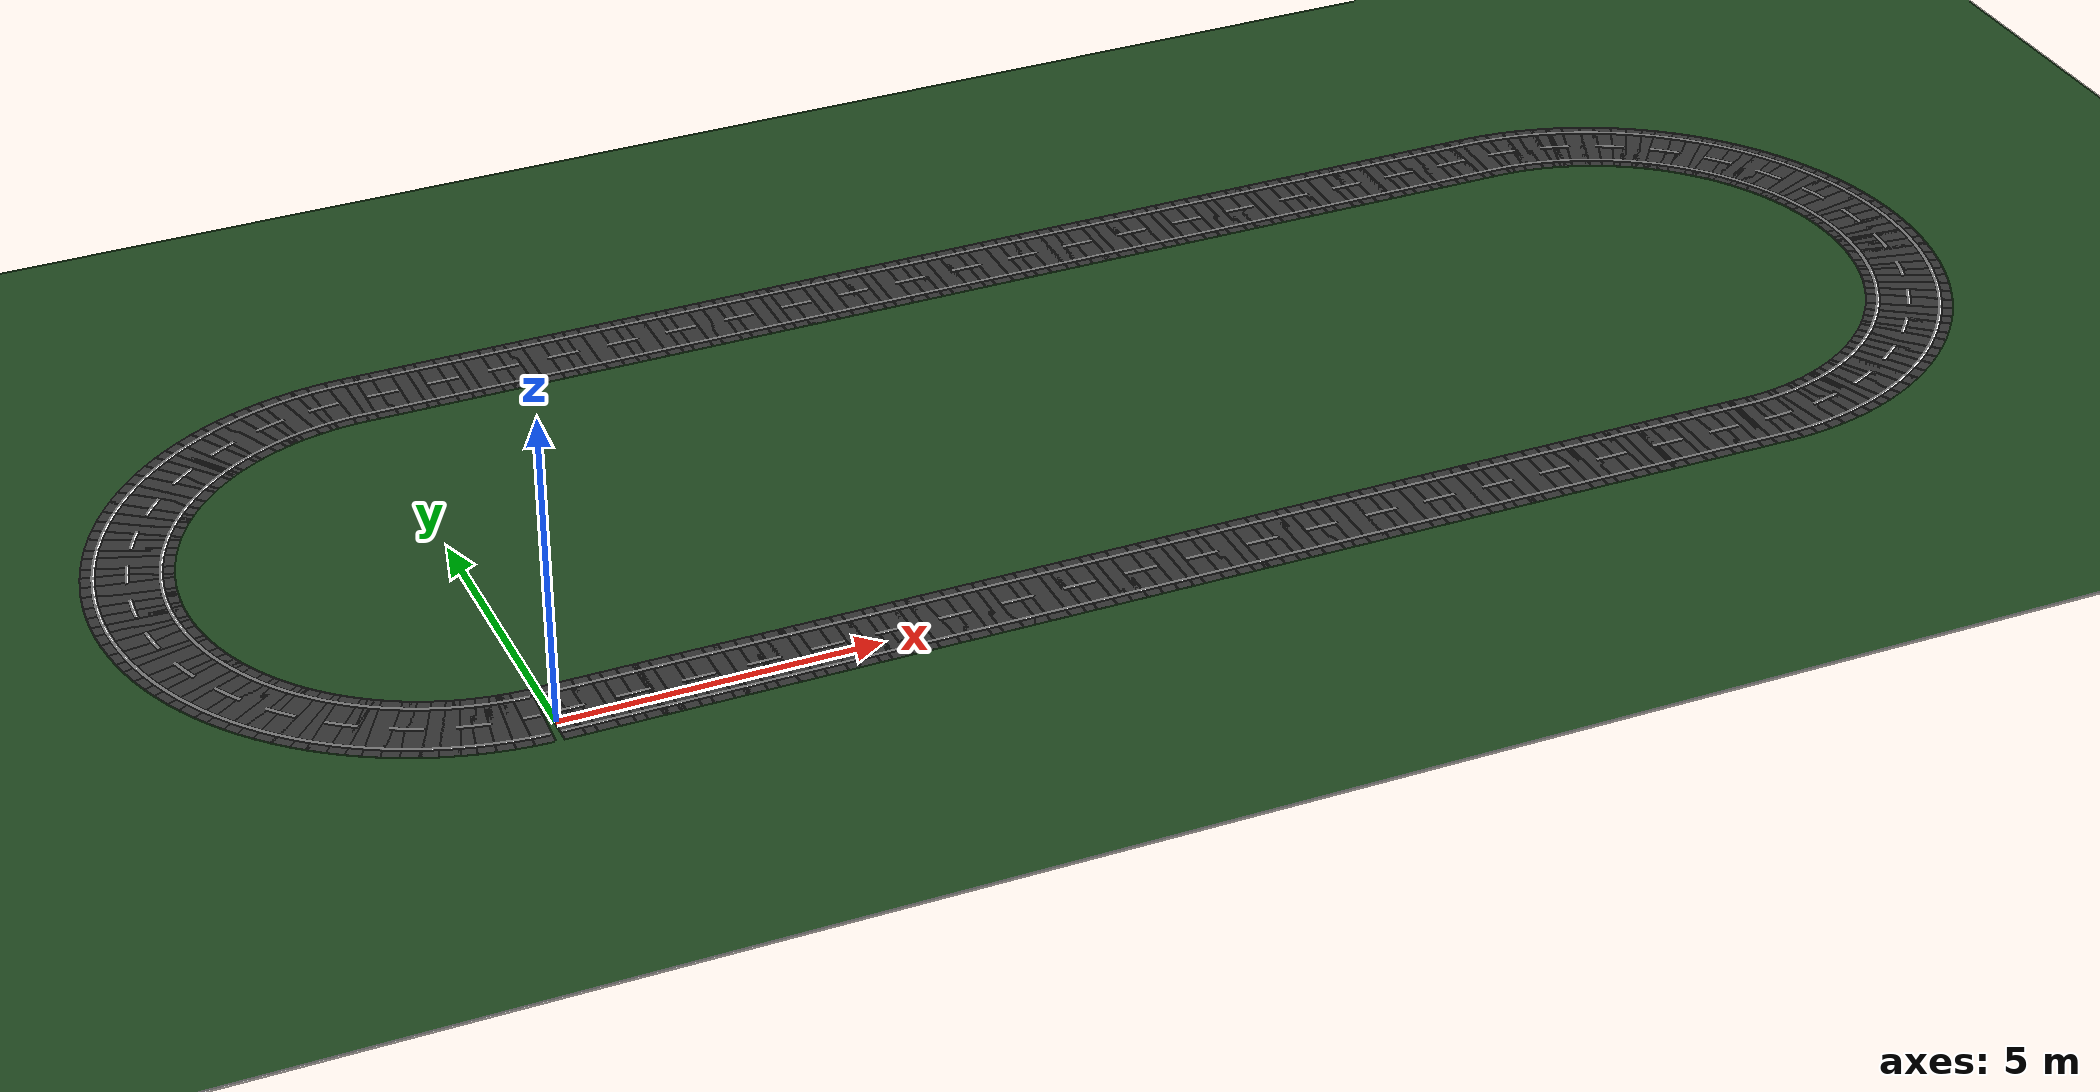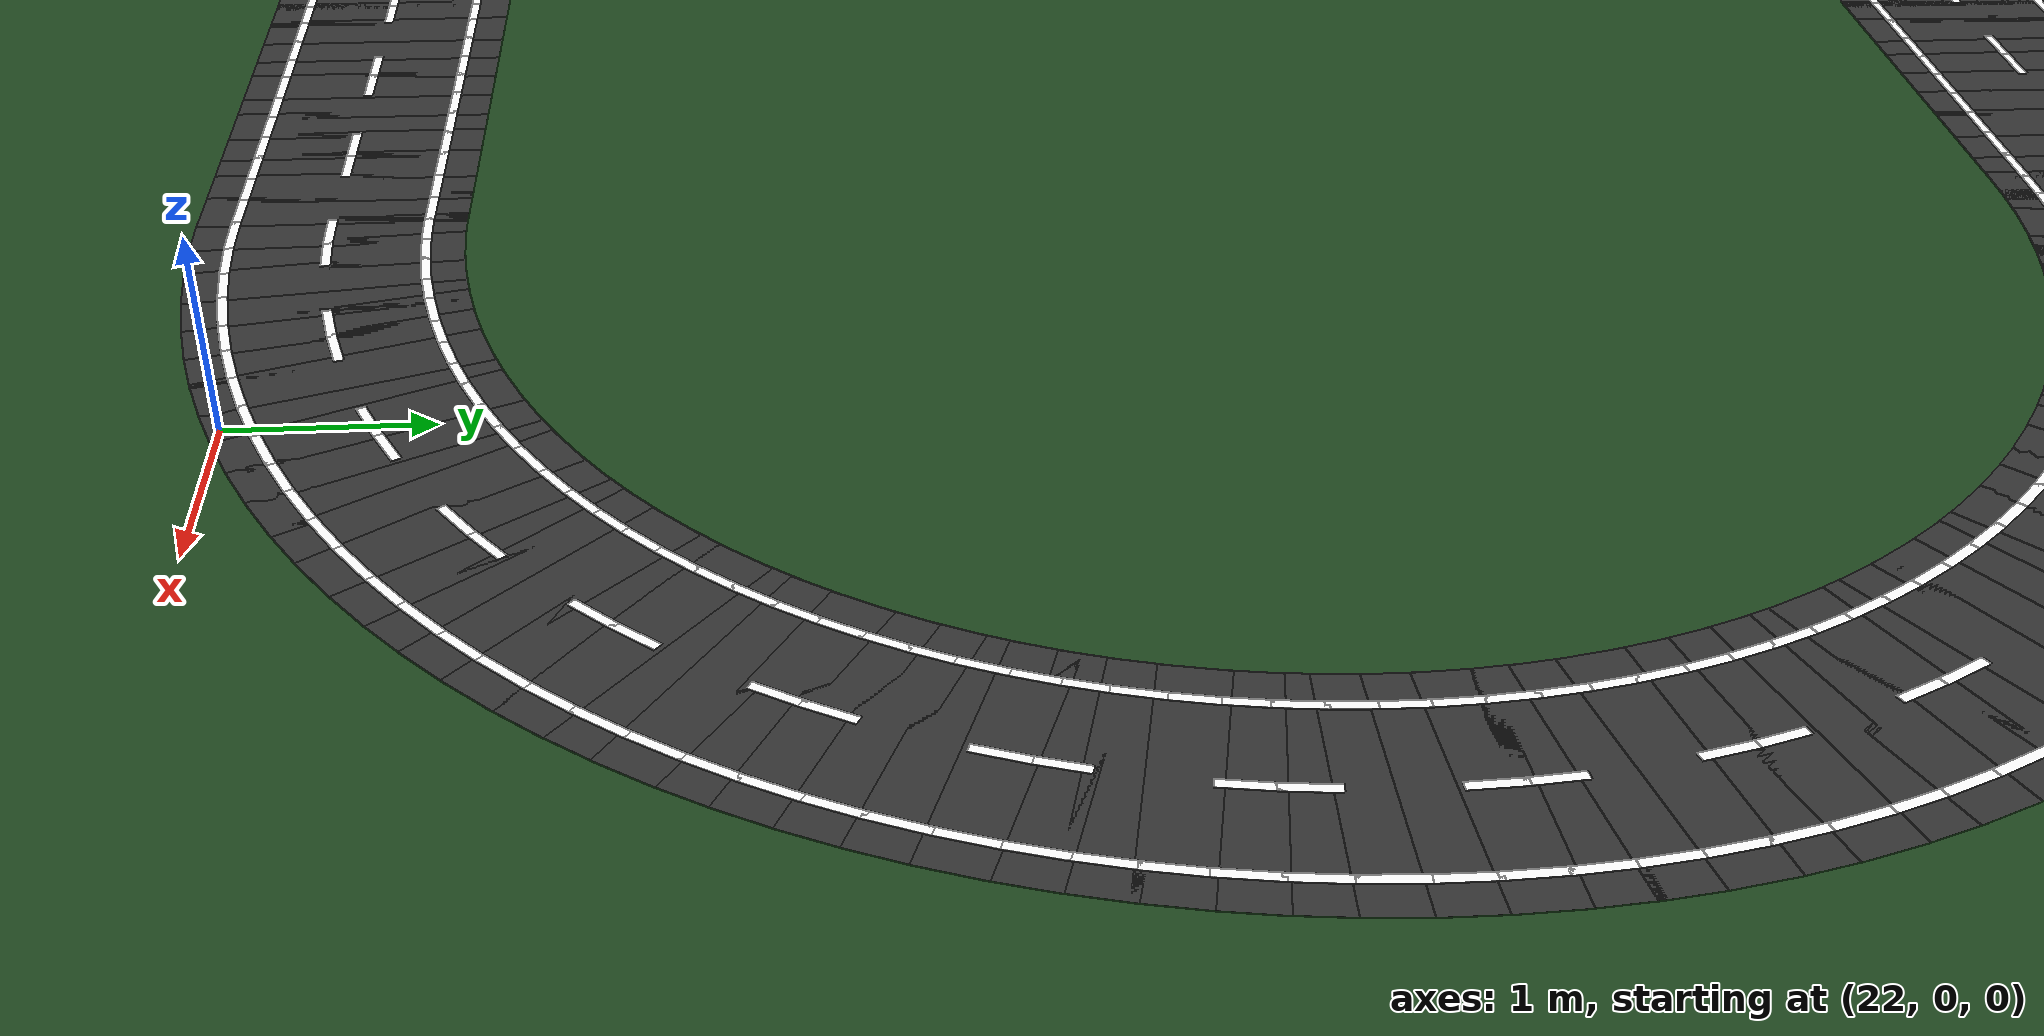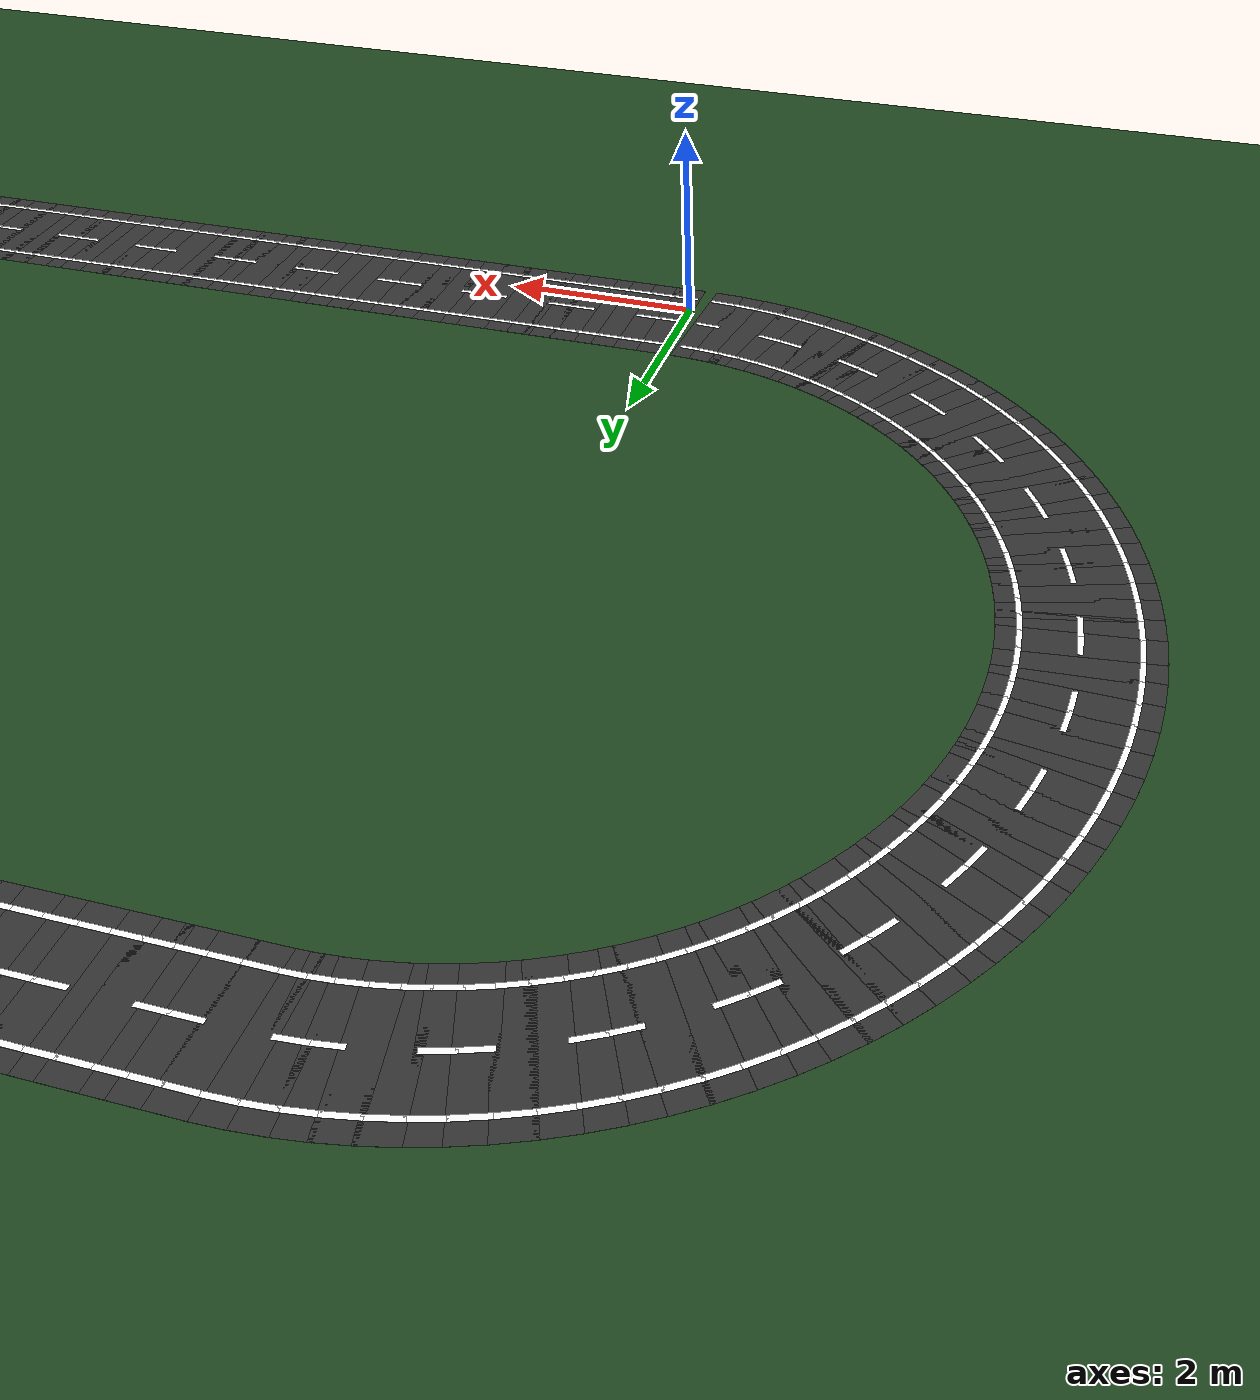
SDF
<?xml version="1.0"?>
<sdf version="1.6">
  <world name="track_oval">
    <physics name="default_physics" default="true" type="ode">
      <max_step_size>0.001</max_step_size>
      <real_time_factor>1.0</real_time_factor>
    </physics>
    <plugin name="gazebo_ros_state" filename="libgazebo_ros_state.so">
      <ros><namespace>/gazebo</namespace></ros>
      <update_rate>1.0</update_rate>
    </plugin>
    <include><uri>model://sun</uri></include>
    <include><uri>model://ground_plane</uri></include>
    <model name="track"><static>true</static><link name="surface">
        <visual name="grass"><pose>10.000 5.000 0.001 0 0 0.0000</pose><geometry><box><size>80.000 60.000 0.001</size></box></geometry><material><ambient>0.12 0.28 0.12 1</ambient><diffuse>0.12 0.28 0.12 1</diffuse></material></visual>
        <visual name="road_0"><pose>0.125 0.250 0.002 0 0 0.0000</pose><geometry><box><size>0.320 1.400 0.001</size></box></geometry><material><ambient>0.2 0.2 0.2 1</ambient><diffuse>0.2 0.2 0.2 1</diffuse></material></visual>
        <visual name="road_1"><pose>0.375 0.250 0.002 0 0 0.0000</pose><geometry><box><size>0.320 1.400 0.001</size></box></geometry><material><ambient>0.2 0.2 0.2 1</ambient><diffuse>0.2 0.2 0.2 1</diffuse></material></visual>
        <visual name="road_2"><pose>0.625 0.250 0.002 0 0 0.0000</pose><geometry><box><size>0.320 1.400 0.001</size></box></geometry><material><ambient>0.2 0.2 0.2 1</ambient><diffuse>0.2 0.2 0.2 1</diffuse></material></visual>
        <visual name="road_3"><pose>0.875 0.250 0.002 0 0 0.0000</pose><geometry><box><size>0.320 1.400 0.001</size></box></geometry><material><ambient>0.2 0.2 0.2 1</ambient><diffuse>0.2 0.2 0.2 1</diffuse></material></visual>
        <visual name="road_4"><pose>1.125 0.250 0.002 0 0 0.0000</pose><geometry><box><size>0.320 1.400 0.001</size></box></geometry><material><ambient>0.2 0.2 0.2 1</ambient><diffuse>0.2 0.2 0.2 1</diffuse></material></visual>
        <visual name="road_5"><pose>1.375 0.250 0.002 0 0 0.0000</pose><geometry><box><size>0.320 1.400 0.001</size></box></geometry><material><ambient>0.2 0.2 0.2 1</ambient><diffuse>0.2 0.2 0.2 1</diffuse></material></visual>
        <visual name="road_6"><pose>1.625 0.250 0.002 0 0 0.0000</pose><geometry><box><size>0.320 1.400 0.001</size></box></geometry><material><ambient>0.2 0.2 0.2 1</ambient><diffuse>0.2 0.2 0.2 1</diffuse></material></visual>
        <visual name="road_7"><pose>1.875 0.250 0.002 0 0 0.0000</pose><geometry><box><size>0.320 1.400 0.001</size></box></geometry><material><ambient>0.2 0.2 0.2 1</ambient><diffuse>0.2 0.2 0.2 1</diffuse></material></visual>
        <visual name="road_8"><pose>2.125 0.250 0.002 0 0 0.0000</pose><geometry><box><size>0.320 1.400 0.001</size></box></geometry><material><ambient>0.2 0.2 0.2 1</ambient><diffuse>0.2 0.2 0.2 1</diffuse></material></visual>
        <visual name="road_9"><pose>2.375 0.250 0.002 0 0 0.0000</pose><geometry><box><size>0.320 1.400 0.001</size></box></geometry><material><ambient>0.2 0.2 0.2 1</ambient><diffuse>0.2 0.2 0.2 1</diffuse></material></visual>
        <visual name="road_10"><pose>2.625 0.250 0.002 0 0 0.0000</pose><geometry><box><size>0.320 1.400 0.001</size></box></geometry><material><ambient>0.2 0.2 0.2 1</ambient><diffuse>0.2 0.2 0.2 1</diffuse></material></visual>
        <visual name="road_11"><pose>2.875 0.250 0.002 0 0 0.0000</pose><geometry><box><size>0.320 1.400 0.001</size></box></geometry><material><ambient>0.2 0.2 0.2 1</ambient><diffuse>0.2 0.2 0.2 1</diffuse></material></visual>
        <visual name="road_12"><pose>3.125 0.250 0.002 0 0 0.0000</pose><geometry><box><size>0.320 1.400 0.001</size></box></geometry><material><ambient>0.2 0.2 0.2 1</ambient><diffuse>0.2 0.2 0.2 1</diffuse></material></visual>
        <visual name="road_13"><pose>3.375 0.250 0.002 0 0 0.0000</pose><geometry><box><size>0.320 1.400 0.001</size></box></geometry><material><ambient>0.2 0.2 0.2 1</ambient><diffuse>0.2 0.2 0.2 1</diffuse></material></visual>
        <visual name="road_14"><pose>3.625 0.250 0.002 0 0 0.0000</pose><geometry><box><size>0.320 1.400 0.001</size></box></geometry><material><ambient>0.2 0.2 0.2 1</ambient><diffuse>0.2 0.2 0.2 1</diffuse></material></visual>
        <visual name="road_15"><pose>3.875 0.250 0.002 0 0 0.0000</pose><geometry><box><size>0.320 1.400 0.001</size></box></geometry><material><ambient>0.2 0.2 0.2 1</ambient><diffuse>0.2 0.2 0.2 1</diffuse></material></visual>
        <visual name="road_16"><pose>4.125 0.250 0.002 0 0 0.0000</pose><geometry><box><size>0.320 1.400 0.001</size></box></geometry><material><ambient>0.2 0.2 0.2 1</ambient><diffuse>0.2 0.2 0.2 1</diffuse></material></visual>
        <visual name="road_17"><pose>4.375 0.250 0.002 0 0 0.0000</pose><geometry><box><size>0.320 1.400 0.001</size></box></geometry><material><ambient>0.2 0.2 0.2 1</ambient><diffuse>0.2 0.2 0.2 1</diffuse></material></visual>
        <visual name="road_18"><pose>4.625 0.250 0.002 0 0 0.0000</pose><geometry><box><size>0.320 1.400 0.001</size></box></geometry><material><ambient>0.2 0.2 0.2 1</ambient><diffuse>0.2 0.2 0.2 1</diffuse></material></visual>
        <visual name="road_19"><pose>4.875 0.250 0.002 0 0 0.0000</pose><geometry><box><size>0.320 1.400 0.001</size></box></geometry><material><ambient>0.2 0.2 0.2 1</ambient><diffuse>0.2 0.2 0.2 1</diffuse></material></visual>
        <visual name="road_20"><pose>5.125 0.250 0.002 0 0 0.0000</pose><geometry><box><size>0.320 1.400 0.001</size></box></geometry><material><ambient>0.2 0.2 0.2 1</ambient><diffuse>0.2 0.2 0.2 1</diffuse></material></visual>
        <visual name="road_21"><pose>5.375 0.250 0.002 0 0 0.0000</pose><geometry><box><size>0.320 1.400 0.001</size></box></geometry><material><ambient>0.2 0.2 0.2 1</ambient><diffuse>0.2 0.2 0.2 1</diffuse></material></visual>
        <visual name="road_22"><pose>5.625 0.250 0.002 0 0 0.0000</pose><geometry><box><size>0.320 1.400 0.001</size></box></geometry><material><ambient>0.2 0.2 0.2 1</ambient><diffuse>0.2 0.2 0.2 1</diffuse></material></visual>
        <visual name="road_23"><pose>5.875 0.250 0.002 0 0 0.0000</pose><geometry><box><size>0.320 1.400 0.001</size></box></geometry><material><ambient>0.2 0.2 0.2 1</ambient><diffuse>0.2 0.2 0.2 1</diffuse></material></visual>
        <visual name="road_24"><pose>6.125 0.250 0.002 0 0 0.0000</pose><geometry><box><size>0.320 1.400 0.001</size></box></geometry><material><ambient>0.2 0.2 0.2 1</ambient><diffuse>0.2 0.2 0.2 1</diffuse></material></visual>
        <visual name="road_25"><pose>6.375 0.250 0.002 0 0 0.0000</pose><geometry><box><size>0.320 1.400 0.001</size></box></geometry><material><ambient>0.2 0.2 0.2 1</ambient><diffuse>0.2 0.2 0.2 1</diffuse></material></visual>
        <visual name="road_26"><pose>6.625 0.250 0.002 0 0 0.0000</pose><geometry><box><size>0.320 1.400 0.001</size></box></geometry><material><ambient>0.2 0.2 0.2 1</ambient><diffuse>0.2 0.2 0.2 1</diffuse></material></visual>
        <visual name="road_27"><pose>6.875 0.250 0.002 0 0 0.0000</pose><geometry><box><size>0.320 1.400 0.001</size></box></geometry><material><ambient>0.2 0.2 0.2 1</ambient><diffuse>0.2 0.2 0.2 1</diffuse></material></visual>
        <visual name="road_28"><pose>7.125 0.250 0.002 0 0 0.0000</pose><geometry><box><size>0.320 1.400 0.001</size></box></geometry><material><ambient>0.2 0.2 0.2 1</ambient><diffuse>0.2 0.2 0.2 1</diffuse></material></visual>
        <visual name="road_29"><pose>7.375 0.250 0.002 0 0 0.0000</pose><geometry><box><size>0.320 1.400 0.001</size></box></geometry><material><ambient>0.2 0.2 0.2 1</ambient><diffuse>0.2 0.2 0.2 1</diffuse></material></visual>
        <visual name="road_30"><pose>7.625 0.250 0.002 0 0 0.0000</pose><geometry><box><size>0.320 1.400 0.001</size></box></geometry><material><ambient>0.2 0.2 0.2 1</ambient><diffuse>0.2 0.2 0.2 1</diffuse></material></visual>
        <visual name="road_31"><pose>7.875 0.250 0.002 0 0 0.0000</pose><geometry><box><size>0.320 1.400 0.001</size></box></geometry><material><ambient>0.2 0.2 0.2 1</ambient><diffuse>0.2 0.2 0.2 1</diffuse></material></visual>
        <visual name="road_32"><pose>8.125 0.250 0.002 0 0 0.0000</pose><geometry><box><size>0.320 1.400 0.001</size></box></geometry><material><ambient>0.2 0.2 0.2 1</ambient><diffuse>0.2 0.2 0.2 1</diffuse></material></visual>
        <visual name="road_33"><pose>8.375 0.250 0.002 0 0 0.0000</pose><geometry><box><size>0.320 1.400 0.001</size></box></geometry><material><ambient>0.2 0.2 0.2 1</ambient><diffuse>0.2 0.2 0.2 1</diffuse></material></visual>
        <visual name="road_34"><pose>8.625 0.250 0.002 0 0 0.0000</pose><geometry><box><size>0.320 1.400 0.001</size></box></geometry><material><ambient>0.2 0.2 0.2 1</ambient><diffuse>0.2 0.2 0.2 1</diffuse></material></visual>
        <visual name="road_35"><pose>8.875 0.250 0.002 0 0 0.0000</pose><geometry><box><size>0.320 1.400 0.001</size></box></geometry><material><ambient>0.2 0.2 0.2 1</ambient><diffuse>0.2 0.2 0.2 1</diffuse></material></visual>
        <visual name="road_36"><pose>9.125 0.250 0.002 0 0 0.0000</pose><geometry><box><size>0.320 1.400 0.001</size></box></geometry><material><ambient>0.2 0.2 0.2 1</ambient><diffuse>0.2 0.2 0.2 1</diffuse></material></visual>
        <visual name="road_37"><pose>9.375 0.250 0.002 0 0 0.0000</pose><geometry><box><size>0.320 1.400 0.001</size></box></geometry><material><ambient>0.2 0.2 0.2 1</ambient><diffuse>0.2 0.2 0.2 1</diffuse></material></visual>
        <visual name="road_38"><pose>9.625 0.250 0.002 0 0 0.0000</pose><geometry><box><size>0.320 1.400 0.001</size></box></geometry><material><ambient>0.2 0.2 0.2 1</ambient><diffuse>0.2 0.2 0.2 1</diffuse></material></visual>
        <visual name="road_39"><pose>9.875 0.250 0.002 0 0 0.0000</pose><geometry><box><size>0.320 1.400 0.001</size></box></geometry><material><ambient>0.2 0.2 0.2 1</ambient><diffuse>0.2 0.2 0.2 1</diffuse></material></visual>
        <visual name="road_40"><pose>10.125 0.250 0.002 0 0 0.0000</pose><geometry><box><size>0.320 1.400 0.001</size></box></geometry><material><ambient>0.2 0.2 0.2 1</ambient><diffuse>0.2 0.2 0.2 1</diffuse></material></visual>
        <visual name="road_41"><pose>10.375 0.250 0.002 0 0 0.0000</pose><geometry><box><size>0.320 1.400 0.001</size></box></geometry><material><ambient>0.2 0.2 0.2 1</ambient><diffuse>0.2 0.2 0.2 1</diffuse></material></visual>
        <visual name="road_42"><pose>10.625 0.250 0.002 0 0 0.0000</pose><geometry><box><size>0.320 1.400 0.001</size></box></geometry><material><ambient>0.2 0.2 0.2 1</ambient><diffuse>0.2 0.2 0.2 1</diffuse></material></visual>
        <visual name="road_43"><pose>10.875 0.250 0.002 0 0 0.0000</pose><geometry><box><size>0.320 1.400 0.001</size></box></geometry><material><ambient>0.2 0.2 0.2 1</ambient><diffuse>0.2 0.2 0.2 1</diffuse></material></visual>
        <visual name="road_44"><pose>11.125 0.250 0.002 0 0 0.0000</pose><geometry><box><size>0.320 1.400 0.001</size></box></geometry><material><ambient>0.2 0.2 0.2 1</ambient><diffuse>0.2 0.2 0.2 1</diffuse></material></visual>
        <visual name="road_45"><pose>11.375 0.250 0.002 0 0 0.0000</pose><geometry><box><size>0.320 1.400 0.001</size></box></geometry><material><ambient>0.2 0.2 0.2 1</ambient><diffuse>0.2 0.2 0.2 1</diffuse></material></visual>
        <visual name="road_46"><pose>11.625 0.250 0.002 0 0 0.0000</pose><geometry><box><size>0.320 1.400 0.001</size></box></geometry><material><ambient>0.2 0.2 0.2 1</ambient><diffuse>0.2 0.2 0.2 1</diffuse></material></visual>
        <visual name="road_47"><pose>11.875 0.250 0.002 0 0 0.0000</pose><geometry><box><size>0.320 1.400 0.001</size></box></geometry><material><ambient>0.2 0.2 0.2 1</ambient><diffuse>0.2 0.2 0.2 1</diffuse></material></visual>
        <visual name="road_48"><pose>12.125 0.250 0.002 0 0 0.0000</pose><geometry><box><size>0.320 1.400 0.001</size></box></geometry><material><ambient>0.2 0.2 0.2 1</ambient><diffuse>0.2 0.2 0.2 1</diffuse></material></visual>
        <visual name="road_49"><pose>12.375 0.250 0.002 0 0 0.0000</pose><geometry><box><size>0.320 1.400 0.001</size></box></geometry><material><ambient>0.2 0.2 0.2 1</ambient><diffuse>0.2 0.2 0.2 1</diffuse></material></visual>
        <visual name="road_50"><pose>12.625 0.250 0.002 0 0 0.0000</pose><geometry><box><size>0.320 1.400 0.001</size></box></geometry><material><ambient>0.2 0.2 0.2 1</ambient><diffuse>0.2 0.2 0.2 1</diffuse></material></visual>
        <visual name="road_51"><pose>12.875 0.250 0.002 0 0 0.0000</pose><geometry><box><size>0.320 1.400 0.001</size></box></geometry><material><ambient>0.2 0.2 0.2 1</ambient><diffuse>0.2 0.2 0.2 1</diffuse></material></visual>
        <visual name="road_52"><pose>13.125 0.250 0.002 0 0 0.0000</pose><geometry><box><size>0.320 1.400 0.001</size></box></geometry><material><ambient>0.2 0.2 0.2 1</ambient><diffuse>0.2 0.2 0.2 1</diffuse></material></visual>
        <visual name="road_53"><pose>13.375 0.250 0.002 0 0 0.0000</pose><geometry><box><size>0.320 1.400 0.001</size></box></geometry><material><ambient>0.2 0.2 0.2 1</ambient><diffuse>0.2 0.2 0.2 1</diffuse></material></visual>
        <visual name="road_54"><pose>13.625 0.250 0.002 0 0 0.0000</pose><geometry><box><size>0.320 1.400 0.001</size></box></geometry><material><ambient>0.2 0.2 0.2 1</ambient><diffuse>0.2 0.2 0.2 1</diffuse></material></visual>
        <visual name="road_55"><pose>13.875 0.250 0.002 0 0 0.0000</pose><geometry><box><size>0.320 1.400 0.001</size></box></geometry><material><ambient>0.2 0.2 0.2 1</ambient><diffuse>0.2 0.2 0.2 1</diffuse></material></visual>
        <visual name="road_56"><pose>14.125 0.250 0.002 0 0 0.0000</pose><geometry><box><size>0.320 1.400 0.001</size></box></geometry><material><ambient>0.2 0.2 0.2 1</ambient><diffuse>0.2 0.2 0.2 1</diffuse></material></visual>
        <visual name="road_57"><pose>14.375 0.250 0.002 0 0 0.0000</pose><geometry><box><size>0.320 1.400 0.001</size></box></geometry><material><ambient>0.2 0.2 0.2 1</ambient><diffuse>0.2 0.2 0.2 1</diffuse></material></visual>
        <visual name="road_58"><pose>14.625 0.250 0.002 0 0 0.0000</pose><geometry><box><size>0.320 1.400 0.001</size></box></geometry><material><ambient>0.2 0.2 0.2 1</ambient><diffuse>0.2 0.2 0.2 1</diffuse></material></visual>
        <visual name="road_59"><pose>14.875 0.250 0.002 0 0 0.0000</pose><geometry><box><size>0.320 1.400 0.001</size></box></geometry><material><ambient>0.2 0.2 0.2 1</ambient><diffuse>0.2 0.2 0.2 1</diffuse></material></visual>
        <visual name="road_60"><pose>15.125 0.250 0.002 0 0 0.0000</pose><geometry><box><size>0.320 1.400 0.001</size></box></geometry><material><ambient>0.2 0.2 0.2 1</ambient><diffuse>0.2 0.2 0.2 1</diffuse></material></visual>
        <visual name="road_61"><pose>15.375 0.250 0.002 0 0 0.0000</pose><geometry><box><size>0.320 1.400 0.001</size></box></geometry><material><ambient>0.2 0.2 0.2 1</ambient><diffuse>0.2 0.2 0.2 1</diffuse></material></visual>
        <visual name="road_62"><pose>15.625 0.250 0.002 0 0 0.0000</pose><geometry><box><size>0.320 1.400 0.001</size></box></geometry><material><ambient>0.2 0.2 0.2 1</ambient><diffuse>0.2 0.2 0.2 1</diffuse></material></visual>
        <visual name="road_63"><pose>15.875 0.250 0.002 0 0 0.0000</pose><geometry><box><size>0.320 1.400 0.001</size></box></geometry><material><ambient>0.2 0.2 0.2 1</ambient><diffuse>0.2 0.2 0.2 1</diffuse></material></visual>
        <visual name="road_64"><pose>16.125 0.250 0.002 0 0 0.0000</pose><geometry><box><size>0.320 1.400 0.001</size></box></geometry><material><ambient>0.2 0.2 0.2 1</ambient><diffuse>0.2 0.2 0.2 1</diffuse></material></visual>
        <visual name="road_65"><pose>16.375 0.250 0.002 0 0 0.0000</pose><geometry><box><size>0.320 1.400 0.001</size></box></geometry><material><ambient>0.2 0.2 0.2 1</ambient><diffuse>0.2 0.2 0.2 1</diffuse></material></visual>
        <visual name="road_66"><pose>16.625 0.250 0.002 0 0 0.0000</pose><geometry><box><size>0.320 1.400 0.001</size></box></geometry><material><ambient>0.2 0.2 0.2 1</ambient><diffuse>0.2 0.2 0.2 1</diffuse></material></visual>
        <visual name="road_67"><pose>16.875 0.250 0.002 0 0 0.0000</pose><geometry><box><size>0.320 1.400 0.001</size></box></geometry><material><ambient>0.2 0.2 0.2 1</ambient><diffuse>0.2 0.2 0.2 1</diffuse></material></visual>
        <visual name="road_68"><pose>17.125 0.250 0.002 0 0 0.0000</pose><geometry><box><size>0.320 1.400 0.001</size></box></geometry><material><ambient>0.2 0.2 0.2 1</ambient><diffuse>0.2 0.2 0.2 1</diffuse></material></visual>
        <visual name="road_69"><pose>17.375 0.250 0.002 0 0 0.0000</pose><geometry><box><size>0.320 1.400 0.001</size></box></geometry><material><ambient>0.2 0.2 0.2 1</ambient><diffuse>0.2 0.2 0.2 1</diffuse></material></visual>
        <visual name="road_70"><pose>17.625 0.250 0.002 0 0 0.0000</pose><geometry><box><size>0.320 1.400 0.001</size></box></geometry><material><ambient>0.2 0.2 0.2 1</ambient><diffuse>0.2 0.2 0.2 1</diffuse></material></visual>
        <visual name="road_71"><pose>17.875 0.250 0.002 0 0 0.0000</pose><geometry><box><size>0.320 1.400 0.001</size></box></geometry><material><ambient>0.2 0.2 0.2 1</ambient><diffuse>0.2 0.2 0.2 1</diffuse></material></visual>
        <visual name="road_72"><pose>18.125 0.250 0.002 0 0 0.0000</pose><geometry><box><size>0.320 1.400 0.001</size></box></geometry><material><ambient>0.2 0.2 0.2 1</ambient><diffuse>0.2 0.2 0.2 1</diffuse></material></visual>
        <visual name="road_73"><pose>18.375 0.250 0.002 0 0 0.0000</pose><geometry><box><size>0.320 1.400 0.001</size></box></geometry><material><ambient>0.2 0.2 0.2 1</ambient><diffuse>0.2 0.2 0.2 1</diffuse></material></visual>
        <visual name="road_74"><pose>18.625 0.250 0.002 0 0 0.0000</pose><geometry><box><size>0.320 1.400 0.001</size></box></geometry><material><ambient>0.2 0.2 0.2 1</ambient><diffuse>0.2 0.2 0.2 1</diffuse></material></visual>
        <visual name="road_75"><pose>18.875 0.250 0.002 0 0 0.0000</pose><geometry><box><size>0.320 1.400 0.001</size></box></geometry><material><ambient>0.2 0.2 0.2 1</ambient><diffuse>0.2 0.2 0.2 1</diffuse></material></visual>
        <visual name="road_76"><pose>19.125 0.250 0.002 0 0 0.0000</pose><geometry><box><size>0.320 1.400 0.001</size></box></geometry><material><ambient>0.2 0.2 0.2 1</ambient><diffuse>0.2 0.2 0.2 1</diffuse></material></visual>
        <visual name="road_77"><pose>19.375 0.250 0.002 0 0 0.0000</pose><geometry><box><size>0.320 1.400 0.001</size></box></geometry><material><ambient>0.2 0.2 0.2 1</ambient><diffuse>0.2 0.2 0.2 1</diffuse></material></visual>
        <visual name="road_78"><pose>19.625 0.250 0.002 0 0 0.0000</pose><geometry><box><size>0.320 1.400 0.001</size></box></geometry><material><ambient>0.2 0.2 0.2 1</ambient><diffuse>0.2 0.2 0.2 1</diffuse></material></visual>
        <visual name="road_79"><pose>19.875 0.250 0.002 0 0 0.0000</pose><geometry><box><size>0.320 1.400 0.001</size></box></geometry><material><ambient>0.2 0.2 0.2 1</ambient><diffuse>0.2 0.2 0.2 1</diffuse></material></visual>
        <visual name="road_80"><pose>20.119 0.251 0.002 0 0 0.0250</pose><geometry><box><size>0.307 1.400 0.001</size></box></geometry><material><ambient>0.2 0.2 0.2 1</ambient><diffuse>0.2 0.2 0.2 1</diffuse></material></visual>
        <visual name="road_81"><pose>20.356 0.263 0.002 0 0 0.0750</pose><geometry><box><size>0.307 1.400 0.001</size></box></geometry><material><ambient>0.2 0.2 0.2 1</ambient><diffuse>0.2 0.2 0.2 1</diffuse></material></visual>
        <visual name="road_82"><pose>20.592 0.287 0.002 0 0 0.1250</pose><geometry><box><size>0.307 1.400 0.001</size></box></geometry><material><ambient>0.2 0.2 0.2 1</ambient><diffuse>0.2 0.2 0.2 1</diffuse></material></visual>
        <visual name="road_83"><pose>20.827 0.323 0.002 0 0 0.1750</pose><geometry><box><size>0.307 1.400 0.001</size></box></geometry><material><ambient>0.2 0.2 0.2 1</ambient><diffuse>0.2 0.2 0.2 1</diffuse></material></visual>
        <visual name="road_84"><pose>21.060 0.370 0.002 0 0 0.2250</pose><geometry><box><size>0.307 1.400 0.001</size></box></geometry><material><ambient>0.2 0.2 0.2 1</ambient><diffuse>0.2 0.2 0.2 1</diffuse></material></visual>
        <visual name="road_85"><pose>21.290 0.428 0.002 0 0 0.2750</pose><geometry><box><size>0.307 1.400 0.001</size></box></geometry><material><ambient>0.2 0.2 0.2 1</ambient><diffuse>0.2 0.2 0.2 1</diffuse></material></visual>
        <visual name="road_86"><pose>21.517 0.499 0.002 0 0 0.3250</pose><geometry><box><size>0.307 1.400 0.001</size></box></geometry><material><ambient>0.2 0.2 0.2 1</ambient><diffuse>0.2 0.2 0.2 1</diffuse></material></visual>
        <visual name="road_87"><pose>21.740 0.580 0.002 0 0 0.3750</pose><geometry><box><size>0.307 1.400 0.001</size></box></geometry><material><ambient>0.2 0.2 0.2 1</ambient><diffuse>0.2 0.2 0.2 1</diffuse></material></visual>
        <visual name="road_88"><pose>21.959 0.673 0.002 0 0 0.4250</pose><geometry><box><size>0.307 1.400 0.001</size></box></geometry><material><ambient>0.2 0.2 0.2 1</ambient><diffuse>0.2 0.2 0.2 1</diffuse></material></visual>
        <visual name="road_89"><pose>22.172 0.776 0.002 0 0 0.4750</pose><geometry><box><size>0.307 1.400 0.001</size></box></geometry><material><ambient>0.2 0.2 0.2 1</ambient><diffuse>0.2 0.2 0.2 1</diffuse></material></visual>
        <visual name="road_90"><pose>22.381 0.890 0.002 0 0 0.5250</pose><geometry><box><size>0.307 1.400 0.001</size></box></geometry><material><ambient>0.2 0.2 0.2 1</ambient><diffuse>0.2 0.2 0.2 1</diffuse></material></visual>
        <visual name="road_91"><pose>22.583 1.014 0.002 0 0 0.5750</pose><geometry><box><size>0.307 1.400 0.001</size></box></geometry><material><ambient>0.2 0.2 0.2 1</ambient><diffuse>0.2 0.2 0.2 1</diffuse></material></visual>
        <visual name="road_92"><pose>22.779 1.148 0.002 0 0 0.6250</pose><geometry><box><size>0.307 1.400 0.001</size></box></geometry><material><ambient>0.2 0.2 0.2 1</ambient><diffuse>0.2 0.2 0.2 1</diffuse></material></visual>
        <visual name="road_93"><pose>22.968 1.292 0.002 0 0 0.6750</pose><geometry><box><size>0.307 1.400 0.001</size></box></geometry><material><ambient>0.2 0.2 0.2 1</ambient><diffuse>0.2 0.2 0.2 1</diffuse></material></visual>
        <visual name="road_94"><pose>23.150 1.445 0.002 0 0 0.7250</pose><geometry><box><size>0.307 1.400 0.001</size></box></geometry><material><ambient>0.2 0.2 0.2 1</ambient><diffuse>0.2 0.2 0.2 1</diffuse></material></visual>
        <visual name="road_95"><pose>23.324 1.607 0.002 0 0 0.7750</pose><geometry><box><size>0.307 1.400 0.001</size></box></geometry><material><ambient>0.2 0.2 0.2 1</ambient><diffuse>0.2 0.2 0.2 1</diffuse></material></visual>
        <visual name="road_96"><pose>23.489 1.777 0.002 0 0 0.8250</pose><geometry><box><size>0.307 1.400 0.001</size></box></geometry><material><ambient>0.2 0.2 0.2 1</ambient><diffuse>0.2 0.2 0.2 1</diffuse></material></visual>
        <visual name="road_97"><pose>23.646 1.955 0.002 0 0 0.8750</pose><geometry><box><size>0.307 1.400 0.001</size></box></geometry><material><ambient>0.2 0.2 0.2 1</ambient><diffuse>0.2 0.2 0.2 1</diffuse></material></visual>
        <visual name="road_98"><pose>23.793 2.141 0.002 0 0 0.9250</pose><geometry><box><size>0.307 1.400 0.001</size></box></geometry><material><ambient>0.2 0.2 0.2 1</ambient><diffuse>0.2 0.2 0.2 1</diffuse></material></visual>
        <visual name="road_99"><pose>23.932 2.334 0.002 0 0 0.9750</pose><geometry><box><size>0.307 1.400 0.001</size></box></geometry><material><ambient>0.2 0.2 0.2 1</ambient><diffuse>0.2 0.2 0.2 1</diffuse></material></visual>
        <visual name="road_100"><pose>24.060 2.534 0.002 0 0 1.0250</pose><geometry><box><size>0.307 1.400 0.001</size></box></geometry><material><ambient>0.2 0.2 0.2 1</ambient><diffuse>0.2 0.2 0.2 1</diffuse></material></visual>
        <visual name="road_101"><pose>24.178 2.740 0.002 0 0 1.0750</pose><geometry><box><size>0.307 1.400 0.001</size></box></geometry><material><ambient>0.2 0.2 0.2 1</ambient><diffuse>0.2 0.2 0.2 1</diffuse></material></visual>
        <visual name="road_102"><pose>24.286 2.952 0.002 0 0 1.1250</pose><geometry><box><size>0.307 1.400 0.001</size></box></geometry><material><ambient>0.2 0.2 0.2 1</ambient><diffuse>0.2 0.2 0.2 1</diffuse></material></visual>
        <visual name="road_103"><pose>24.383 3.169 0.002 0 0 1.1750</pose><geometry><box><size>0.307 1.400 0.001</size></box></geometry><material><ambient>0.2 0.2 0.2 1</ambient><diffuse>0.2 0.2 0.2 1</diffuse></material></visual>
        <visual name="road_104"><pose>24.469 3.390 0.002 0 0 1.2250</pose><geometry><box><size>0.307 1.400 0.001</size></box></geometry><material><ambient>0.2 0.2 0.2 1</ambient><diffuse>0.2 0.2 0.2 1</diffuse></material></visual>
        <visual name="road_105"><pose>24.544 3.615 0.002 0 0 1.2750</pose><geometry><box><size>0.307 1.400 0.001</size></box></geometry><material><ambient>0.2 0.2 0.2 1</ambient><diffuse>0.2 0.2 0.2 1</diffuse></material></visual>
        <visual name="road_106"><pose>24.607 3.844 0.002 0 0 1.3250</pose><geometry><box><size>0.307 1.400 0.001</size></box></geometry><material><ambient>0.2 0.2 0.2 1</ambient><diffuse>0.2 0.2 0.2 1</diffuse></material></visual>
        <visual name="road_107"><pose>24.659 4.076 0.002 0 0 1.3750</pose><geometry><box><size>0.307 1.400 0.001</size></box></geometry><material><ambient>0.2 0.2 0.2 1</ambient><diffuse>0.2 0.2 0.2 1</diffuse></material></visual>
        <visual name="road_108"><pose>24.700 4.310 0.002 0 0 1.4250</pose><geometry><box><size>0.307 1.400 0.001</size></box></geometry><material><ambient>0.2 0.2 0.2 1</ambient><diffuse>0.2 0.2 0.2 1</diffuse></material></visual>
        <visual name="road_109"><pose>24.728 4.546 0.002 0 0 1.4750</pose><geometry><box><size>0.307 1.400 0.001</size></box></geometry><material><ambient>0.2 0.2 0.2 1</ambient><diffuse>0.2 0.2 0.2 1</diffuse></material></visual>
        <visual name="road_110"><pose>24.745 4.783 0.002 0 0 1.5250</pose><geometry><box><size>0.307 1.400 0.001</size></box></geometry><material><ambient>0.2 0.2 0.2 1</ambient><diffuse>0.2 0.2 0.2 1</diffuse></material></visual>
        <visual name="road_111"><pose>24.750 5.020 0.002 0 0 1.5750</pose><geometry><box><size>0.307 1.400 0.001</size></box></geometry><material><ambient>0.2 0.2 0.2 1</ambient><diffuse>0.2 0.2 0.2 1</diffuse></material></visual>
        <visual name="road_112"><pose>24.743 5.257 0.002 0 0 1.6250</pose><geometry><box><size>0.307 1.400 0.001</size></box></geometry><material><ambient>0.2 0.2 0.2 1</ambient><diffuse>0.2 0.2 0.2 1</diffuse></material></visual>
        <visual name="road_113"><pose>24.724 5.494 0.002 0 0 1.6750</pose><geometry><box><size>0.307 1.400 0.001</size></box></geometry><material><ambient>0.2 0.2 0.2 1</ambient><diffuse>0.2 0.2 0.2 1</diffuse></material></visual>
        <visual name="road_114"><pose>24.694 5.730 0.002 0 0 1.7250</pose><geometry><box><size>0.307 1.400 0.001</size></box></geometry><material><ambient>0.2 0.2 0.2 1</ambient><diffuse>0.2 0.2 0.2 1</diffuse></material></visual>
        <visual name="road_115"><pose>24.651 5.963 0.002 0 0 1.7750</pose><geometry><box><size>0.307 1.400 0.001</size></box></geometry><material><ambient>0.2 0.2 0.2 1</ambient><diffuse>0.2 0.2 0.2 1</diffuse></material></visual>
        <visual name="road_116"><pose>24.597 6.195 0.002 0 0 1.8250</pose><geometry><box><size>0.307 1.400 0.001</size></box></geometry><material><ambient>0.2 0.2 0.2 1</ambient><diffuse>0.2 0.2 0.2 1</diffuse></material></visual>
        <visual name="road_117"><pose>24.532 6.423 0.002 0 0 1.8750</pose><geometry><box><size>0.307 1.400 0.001</size></box></geometry><material><ambient>0.2 0.2 0.2 1</ambient><diffuse>0.2 0.2 0.2 1</diffuse></material></visual>
        <visual name="road_118"><pose>24.455 6.648 0.002 0 0 1.9250</pose><geometry><box><size>0.307 1.400 0.001</size></box></geometry><material><ambient>0.2 0.2 0.2 1</ambient><diffuse>0.2 0.2 0.2 1</diffuse></material></visual>
        <visual name="road_119"><pose>24.367 6.868 0.002 0 0 1.9750</pose><geometry><box><size>0.307 1.400 0.001</size></box></geometry><material><ambient>0.2 0.2 0.2 1</ambient><diffuse>0.2 0.2 0.2 1</diffuse></material></visual>
        <visual name="road_120"><pose>24.268 7.084 0.002 0 0 2.0250</pose><geometry><box><size>0.307 1.400 0.001</size></box></geometry><material><ambient>0.2 0.2 0.2 1</ambient><diffuse>0.2 0.2 0.2 1</diffuse></material></visual>
        <visual name="road_121"><pose>24.159 7.295 0.002 0 0 2.0750</pose><geometry><box><size>0.307 1.400 0.001</size></box></geometry><material><ambient>0.2 0.2 0.2 1</ambient><diffuse>0.2 0.2 0.2 1</diffuse></material></visual>
        <visual name="road_122"><pose>24.039 7.500 0.002 0 0 2.1250</pose><geometry><box><size>0.307 1.400 0.001</size></box></geometry><material><ambient>0.2 0.2 0.2 1</ambient><diffuse>0.2 0.2 0.2 1</diffuse></material></visual>
        <visual name="road_123"><pose>23.909 7.699 0.002 0 0 2.1750</pose><geometry><box><size>0.307 1.400 0.001</size></box></geometry><material><ambient>0.2 0.2 0.2 1</ambient><diffuse>0.2 0.2 0.2 1</diffuse></material></visual>
        <visual name="road_124"><pose>23.769 7.891 0.002 0 0 2.2250</pose><geometry><box><size>0.307 1.400 0.001</size></box></geometry><material><ambient>0.2 0.2 0.2 1</ambient><diffuse>0.2 0.2 0.2 1</diffuse></material></visual>
        <visual name="road_125"><pose>23.620 8.075 0.002 0 0 2.2750</pose><geometry><box><size>0.307 1.400 0.001</size></box></geometry><material><ambient>0.2 0.2 0.2 1</ambient><diffuse>0.2 0.2 0.2 1</diffuse></material></visual>
        <visual name="road_126"><pose>23.462 8.252 0.002 0 0 2.3250</pose><geometry><box><size>0.307 1.400 0.001</size></box></geometry><material><ambient>0.2 0.2 0.2 1</ambient><diffuse>0.2 0.2 0.2 1</diffuse></material></visual>
        <visual name="road_127"><pose>23.295 8.421 0.002 0 0 2.3750</pose><geometry><box><size>0.307 1.400 0.001</size></box></geometry><material><ambient>0.2 0.2 0.2 1</ambient><diffuse>0.2 0.2 0.2 1</diffuse></material></visual>
        <visual name="road_128"><pose>23.120 8.582 0.002 0 0 2.4250</pose><geometry><box><size>0.307 1.400 0.001</size></box></geometry><material><ambient>0.2 0.2 0.2 1</ambient><diffuse>0.2 0.2 0.2 1</diffuse></material></visual>
        <visual name="road_129"><pose>22.937 8.733 0.002 0 0 2.4750</pose><geometry><box><size>0.307 1.400 0.001</size></box></geometry><material><ambient>0.2 0.2 0.2 1</ambient><diffuse>0.2 0.2 0.2 1</diffuse></material></visual>
        <visual name="road_130"><pose>22.747 8.875 0.002 0 0 2.5250</pose><geometry><box><size>0.307 1.400 0.001</size></box></geometry><material><ambient>0.2 0.2 0.2 1</ambient><diffuse>0.2 0.2 0.2 1</diffuse></material></visual>
        <visual name="road_131"><pose>22.550 9.008 0.002 0 0 2.5750</pose><geometry><box><size>0.307 1.400 0.001</size></box></geometry><material><ambient>0.2 0.2 0.2 1</ambient><diffuse>0.2 0.2 0.2 1</diffuse></material></visual>
        <visual name="road_132"><pose>22.346 9.130 0.002 0 0 2.6250</pose><geometry><box><size>0.307 1.400 0.001</size></box></geometry><material><ambient>0.2 0.2 0.2 1</ambient><diffuse>0.2 0.2 0.2 1</diffuse></material></visual>
        <visual name="road_133"><pose>22.137 9.242 0.002 0 0 2.6750</pose><geometry><box><size>0.307 1.400 0.001</size></box></geometry><material><ambient>0.2 0.2 0.2 1</ambient><diffuse>0.2 0.2 0.2 1</diffuse></material></visual>
        <visual name="road_134"><pose>21.922 9.344 0.002 0 0 2.7250</pose><geometry><box><size>0.307 1.400 0.001</size></box></geometry><material><ambient>0.2 0.2 0.2 1</ambient><diffuse>0.2 0.2 0.2 1</diffuse></material></visual>
        <visual name="road_135"><pose>21.703 9.434 0.002 0 0 2.7750</pose><geometry><box><size>0.307 1.400 0.001</size></box></geometry><material><ambient>0.2 0.2 0.2 1</ambient><diffuse>0.2 0.2 0.2 1</diffuse></material></visual>
        <visual name="road_136"><pose>21.479 9.514 0.002 0 0 2.8250</pose><geometry><box><size>0.307 1.400 0.001</size></box></geometry><material><ambient>0.2 0.2 0.2 1</ambient><diffuse>0.2 0.2 0.2 1</diffuse></material></visual>
        <visual name="road_137"><pose>21.251 9.582 0.002 0 0 2.8750</pose><geometry><box><size>0.307 1.400 0.001</size></box></geometry><material><ambient>0.2 0.2 0.2 1</ambient><diffuse>0.2 0.2 0.2 1</diffuse></material></visual>
        <visual name="road_138"><pose>21.021 9.639 0.002 0 0 2.9250</pose><geometry><box><size>0.307 1.400 0.001</size></box></geometry><material><ambient>0.2 0.2 0.2 1</ambient><diffuse>0.2 0.2 0.2 1</diffuse></material></visual>
        <visual name="road_139"><pose>20.788 9.684 0.002 0 0 2.9750</pose><geometry><box><size>0.307 1.400 0.001</size></box></geometry><material><ambient>0.2 0.2 0.2 1</ambient><diffuse>0.2 0.2 0.2 1</diffuse></material></visual>
        <visual name="road_140"><pose>20.553 9.718 0.002 0 0 3.0250</pose><geometry><box><size>0.307 1.400 0.001</size></box></geometry><material><ambient>0.2 0.2 0.2 1</ambient><diffuse>0.2 0.2 0.2 1</diffuse></material></visual>
        <visual name="road_141"><pose>20.316 9.739 0.002 0 0 3.0750</pose><geometry><box><size>0.307 1.400 0.001</size></box></geometry><material><ambient>0.2 0.2 0.2 1</ambient><diffuse>0.2 0.2 0.2 1</diffuse></material></visual>
        <visual name="road_142"><pose>20.079 9.749 0.002 0 0 3.1250</pose><geometry><box><size>0.307 1.400 0.001</size></box></geometry><material><ambient>0.2 0.2 0.2 1</ambient><diffuse>0.2 0.2 0.2 1</diffuse></material></visual>
        <visual name="road_143"><pose>19.833 9.750 0.002 0 0 3.1416</pose><geometry><box><size>0.320 1.400 0.001</size></box></geometry><material><ambient>0.2 0.2 0.2 1</ambient><diffuse>0.2 0.2 0.2 1</diffuse></material></visual>
        <visual name="road_144"><pose>19.583 9.750 0.002 0 0 3.1416</pose><geometry><box><size>0.320 1.400 0.001</size></box></geometry><material><ambient>0.2 0.2 0.2 1</ambient><diffuse>0.2 0.2 0.2 1</diffuse></material></visual>
        <visual name="road_145"><pose>19.333 9.750 0.002 0 0 3.1416</pose><geometry><box><size>0.320 1.400 0.001</size></box></geometry><material><ambient>0.2 0.2 0.2 1</ambient><diffuse>0.2 0.2 0.2 1</diffuse></material></visual>
        <visual name="road_146"><pose>19.083 9.750 0.002 0 0 3.1416</pose><geometry><box><size>0.320 1.400 0.001</size></box></geometry><material><ambient>0.2 0.2 0.2 1</ambient><diffuse>0.2 0.2 0.2 1</diffuse></material></visual>
        <visual name="road_147"><pose>18.833 9.750 0.002 0 0 3.1416</pose><geometry><box><size>0.320 1.400 0.001</size></box></geometry><material><ambient>0.2 0.2 0.2 1</ambient><diffuse>0.2 0.2 0.2 1</diffuse></material></visual>
        <visual name="road_148"><pose>18.583 9.750 0.002 0 0 3.1416</pose><geometry><box><size>0.320 1.400 0.001</size></box></geometry><material><ambient>0.2 0.2 0.2 1</ambient><diffuse>0.2 0.2 0.2 1</diffuse></material></visual>
        <visual name="road_149"><pose>18.333 9.750 0.002 0 0 3.1416</pose><geometry><box><size>0.320 1.400 0.001</size></box></geometry><material><ambient>0.2 0.2 0.2 1</ambient><diffuse>0.2 0.2 0.2 1</diffuse></material></visual>
        <visual name="road_150"><pose>18.083 9.750 0.002 0 0 3.1416</pose><geometry><box><size>0.320 1.400 0.001</size></box></geometry><material><ambient>0.2 0.2 0.2 1</ambient><diffuse>0.2 0.2 0.2 1</diffuse></material></visual>
        <visual name="road_151"><pose>17.833 9.750 0.002 0 0 3.1416</pose><geometry><box><size>0.320 1.400 0.001</size></box></geometry><material><ambient>0.2 0.2 0.2 1</ambient><diffuse>0.2 0.2 0.2 1</diffuse></material></visual>
        <visual name="road_152"><pose>17.583 9.750 0.002 0 0 3.1416</pose><geometry><box><size>0.320 1.400 0.001</size></box></geometry><material><ambient>0.2 0.2 0.2 1</ambient><diffuse>0.2 0.2 0.2 1</diffuse></material></visual>
        <visual name="road_153"><pose>17.333 9.750 0.002 0 0 3.1416</pose><geometry><box><size>0.320 1.400 0.001</size></box></geometry><material><ambient>0.2 0.2 0.2 1</ambient><diffuse>0.2 0.2 0.2 1</diffuse></material></visual>
        <visual name="road_154"><pose>17.083 9.750 0.002 0 0 3.1416</pose><geometry><box><size>0.320 1.400 0.001</size></box></geometry><material><ambient>0.2 0.2 0.2 1</ambient><diffuse>0.2 0.2 0.2 1</diffuse></material></visual>
        <visual name="road_155"><pose>16.833 9.750 0.002 0 0 3.1416</pose><geometry><box><size>0.320 1.400 0.001</size></box></geometry><material><ambient>0.2 0.2 0.2 1</ambient><diffuse>0.2 0.2 0.2 1</diffuse></material></visual>
        <visual name="road_156"><pose>16.583 9.750 0.002 0 0 3.1416</pose><geometry><box><size>0.320 1.400 0.001</size></box></geometry><material><ambient>0.2 0.2 0.2 1</ambient><diffuse>0.2 0.2 0.2 1</diffuse></material></visual>
        <visual name="road_157"><pose>16.333 9.750 0.002 0 0 3.1416</pose><geometry><box><size>0.320 1.400 0.001</size></box></geometry><material><ambient>0.2 0.2 0.2 1</ambient><diffuse>0.2 0.2 0.2 1</diffuse></material></visual>
        <visual name="road_158"><pose>16.083 9.750 0.002 0 0 3.1416</pose><geometry><box><size>0.320 1.400 0.001</size></box></geometry><material><ambient>0.2 0.2 0.2 1</ambient><diffuse>0.2 0.2 0.2 1</diffuse></material></visual>
        <visual name="road_159"><pose>15.833 9.750 0.002 0 0 3.1416</pose><geometry><box><size>0.320 1.400 0.001</size></box></geometry><material><ambient>0.2 0.2 0.2 1</ambient><diffuse>0.2 0.2 0.2 1</diffuse></material></visual>
        <visual name="road_160"><pose>15.583 9.750 0.002 0 0 3.1416</pose><geometry><box><size>0.320 1.400 0.001</size></box></geometry><material><ambient>0.2 0.2 0.2 1</ambient><diffuse>0.2 0.2 0.2 1</diffuse></material></visual>
        <visual name="road_161"><pose>15.333 9.750 0.002 0 0 3.1416</pose><geometry><box><size>0.320 1.400 0.001</size></box></geometry><material><ambient>0.2 0.2 0.2 1</ambient><diffuse>0.2 0.2 0.2 1</diffuse></material></visual>
        <visual name="road_162"><pose>15.083 9.750 0.002 0 0 3.1416</pose><geometry><box><size>0.320 1.400 0.001</size></box></geometry><material><ambient>0.2 0.2 0.2 1</ambient><diffuse>0.2 0.2 0.2 1</diffuse></material></visual>
        <visual name="road_163"><pose>14.833 9.750 0.002 0 0 3.1416</pose><geometry><box><size>0.320 1.400 0.001</size></box></geometry><material><ambient>0.2 0.2 0.2 1</ambient><diffuse>0.2 0.2 0.2 1</diffuse></material></visual>
        <visual name="road_164"><pose>14.583 9.750 0.002 0 0 3.1416</pose><geometry><box><size>0.320 1.400 0.001</size></box></geometry><material><ambient>0.2 0.2 0.2 1</ambient><diffuse>0.2 0.2 0.2 1</diffuse></material></visual>
        <visual name="road_165"><pose>14.333 9.750 0.002 0 0 3.1416</pose><geometry><box><size>0.320 1.400 0.001</size></box></geometry><material><ambient>0.2 0.2 0.2 1</ambient><diffuse>0.2 0.2 0.2 1</diffuse></material></visual>
        <visual name="road_166"><pose>14.083 9.750 0.002 0 0 3.1416</pose><geometry><box><size>0.320 1.400 0.001</size></box></geometry><material><ambient>0.2 0.2 0.2 1</ambient><diffuse>0.2 0.2 0.2 1</diffuse></material></visual>
        <visual name="road_167"><pose>13.833 9.750 0.002 0 0 3.1416</pose><geometry><box><size>0.320 1.400 0.001</size></box></geometry><material><ambient>0.2 0.2 0.2 1</ambient><diffuse>0.2 0.2 0.2 1</diffuse></material></visual>
        <visual name="road_168"><pose>13.583 9.750 0.002 0 0 3.1416</pose><geometry><box><size>0.320 1.400 0.001</size></box></geometry><material><ambient>0.2 0.2 0.2 1</ambient><diffuse>0.2 0.2 0.2 1</diffuse></material></visual>
        <visual name="road_169"><pose>13.333 9.750 0.002 0 0 3.1416</pose><geometry><box><size>0.320 1.400 0.001</size></box></geometry><material><ambient>0.2 0.2 0.2 1</ambient><diffuse>0.2 0.2 0.2 1</diffuse></material></visual>
        <visual name="road_170"><pose>13.083 9.750 0.002 0 0 3.1416</pose><geometry><box><size>0.320 1.400 0.001</size></box></geometry><material><ambient>0.2 0.2 0.2 1</ambient><diffuse>0.2 0.2 0.2 1</diffuse></material></visual>
        <visual name="road_171"><pose>12.833 9.750 0.002 0 0 3.1416</pose><geometry><box><size>0.320 1.400 0.001</size></box></geometry><material><ambient>0.2 0.2 0.2 1</ambient><diffuse>0.2 0.2 0.2 1</diffuse></material></visual>
        <visual name="road_172"><pose>12.583 9.750 0.002 0 0 3.1416</pose><geometry><box><size>0.320 1.400 0.001</size></box></geometry><material><ambient>0.2 0.2 0.2 1</ambient><diffuse>0.2 0.2 0.2 1</diffuse></material></visual>
        <visual name="road_173"><pose>12.333 9.750 0.002 0 0 3.1416</pose><geometry><box><size>0.320 1.400 0.001</size></box></geometry><material><ambient>0.2 0.2 0.2 1</ambient><diffuse>0.2 0.2 0.2 1</diffuse></material></visual>
        <visual name="road_174"><pose>12.083 9.750 0.002 0 0 3.1416</pose><geometry><box><size>0.320 1.400 0.001</size></box></geometry><material><ambient>0.2 0.2 0.2 1</ambient><diffuse>0.2 0.2 0.2 1</diffuse></material></visual>
        <visual name="road_175"><pose>11.833 9.750 0.002 0 0 3.1416</pose><geometry><box><size>0.320 1.400 0.001</size></box></geometry><material><ambient>0.2 0.2 0.2 1</ambient><diffuse>0.2 0.2 0.2 1</diffuse></material></visual>
        <visual name="road_176"><pose>11.583 9.750 0.002 0 0 3.1416</pose><geometry><box><size>0.320 1.400 0.001</size></box></geometry><material><ambient>0.2 0.2 0.2 1</ambient><diffuse>0.2 0.2 0.2 1</diffuse></material></visual>
        <visual name="road_177"><pose>11.333 9.750 0.002 0 0 3.1416</pose><geometry><box><size>0.320 1.400 0.001</size></box></geometry><material><ambient>0.2 0.2 0.2 1</ambient><diffuse>0.2 0.2 0.2 1</diffuse></material></visual>
        <visual name="road_178"><pose>11.083 9.750 0.002 0 0 3.1416</pose><geometry><box><size>0.320 1.400 0.001</size></box></geometry><material><ambient>0.2 0.2 0.2 1</ambient><diffuse>0.2 0.2 0.2 1</diffuse></material></visual>
        <visual name="road_179"><pose>10.833 9.750 0.002 0 0 3.1416</pose><geometry><box><size>0.320 1.400 0.001</size></box></geometry><material><ambient>0.2 0.2 0.2 1</ambient><diffuse>0.2 0.2 0.2 1</diffuse></material></visual>
        <visual name="road_180"><pose>10.583 9.750 0.002 0 0 3.1416</pose><geometry><box><size>0.320 1.400 0.001</size></box></geometry><material><ambient>0.2 0.2 0.2 1</ambient><diffuse>0.2 0.2 0.2 1</diffuse></material></visual>
        <visual name="road_181"><pose>10.333 9.750 0.002 0 0 3.1416</pose><geometry><box><size>0.320 1.400 0.001</size></box></geometry><material><ambient>0.2 0.2 0.2 1</ambient><diffuse>0.2 0.2 0.2 1</diffuse></material></visual>
        <visual name="road_182"><pose>10.083 9.750 0.002 0 0 3.1416</pose><geometry><box><size>0.320 1.400 0.001</size></box></geometry><material><ambient>0.2 0.2 0.2 1</ambient><diffuse>0.2 0.2 0.2 1</diffuse></material></visual>
        <visual name="road_183"><pose>9.833 9.750 0.002 0 0 3.1416</pose><geometry><box><size>0.320 1.400 0.001</size></box></geometry><material><ambient>0.2 0.2 0.2 1</ambient><diffuse>0.2 0.2 0.2 1</diffuse></material></visual>
        <visual name="road_184"><pose>9.583 9.750 0.002 0 0 3.1416</pose><geometry><box><size>0.320 1.400 0.001</size></box></geometry><material><ambient>0.2 0.2 0.2 1</ambient><diffuse>0.2 0.2 0.2 1</diffuse></material></visual>
        <visual name="road_185"><pose>9.333 9.750 0.002 0 0 3.1416</pose><geometry><box><size>0.320 1.400 0.001</size></box></geometry><material><ambient>0.2 0.2 0.2 1</ambient><diffuse>0.2 0.2 0.2 1</diffuse></material></visual>
        <visual name="road_186"><pose>9.083 9.750 0.002 0 0 3.1416</pose><geometry><box><size>0.320 1.400 0.001</size></box></geometry><material><ambient>0.2 0.2 0.2 1</ambient><diffuse>0.2 0.2 0.2 1</diffuse></material></visual>
        <visual name="road_187"><pose>8.833 9.750 0.002 0 0 3.1416</pose><geometry><box><size>0.320 1.400 0.001</size></box></geometry><material><ambient>0.2 0.2 0.2 1</ambient><diffuse>0.2 0.2 0.2 1</diffuse></material></visual>
        <visual name="road_188"><pose>8.583 9.750 0.002 0 0 3.1416</pose><geometry><box><size>0.320 1.400 0.001</size></box></geometry><material><ambient>0.2 0.2 0.2 1</ambient><diffuse>0.2 0.2 0.2 1</diffuse></material></visual>
        <visual name="road_189"><pose>8.333 9.750 0.002 0 0 3.1416</pose><geometry><box><size>0.320 1.400 0.001</size></box></geometry><material><ambient>0.2 0.2 0.2 1</ambient><diffuse>0.2 0.2 0.2 1</diffuse></material></visual>
        <visual name="road_190"><pose>8.083 9.750 0.002 0 0 3.1416</pose><geometry><box><size>0.320 1.400 0.001</size></box></geometry><material><ambient>0.2 0.2 0.2 1</ambient><diffuse>0.2 0.2 0.2 1</diffuse></material></visual>
        <visual name="road_191"><pose>7.833 9.750 0.002 0 0 3.1416</pose><geometry><box><size>0.320 1.400 0.001</size></box></geometry><material><ambient>0.2 0.2 0.2 1</ambient><diffuse>0.2 0.2 0.2 1</diffuse></material></visual>
        <visual name="road_192"><pose>7.583 9.750 0.002 0 0 3.1416</pose><geometry><box><size>0.320 1.400 0.001</size></box></geometry><material><ambient>0.2 0.2 0.2 1</ambient><diffuse>0.2 0.2 0.2 1</diffuse></material></visual>
        <visual name="road_193"><pose>7.333 9.750 0.002 0 0 3.1416</pose><geometry><box><size>0.320 1.400 0.001</size></box></geometry><material><ambient>0.2 0.2 0.2 1</ambient><diffuse>0.2 0.2 0.2 1</diffuse></material></visual>
        <visual name="road_194"><pose>7.083 9.750 0.002 0 0 3.1416</pose><geometry><box><size>0.320 1.400 0.001</size></box></geometry><material><ambient>0.2 0.2 0.2 1</ambient><diffuse>0.2 0.2 0.2 1</diffuse></material></visual>
        <visual name="road_195"><pose>6.833 9.750 0.002 0 0 3.1416</pose><geometry><box><size>0.320 1.400 0.001</size></box></geometry><material><ambient>0.2 0.2 0.2 1</ambient><diffuse>0.2 0.2 0.2 1</diffuse></material></visual>
        <visual name="road_196"><pose>6.583 9.750 0.002 0 0 3.1416</pose><geometry><box><size>0.320 1.400 0.001</size></box></geometry><material><ambient>0.2 0.2 0.2 1</ambient><diffuse>0.2 0.2 0.2 1</diffuse></material></visual>
        <visual name="road_197"><pose>6.333 9.750 0.002 0 0 3.1416</pose><geometry><box><size>0.320 1.400 0.001</size></box></geometry><material><ambient>0.2 0.2 0.2 1</ambient><diffuse>0.2 0.2 0.2 1</diffuse></material></visual>
        <visual name="road_198"><pose>6.083 9.750 0.002 0 0 3.1416</pose><geometry><box><size>0.320 1.400 0.001</size></box></geometry><material><ambient>0.2 0.2 0.2 1</ambient><diffuse>0.2 0.2 0.2 1</diffuse></material></visual>
        <visual name="road_199"><pose>5.833 9.750 0.002 0 0 3.1416</pose><geometry><box><size>0.320 1.400 0.001</size></box></geometry><material><ambient>0.2 0.2 0.2 1</ambient><diffuse>0.2 0.2 0.2 1</diffuse></material></visual>
        <visual name="road_200"><pose>5.583 9.750 0.002 0 0 3.1416</pose><geometry><box><size>0.320 1.400 0.001</size></box></geometry><material><ambient>0.2 0.2 0.2 1</ambient><diffuse>0.2 0.2 0.2 1</diffuse></material></visual>
        <visual name="road_201"><pose>5.333 9.750 0.002 0 0 3.1416</pose><geometry><box><size>0.320 1.400 0.001</size></box></geometry><material><ambient>0.2 0.2 0.2 1</ambient><diffuse>0.2 0.2 0.2 1</diffuse></material></visual>
        <visual name="road_202"><pose>5.083 9.750 0.002 0 0 3.1416</pose><geometry><box><size>0.320 1.400 0.001</size></box></geometry><material><ambient>0.2 0.2 0.2 1</ambient><diffuse>0.2 0.2 0.2 1</diffuse></material></visual>
        <visual name="road_203"><pose>4.833 9.750 0.002 0 0 3.1416</pose><geometry><box><size>0.320 1.400 0.001</size></box></geometry><material><ambient>0.2 0.2 0.2 1</ambient><diffuse>0.2 0.2 0.2 1</diffuse></material></visual>
        <visual name="road_204"><pose>4.583 9.750 0.002 0 0 3.1416</pose><geometry><box><size>0.320 1.400 0.001</size></box></geometry><material><ambient>0.2 0.2 0.2 1</ambient><diffuse>0.2 0.2 0.2 1</diffuse></material></visual>
        <visual name="road_205"><pose>4.333 9.750 0.002 0 0 3.1416</pose><geometry><box><size>0.320 1.400 0.001</size></box></geometry><material><ambient>0.2 0.2 0.2 1</ambient><diffuse>0.2 0.2 0.2 1</diffuse></material></visual>
        <visual name="road_206"><pose>4.083 9.750 0.002 0 0 3.1416</pose><geometry><box><size>0.320 1.400 0.001</size></box></geometry><material><ambient>0.2 0.2 0.2 1</ambient><diffuse>0.2 0.2 0.2 1</diffuse></material></visual>
        <visual name="road_207"><pose>3.833 9.750 0.002 0 0 3.1416</pose><geometry><box><size>0.320 1.400 0.001</size></box></geometry><material><ambient>0.2 0.2 0.2 1</ambient><diffuse>0.2 0.2 0.2 1</diffuse></material></visual>
        <visual name="road_208"><pose>3.583 9.750 0.002 0 0 3.1416</pose><geometry><box><size>0.320 1.400 0.001</size></box></geometry><material><ambient>0.2 0.2 0.2 1</ambient><diffuse>0.2 0.2 0.2 1</diffuse></material></visual>
        <visual name="road_209"><pose>3.333 9.750 0.002 0 0 3.1416</pose><geometry><box><size>0.320 1.400 0.001</size></box></geometry><material><ambient>0.2 0.2 0.2 1</ambient><diffuse>0.2 0.2 0.2 1</diffuse></material></visual>
        <visual name="road_210"><pose>3.083 9.750 0.002 0 0 3.1416</pose><geometry><box><size>0.320 1.400 0.001</size></box></geometry><material><ambient>0.2 0.2 0.2 1</ambient><diffuse>0.2 0.2 0.2 1</diffuse></material></visual>
        <visual name="road_211"><pose>2.833 9.750 0.002 0 0 3.1416</pose><geometry><box><size>0.320 1.400 0.001</size></box></geometry><material><ambient>0.2 0.2 0.2 1</ambient><diffuse>0.2 0.2 0.2 1</diffuse></material></visual>
        <visual name="road_212"><pose>2.583 9.750 0.002 0 0 3.1416</pose><geometry><box><size>0.320 1.400 0.001</size></box></geometry><material><ambient>0.2 0.2 0.2 1</ambient><diffuse>0.2 0.2 0.2 1</diffuse></material></visual>
        <visual name="road_213"><pose>2.333 9.750 0.002 0 0 3.1416</pose><geometry><box><size>0.320 1.400 0.001</size></box></geometry><material><ambient>0.2 0.2 0.2 1</ambient><diffuse>0.2 0.2 0.2 1</diffuse></material></visual>
        <visual name="road_214"><pose>2.083 9.750 0.002 0 0 3.1416</pose><geometry><box><size>0.320 1.400 0.001</size></box></geometry><material><ambient>0.2 0.2 0.2 1</ambient><diffuse>0.2 0.2 0.2 1</diffuse></material></visual>
        <visual name="road_215"><pose>1.833 9.750 0.002 0 0 3.1416</pose><geometry><box><size>0.320 1.400 0.001</size></box></geometry><material><ambient>0.2 0.2 0.2 1</ambient><diffuse>0.2 0.2 0.2 1</diffuse></material></visual>
        <visual name="road_216"><pose>1.583 9.750 0.002 0 0 3.1416</pose><geometry><box><size>0.320 1.400 0.001</size></box></geometry><material><ambient>0.2 0.2 0.2 1</ambient><diffuse>0.2 0.2 0.2 1</diffuse></material></visual>
        <visual name="road_217"><pose>1.333 9.750 0.002 0 0 3.1416</pose><geometry><box><size>0.320 1.400 0.001</size></box></geometry><material><ambient>0.2 0.2 0.2 1</ambient><diffuse>0.2 0.2 0.2 1</diffuse></material></visual>
        <visual name="road_218"><pose>1.083 9.750 0.002 0 0 3.1416</pose><geometry><box><size>0.320 1.400 0.001</size></box></geometry><material><ambient>0.2 0.2 0.2 1</ambient><diffuse>0.2 0.2 0.2 1</diffuse></material></visual>
        <visual name="road_219"><pose>0.833 9.750 0.002 0 0 3.1416</pose><geometry><box><size>0.320 1.400 0.001</size></box></geometry><material><ambient>0.2 0.2 0.2 1</ambient><diffuse>0.2 0.2 0.2 1</diffuse></material></visual>
        <visual name="road_220"><pose>0.583 9.750 0.002 0 0 3.1416</pose><geometry><box><size>0.320 1.400 0.001</size></box></geometry><material><ambient>0.2 0.2 0.2 1</ambient><diffuse>0.2 0.2 0.2 1</diffuse></material></visual>
        <visual name="road_221"><pose>0.333 9.750 0.002 0 0 3.1416</pose><geometry><box><size>0.320 1.400 0.001</size></box></geometry><material><ambient>0.2 0.2 0.2 1</ambient><diffuse>0.2 0.2 0.2 1</diffuse></material></visual>
        <visual name="road_222"><pose>0.083 9.750 0.002 0 0 3.1416</pose><geometry><box><size>0.320 1.400 0.001</size></box></geometry><material><ambient>0.2 0.2 0.2 1</ambient><diffuse>0.2 0.2 0.2 1</diffuse></material></visual>
        <visual name="road_223"><pose>-0.159 9.747 0.002 0 0 3.1750</pose><geometry><box><size>0.307 1.400 0.001</size></box></geometry><material><ambient>0.2 0.2 0.2 1</ambient><diffuse>0.2 0.2 0.2 1</diffuse></material></visual>
        <visual name="road_224"><pose>-0.396 9.733 0.002 0 0 3.2250</pose><geometry><box><size>0.307 1.400 0.001</size></box></geometry><material><ambient>0.2 0.2 0.2 1</ambient><diffuse>0.2 0.2 0.2 1</diffuse></material></visual>
        <visual name="road_225"><pose>-0.632 9.708 0.002 0 0 3.2750</pose><geometry><box><size>0.307 1.400 0.001</size></box></geometry><material><ambient>0.2 0.2 0.2 1</ambient><diffuse>0.2 0.2 0.2 1</diffuse></material></visual>
        <visual name="road_226"><pose>-0.866 9.670 0.002 0 0 3.3250</pose><geometry><box><size>0.307 1.400 0.001</size></box></geometry><material><ambient>0.2 0.2 0.2 1</ambient><diffuse>0.2 0.2 0.2 1</diffuse></material></visual>
        <visual name="road_227"><pose>-1.099 9.621 0.002 0 0 3.3750</pose><geometry><box><size>0.307 1.400 0.001</size></box></geometry><material><ambient>0.2 0.2 0.2 1</ambient><diffuse>0.2 0.2 0.2 1</diffuse></material></visual>
        <visual name="road_228"><pose>-1.328 9.561 0.002 0 0 3.4250</pose><geometry><box><size>0.307 1.400 0.001</size></box></geometry><material><ambient>0.2 0.2 0.2 1</ambient><diffuse>0.2 0.2 0.2 1</diffuse></material></visual>
        <visual name="road_229"><pose>-1.555 9.488 0.002 0 0 3.4750</pose><geometry><box><size>0.307 1.400 0.001</size></box></geometry><material><ambient>0.2 0.2 0.2 1</ambient><diffuse>0.2 0.2 0.2 1</diffuse></material></visual>
        <visual name="road_230"><pose>-1.777 9.405 0.002 0 0 3.5250</pose><geometry><box><size>0.307 1.400 0.001</size></box></geometry><material><ambient>0.2 0.2 0.2 1</ambient><diffuse>0.2 0.2 0.2 1</diffuse></material></visual>
        <visual name="road_231"><pose>-1.995 9.311 0.002 0 0 3.5750</pose><geometry><box><size>0.307 1.400 0.001</size></box></geometry><material><ambient>0.2 0.2 0.2 1</ambient><diffuse>0.2 0.2 0.2 1</diffuse></material></visual>
        <visual name="road_232"><pose>-2.208 9.206 0.002 0 0 3.6250</pose><geometry><box><size>0.307 1.400 0.001</size></box></geometry><material><ambient>0.2 0.2 0.2 1</ambient><diffuse>0.2 0.2 0.2 1</diffuse></material></visual>
        <visual name="road_233"><pose>-2.415 9.090 0.002 0 0 3.6750</pose><geometry><box><size>0.307 1.400 0.001</size></box></geometry><material><ambient>0.2 0.2 0.2 1</ambient><diffuse>0.2 0.2 0.2 1</diffuse></material></visual>
        <visual name="road_234"><pose>-2.617 8.964 0.002 0 0 3.7250</pose><geometry><box><size>0.307 1.400 0.001</size></box></geometry><material><ambient>0.2 0.2 0.2 1</ambient><diffuse>0.2 0.2 0.2 1</diffuse></material></visual>
        <visual name="road_235"><pose>-2.811 8.829 0.002 0 0 3.7750</pose><geometry><box><size>0.307 1.400 0.001</size></box></geometry><material><ambient>0.2 0.2 0.2 1</ambient><diffuse>0.2 0.2 0.2 1</diffuse></material></visual>
        <visual name="road_236"><pose>-2.999 8.683 0.002 0 0 3.8250</pose><geometry><box><size>0.307 1.400 0.001</size></box></geometry><material><ambient>0.2 0.2 0.2 1</ambient><diffuse>0.2 0.2 0.2 1</diffuse></material></visual>
        <visual name="road_237"><pose>-3.180 8.529 0.002 0 0 3.8750</pose><geometry><box><size>0.307 1.400 0.001</size></box></geometry><material><ambient>0.2 0.2 0.2 1</ambient><diffuse>0.2 0.2 0.2 1</diffuse></material></visual>
        <visual name="road_238"><pose>-3.352 8.365 0.002 0 0 3.9250</pose><geometry><box><size>0.307 1.400 0.001</size></box></geometry><material><ambient>0.2 0.2 0.2 1</ambient><diffuse>0.2 0.2 0.2 1</diffuse></material></visual>
        <visual name="road_239"><pose>-3.516 8.194 0.002 0 0 3.9750</pose><geometry><box><size>0.307 1.400 0.001</size></box></geometry><material><ambient>0.2 0.2 0.2 1</ambient><diffuse>0.2 0.2 0.2 1</diffuse></material></visual>
        <visual name="road_240"><pose>-3.671 8.014 0.002 0 0 4.0250</pose><geometry><box><size>0.307 1.400 0.001</size></box></geometry><material><ambient>0.2 0.2 0.2 1</ambient><diffuse>0.2 0.2 0.2 1</diffuse></material></visual>
        <visual name="road_241"><pose>-3.817 7.827 0.002 0 0 4.0750</pose><geometry><box><size>0.307 1.400 0.001</size></box></geometry><material><ambient>0.2 0.2 0.2 1</ambient><diffuse>0.2 0.2 0.2 1</diffuse></material></visual>
        <visual name="road_242"><pose>-3.954 7.632 0.002 0 0 4.1250</pose><geometry><box><size>0.307 1.400 0.001</size></box></geometry><material><ambient>0.2 0.2 0.2 1</ambient><diffuse>0.2 0.2 0.2 1</diffuse></material></visual>
        <visual name="road_243"><pose>-4.080 7.432 0.002 0 0 4.1750</pose><geometry><box><size>0.307 1.400 0.001</size></box></geometry><material><ambient>0.2 0.2 0.2 1</ambient><diffuse>0.2 0.2 0.2 1</diffuse></material></visual>
        <visual name="road_244"><pose>-4.197 7.225 0.002 0 0 4.2250</pose><geometry><box><size>0.307 1.400 0.001</size></box></geometry><material><ambient>0.2 0.2 0.2 1</ambient><diffuse>0.2 0.2 0.2 1</diffuse></material></visual>
        <visual name="road_245"><pose>-4.303 7.012 0.002 0 0 4.2750</pose><geometry><box><size>0.307 1.400 0.001</size></box></geometry><material><ambient>0.2 0.2 0.2 1</ambient><diffuse>0.2 0.2 0.2 1</diffuse></material></visual>
        <visual name="road_246"><pose>-4.398 6.794 0.002 0 0 4.3250</pose><geometry><box><size>0.307 1.400 0.001</size></box></geometry><material><ambient>0.2 0.2 0.2 1</ambient><diffuse>0.2 0.2 0.2 1</diffuse></material></visual>
        <visual name="road_247"><pose>-4.482 6.572 0.002 0 0 4.3750</pose><geometry><box><size>0.307 1.400 0.001</size></box></geometry><material><ambient>0.2 0.2 0.2 1</ambient><diffuse>0.2 0.2 0.2 1</diffuse></material></visual>
        <visual name="road_248"><pose>-4.555 6.346 0.002 0 0 4.4250</pose><geometry><box><size>0.307 1.400 0.001</size></box></geometry><material><ambient>0.2 0.2 0.2 1</ambient><diffuse>0.2 0.2 0.2 1</diffuse></material></visual>
        <visual name="road_249"><pose>-4.617 6.117 0.002 0 0 4.4750</pose><geometry><box><size>0.307 1.400 0.001</size></box></geometry><material><ambient>0.2 0.2 0.2 1</ambient><diffuse>0.2 0.2 0.2 1</diffuse></material></visual>
        <visual name="road_250"><pose>-4.667 5.885 0.002 0 0 4.5250</pose><geometry><box><size>0.307 1.400 0.001</size></box></geometry><material><ambient>0.2 0.2 0.2 1</ambient><diffuse>0.2 0.2 0.2 1</diffuse></material></visual>
        <visual name="road_251"><pose>-4.705 5.651 0.002 0 0 4.5750</pose><geometry><box><size>0.307 1.400 0.001</size></box></geometry><material><ambient>0.2 0.2 0.2 1</ambient><diffuse>0.2 0.2 0.2 1</diffuse></material></visual>
        <visual name="road_252"><pose>-4.732 5.415 0.002 0 0 4.6250</pose><geometry><box><size>0.307 1.400 0.001</size></box></geometry><material><ambient>0.2 0.2 0.2 1</ambient><diffuse>0.2 0.2 0.2 1</diffuse></material></visual>
        <visual name="road_253"><pose>-4.747 5.178 0.002 0 0 4.6750</pose><geometry><box><size>0.307 1.400 0.001</size></box></geometry><material><ambient>0.2 0.2 0.2 1</ambient><diffuse>0.2 0.2 0.2 1</diffuse></material></visual>
        <visual name="road_254"><pose>-4.750 4.940 0.002 0 0 4.7250</pose><geometry><box><size>0.307 1.400 0.001</size></box></geometry><material><ambient>0.2 0.2 0.2 1</ambient><diffuse>0.2 0.2 0.2 1</diffuse></material></visual>
        <visual name="road_255"><pose>-4.741 4.703 0.002 0 0 4.7750</pose><geometry><box><size>0.307 1.400 0.001</size></box></geometry><material><ambient>0.2 0.2 0.2 1</ambient><diffuse>0.2 0.2 0.2 1</diffuse></material></visual>
        <visual name="road_256"><pose>-4.720 4.466 0.002 0 0 4.8250</pose><geometry><box><size>0.307 1.400 0.001</size></box></geometry><material><ambient>0.2 0.2 0.2 1</ambient><diffuse>0.2 0.2 0.2 1</diffuse></material></visual>
        <visual name="road_257"><pose>-4.687 4.231 0.002 0 0 4.8750</pose><geometry><box><size>0.307 1.400 0.001</size></box></geometry><material><ambient>0.2 0.2 0.2 1</ambient><diffuse>0.2 0.2 0.2 1</diffuse></material></visual>
        <visual name="road_258"><pose>-4.643 3.998 0.002 0 0 4.9250</pose><geometry><box><size>0.307 1.400 0.001</size></box></geometry><material><ambient>0.2 0.2 0.2 1</ambient><diffuse>0.2 0.2 0.2 1</diffuse></material></visual>
        <visual name="road_259"><pose>-4.587 3.767 0.002 0 0 4.9750</pose><geometry><box><size>0.307 1.400 0.001</size></box></geometry><material><ambient>0.2 0.2 0.2 1</ambient><diffuse>0.2 0.2 0.2 1</diffuse></material></visual>
        <visual name="road_260"><pose>-4.520 3.539 0.002 0 0 5.0250</pose><geometry><box><size>0.307 1.400 0.001</size></box></geometry><material><ambient>0.2 0.2 0.2 1</ambient><diffuse>0.2 0.2 0.2 1</diffuse></material></visual>
        <visual name="road_261"><pose>-4.441 3.315 0.002 0 0 5.0750</pose><geometry><box><size>0.307 1.400 0.001</size></box></geometry><material><ambient>0.2 0.2 0.2 1</ambient><diffuse>0.2 0.2 0.2 1</diffuse></material></visual>
        <visual name="road_262"><pose>-4.351 3.095 0.002 0 0 5.1250</pose><geometry><box><size>0.307 1.400 0.001</size></box></geometry><material><ambient>0.2 0.2 0.2 1</ambient><diffuse>0.2 0.2 0.2 1</diffuse></material></visual>
        <visual name="road_263"><pose>-4.251 2.880 0.002 0 0 5.1750</pose><geometry><box><size>0.307 1.400 0.001</size></box></geometry><material><ambient>0.2 0.2 0.2 1</ambient><diffuse>0.2 0.2 0.2 1</diffuse></material></visual>
        <visual name="road_264"><pose>-4.139 2.670 0.002 0 0 5.2250</pose><geometry><box><size>0.307 1.400 0.001</size></box></geometry><material><ambient>0.2 0.2 0.2 1</ambient><diffuse>0.2 0.2 0.2 1</diffuse></material></visual>
        <visual name="road_265"><pose>-4.018 2.466 0.002 0 0 5.2750</pose><geometry><box><size>0.307 1.400 0.001</size></box></geometry><material><ambient>0.2 0.2 0.2 1</ambient><diffuse>0.2 0.2 0.2 1</diffuse></material></visual>
        <visual name="road_266"><pose>-3.886 2.269 0.002 0 0 5.3250</pose><geometry><box><size>0.307 1.400 0.001</size></box></geometry><material><ambient>0.2 0.2 0.2 1</ambient><diffuse>0.2 0.2 0.2 1</diffuse></material></visual>
        <visual name="road_267"><pose>-3.745 2.078 0.002 0 0 5.3750</pose><geometry><box><size>0.307 1.400 0.001</size></box></geometry><material><ambient>0.2 0.2 0.2 1</ambient><diffuse>0.2 0.2 0.2 1</diffuse></material></visual>
        <visual name="road_268"><pose>-3.594 1.894 0.002 0 0 5.4250</pose><geometry><box><size>0.307 1.400 0.001</size></box></geometry><material><ambient>0.2 0.2 0.2 1</ambient><diffuse>0.2 0.2 0.2 1</diffuse></material></visual>
        <visual name="road_269"><pose>-3.434 1.719 0.002 0 0 5.4750</pose><geometry><box><size>0.307 1.400 0.001</size></box></geometry><material><ambient>0.2 0.2 0.2 1</ambient><diffuse>0.2 0.2 0.2 1</diffuse></material></visual>
        <visual name="road_270"><pose>-3.266 1.551 0.002 0 0 5.5250</pose><geometry><box><size>0.307 1.400 0.001</size></box></geometry><material><ambient>0.2 0.2 0.2 1</ambient><diffuse>0.2 0.2 0.2 1</diffuse></material></visual>
        <visual name="road_271"><pose>-3.090 1.392 0.002 0 0 5.5750</pose><geometry><box><size>0.307 1.400 0.001</size></box></geometry><material><ambient>0.2 0.2 0.2 1</ambient><diffuse>0.2 0.2 0.2 1</diffuse></material></visual>
        <visual name="road_272"><pose>-2.905 1.242 0.002 0 0 5.6250</pose><geometry><box><size>0.307 1.400 0.001</size></box></geometry><material><ambient>0.2 0.2 0.2 1</ambient><diffuse>0.2 0.2 0.2 1</diffuse></material></visual>
        <visual name="road_273"><pose>-2.714 1.102 0.002 0 0 5.6750</pose><geometry><box><size>0.307 1.400 0.001</size></box></geometry><material><ambient>0.2 0.2 0.2 1</ambient><diffuse>0.2 0.2 0.2 1</diffuse></material></visual>
        <visual name="road_274"><pose>-2.516 0.971 0.002 0 0 5.7250</pose><geometry><box><size>0.307 1.400 0.001</size></box></geometry><material><ambient>0.2 0.2 0.2 1</ambient><diffuse>0.2 0.2 0.2 1</diffuse></material></visual>
        <visual name="road_275"><pose>-2.311 0.850 0.002 0 0 5.7750</pose><geometry><box><size>0.307 1.400 0.001</size></box></geometry><material><ambient>0.2 0.2 0.2 1</ambient><diffuse>0.2 0.2 0.2 1</diffuse></material></visual>
        <visual name="road_276"><pose>-2.101 0.740 0.002 0 0 5.8250</pose><geometry><box><size>0.307 1.400 0.001</size></box></geometry><material><ambient>0.2 0.2 0.2 1</ambient><diffuse>0.2 0.2 0.2 1</diffuse></material></visual>
        <visual name="road_277"><pose>-1.885 0.640 0.002 0 0 5.8750</pose><geometry><box><size>0.307 1.400 0.001</size></box></geometry><material><ambient>0.2 0.2 0.2 1</ambient><diffuse>0.2 0.2 0.2 1</diffuse></material></visual>
        <visual name="road_278"><pose>-1.665 0.551 0.002 0 0 5.9250</pose><geometry><box><size>0.307 1.400 0.001</size></box></geometry><material><ambient>0.2 0.2 0.2 1</ambient><diffuse>0.2 0.2 0.2 1</diffuse></material></visual>
        <visual name="road_279"><pose>-1.441 0.474 0.002 0 0 5.9750</pose><geometry><box><size>0.307 1.400 0.001</size></box></geometry><material><ambient>0.2 0.2 0.2 1</ambient><diffuse>0.2 0.2 0.2 1</diffuse></material></visual>
        <visual name="road_280"><pose>-1.213 0.407 0.002 0 0 6.0250</pose><geometry><box><size>0.307 1.400 0.001</size></box></geometry><material><ambient>0.2 0.2 0.2 1</ambient><diffuse>0.2 0.2 0.2 1</diffuse></material></visual>
        <visual name="road_281"><pose>-0.982 0.353 0.002 0 0 6.0750</pose><geometry><box><size>0.307 1.400 0.001</size></box></geometry><material><ambient>0.2 0.2 0.2 1</ambient><diffuse>0.2 0.2 0.2 1</diffuse></material></visual>
        <visual name="road_282"><pose>-0.748 0.309 0.002 0 0 6.1250</pose><geometry><box><size>0.307 1.400 0.001</size></box></geometry><material><ambient>0.2 0.2 0.2 1</ambient><diffuse>0.2 0.2 0.2 1</diffuse></material></visual>
        <visual name="road_283"><pose>-0.513 0.278 0.002 0 0 6.1750</pose><geometry><box><size>0.307 1.400 0.001</size></box></geometry><material><ambient>0.2 0.2 0.2 1</ambient><diffuse>0.2 0.2 0.2 1</diffuse></material></visual>
        <visual name="road_284"><pose>-0.276 0.258 0.002 0 0 6.2250</pose><geometry><box><size>0.307 1.400 0.001</size></box></geometry><material><ambient>0.2 0.2 0.2 1</ambient><diffuse>0.2 0.2 0.2 1</diffuse></material></visual>
        <visual name="line0_0"><pose>0.125 -0.250 0.003 0 0 0.0000</pose><geometry><box><size>0.270 0.050 0.001</size></box></geometry><material><ambient>1 1 1 1</ambient><diffuse>1 1 1 1</diffuse></material></visual>
        <visual name="line0_1"><pose>0.375 -0.250 0.003 0 0 0.0000</pose><geometry><box><size>0.270 0.050 0.001</size></box></geometry><material><ambient>1 1 1 1</ambient><diffuse>1 1 1 1</diffuse></material></visual>
        <visual name="line0_2"><pose>0.625 -0.250 0.003 0 0 0.0000</pose><geometry><box><size>0.270 0.050 0.001</size></box></geometry><material><ambient>1 1 1 1</ambient><diffuse>1 1 1 1</diffuse></material></visual>
        <visual name="line0_3"><pose>0.875 -0.250 0.003 0 0 0.0000</pose><geometry><box><size>0.270 0.050 0.001</size></box></geometry><material><ambient>1 1 1 1</ambient><diffuse>1 1 1 1</diffuse></material></visual>
        <visual name="line0_4"><pose>1.125 -0.250 0.003 0 0 0.0000</pose><geometry><box><size>0.270 0.050 0.001</size></box></geometry><material><ambient>1 1 1 1</ambient><diffuse>1 1 1 1</diffuse></material></visual>
        <visual name="line0_5"><pose>1.375 -0.250 0.003 0 0 0.0000</pose><geometry><box><size>0.270 0.050 0.001</size></box></geometry><material><ambient>1 1 1 1</ambient><diffuse>1 1 1 1</diffuse></material></visual>
        <visual name="line0_6"><pose>1.625 -0.250 0.003 0 0 0.0000</pose><geometry><box><size>0.270 0.050 0.001</size></box></geometry><material><ambient>1 1 1 1</ambient><diffuse>1 1 1 1</diffuse></material></visual>
        <visual name="line0_7"><pose>1.875 -0.250 0.003 0 0 0.0000</pose><geometry><box><size>0.270 0.050 0.001</size></box></geometry><material><ambient>1 1 1 1</ambient><diffuse>1 1 1 1</diffuse></material></visual>
        <visual name="line0_8"><pose>2.125 -0.250 0.003 0 0 0.0000</pose><geometry><box><size>0.270 0.050 0.001</size></box></geometry><material><ambient>1 1 1 1</ambient><diffuse>1 1 1 1</diffuse></material></visual>
        <visual name="line0_9"><pose>2.375 -0.250 0.003 0 0 0.0000</pose><geometry><box><size>0.270 0.050 0.001</size></box></geometry><material><ambient>1 1 1 1</ambient><diffuse>1 1 1 1</diffuse></material></visual>
        <visual name="line0_10"><pose>2.625 -0.250 0.003 0 0 0.0000</pose><geometry><box><size>0.270 0.050 0.001</size></box></geometry><material><ambient>1 1 1 1</ambient><diffuse>1 1 1 1</diffuse></material></visual>
        <visual name="line0_11"><pose>2.875 -0.250 0.003 0 0 0.0000</pose><geometry><box><size>0.270 0.050 0.001</size></box></geometry><material><ambient>1 1 1 1</ambient><diffuse>1 1 1 1</diffuse></material></visual>
        <visual name="line0_12"><pose>3.125 -0.250 0.003 0 0 0.0000</pose><geometry><box><size>0.270 0.050 0.001</size></box></geometry><material><ambient>1 1 1 1</ambient><diffuse>1 1 1 1</diffuse></material></visual>
        <visual name="line0_13"><pose>3.375 -0.250 0.003 0 0 0.0000</pose><geometry><box><size>0.270 0.050 0.001</size></box></geometry><material><ambient>1 1 1 1</ambient><diffuse>1 1 1 1</diffuse></material></visual>
        <visual name="line0_14"><pose>3.625 -0.250 0.003 0 0 0.0000</pose><geometry><box><size>0.270 0.050 0.001</size></box></geometry><material><ambient>1 1 1 1</ambient><diffuse>1 1 1 1</diffuse></material></visual>
        <visual name="line0_15"><pose>3.875 -0.250 0.003 0 0 0.0000</pose><geometry><box><size>0.270 0.050 0.001</size></box></geometry><material><ambient>1 1 1 1</ambient><diffuse>1 1 1 1</diffuse></material></visual>
        <visual name="line0_16"><pose>4.125 -0.250 0.003 0 0 0.0000</pose><geometry><box><size>0.270 0.050 0.001</size></box></geometry><material><ambient>1 1 1 1</ambient><diffuse>1 1 1 1</diffuse></material></visual>
        <visual name="line0_17"><pose>4.375 -0.250 0.003 0 0 0.0000</pose><geometry><box><size>0.270 0.050 0.001</size></box></geometry><material><ambient>1 1 1 1</ambient><diffuse>1 1 1 1</diffuse></material></visual>
        <visual name="line0_18"><pose>4.625 -0.250 0.003 0 0 0.0000</pose><geometry><box><size>0.270 0.050 0.001</size></box></geometry><material><ambient>1 1 1 1</ambient><diffuse>1 1 1 1</diffuse></material></visual>
        <visual name="line0_19"><pose>4.875 -0.250 0.003 0 0 0.0000</pose><geometry><box><size>0.270 0.050 0.001</size></box></geometry><material><ambient>1 1 1 1</ambient><diffuse>1 1 1 1</diffuse></material></visual>
        <visual name="line0_20"><pose>5.125 -0.250 0.003 0 0 0.0000</pose><geometry><box><size>0.270 0.050 0.001</size></box></geometry><material><ambient>1 1 1 1</ambient><diffuse>1 1 1 1</diffuse></material></visual>
        <visual name="line0_21"><pose>5.375 -0.250 0.003 0 0 0.0000</pose><geometry><box><size>0.270 0.050 0.001</size></box></geometry><material><ambient>1 1 1 1</ambient><diffuse>1 1 1 1</diffuse></material></visual>
        <visual name="line0_22"><pose>5.625 -0.250 0.003 0 0 0.0000</pose><geometry><box><size>0.270 0.050 0.001</size></box></geometry><material><ambient>1 1 1 1</ambient><diffuse>1 1 1 1</diffuse></material></visual>
        <visual name="line0_23"><pose>5.875 -0.250 0.003 0 0 0.0000</pose><geometry><box><size>0.270 0.050 0.001</size></box></geometry><material><ambient>1 1 1 1</ambient><diffuse>1 1 1 1</diffuse></material></visual>
        <visual name="line0_24"><pose>6.125 -0.250 0.003 0 0 0.0000</pose><geometry><box><size>0.270 0.050 0.001</size></box></geometry><material><ambient>1 1 1 1</ambient><diffuse>1 1 1 1</diffuse></material></visual>
        <visual name="line0_25"><pose>6.375 -0.250 0.003 0 0 0.0000</pose><geometry><box><size>0.270 0.050 0.001</size></box></geometry><material><ambient>1 1 1 1</ambient><diffuse>1 1 1 1</diffuse></material></visual>
        <visual name="line0_26"><pose>6.625 -0.250 0.003 0 0 0.0000</pose><geometry><box><size>0.270 0.050 0.001</size></box></geometry><material><ambient>1 1 1 1</ambient><diffuse>1 1 1 1</diffuse></material></visual>
        <visual name="line0_27"><pose>6.875 -0.250 0.003 0 0 0.0000</pose><geometry><box><size>0.270 0.050 0.001</size></box></geometry><material><ambient>1 1 1 1</ambient><diffuse>1 1 1 1</diffuse></material></visual>
        <visual name="line0_28"><pose>7.125 -0.250 0.003 0 0 0.0000</pose><geometry><box><size>0.270 0.050 0.001</size></box></geometry><material><ambient>1 1 1 1</ambient><diffuse>1 1 1 1</diffuse></material></visual>
        <visual name="line0_29"><pose>7.375 -0.250 0.003 0 0 0.0000</pose><geometry><box><size>0.270 0.050 0.001</size></box></geometry><material><ambient>1 1 1 1</ambient><diffuse>1 1 1 1</diffuse></material></visual>
        <visual name="line0_30"><pose>7.625 -0.250 0.003 0 0 0.0000</pose><geometry><box><size>0.270 0.050 0.001</size></box></geometry><material><ambient>1 1 1 1</ambient><diffuse>1 1 1 1</diffuse></material></visual>
        <visual name="line0_31"><pose>7.875 -0.250 0.003 0 0 0.0000</pose><geometry><box><size>0.270 0.050 0.001</size></box></geometry><material><ambient>1 1 1 1</ambient><diffuse>1 1 1 1</diffuse></material></visual>
        <visual name="line0_32"><pose>8.125 -0.250 0.003 0 0 0.0000</pose><geometry><box><size>0.270 0.050 0.001</size></box></geometry><material><ambient>1 1 1 1</ambient><diffuse>1 1 1 1</diffuse></material></visual>
        <visual name="line0_33"><pose>8.375 -0.250 0.003 0 0 0.0000</pose><geometry><box><size>0.270 0.050 0.001</size></box></geometry><material><ambient>1 1 1 1</ambient><diffuse>1 1 1 1</diffuse></material></visual>
        <visual name="line0_34"><pose>8.625 -0.250 0.003 0 0 0.0000</pose><geometry><box><size>0.270 0.050 0.001</size></box></geometry><material><ambient>1 1 1 1</ambient><diffuse>1 1 1 1</diffuse></material></visual>
        <visual name="line0_35"><pose>8.875 -0.250 0.003 0 0 0.0000</pose><geometry><box><size>0.270 0.050 0.001</size></box></geometry><material><ambient>1 1 1 1</ambient><diffuse>1 1 1 1</diffuse></material></visual>
        <visual name="line0_36"><pose>9.125 -0.250 0.003 0 0 0.0000</pose><geometry><box><size>0.270 0.050 0.001</size></box></geometry><material><ambient>1 1 1 1</ambient><diffuse>1 1 1 1</diffuse></material></visual>
        <visual name="line0_37"><pose>9.375 -0.250 0.003 0 0 0.0000</pose><geometry><box><size>0.270 0.050 0.001</size></box></geometry><material><ambient>1 1 1 1</ambient><diffuse>1 1 1 1</diffuse></material></visual>
        <visual name="line0_38"><pose>9.625 -0.250 0.003 0 0 0.0000</pose><geometry><box><size>0.270 0.050 0.001</size></box></geometry><material><ambient>1 1 1 1</ambient><diffuse>1 1 1 1</diffuse></material></visual>
        <visual name="line0_39"><pose>9.875 -0.250 0.003 0 0 0.0000</pose><geometry><box><size>0.270 0.050 0.001</size></box></geometry><material><ambient>1 1 1 1</ambient><diffuse>1 1 1 1</diffuse></material></visual>
        <visual name="line0_40"><pose>10.125 -0.250 0.003 0 0 0.0000</pose><geometry><box><size>0.270 0.050 0.001</size></box></geometry><material><ambient>1 1 1 1</ambient><diffuse>1 1 1 1</diffuse></material></visual>
        <visual name="line0_41"><pose>10.375 -0.250 0.003 0 0 0.0000</pose><geometry><box><size>0.270 0.050 0.001</size></box></geometry><material><ambient>1 1 1 1</ambient><diffuse>1 1 1 1</diffuse></material></visual>
        <visual name="line0_42"><pose>10.625 -0.250 0.003 0 0 0.0000</pose><geometry><box><size>0.270 0.050 0.001</size></box></geometry><material><ambient>1 1 1 1</ambient><diffuse>1 1 1 1</diffuse></material></visual>
        <visual name="line0_43"><pose>10.875 -0.250 0.003 0 0 0.0000</pose><geometry><box><size>0.270 0.050 0.001</size></box></geometry><material><ambient>1 1 1 1</ambient><diffuse>1 1 1 1</diffuse></material></visual>
        <visual name="line0_44"><pose>11.125 -0.250 0.003 0 0 0.0000</pose><geometry><box><size>0.270 0.050 0.001</size></box></geometry><material><ambient>1 1 1 1</ambient><diffuse>1 1 1 1</diffuse></material></visual>
        <visual name="line0_45"><pose>11.375 -0.250 0.003 0 0 0.0000</pose><geometry><box><size>0.270 0.050 0.001</size></box></geometry><material><ambient>1 1 1 1</ambient><diffuse>1 1 1 1</diffuse></material></visual>
        <visual name="line0_46"><pose>11.625 -0.250 0.003 0 0 0.0000</pose><geometry><box><size>0.270 0.050 0.001</size></box></geometry><material><ambient>1 1 1 1</ambient><diffuse>1 1 1 1</diffuse></material></visual>
        <visual name="line0_47"><pose>11.875 -0.250 0.003 0 0 0.0000</pose><geometry><box><size>0.270 0.050 0.001</size></box></geometry><material><ambient>1 1 1 1</ambient><diffuse>1 1 1 1</diffuse></material></visual>
        <visual name="line0_48"><pose>12.125 -0.250 0.003 0 0 0.0000</pose><geometry><box><size>0.270 0.050 0.001</size></box></geometry><material><ambient>1 1 1 1</ambient><diffuse>1 1 1 1</diffuse></material></visual>
        <visual name="line0_49"><pose>12.375 -0.250 0.003 0 0 0.0000</pose><geometry><box><size>0.270 0.050 0.001</size></box></geometry><material><ambient>1 1 1 1</ambient><diffuse>1 1 1 1</diffuse></material></visual>
        <visual name="line0_50"><pose>12.625 -0.250 0.003 0 0 0.0000</pose><geometry><box><size>0.270 0.050 0.001</size></box></geometry><material><ambient>1 1 1 1</ambient><diffuse>1 1 1 1</diffuse></material></visual>
        <visual name="line0_51"><pose>12.875 -0.250 0.003 0 0 0.0000</pose><geometry><box><size>0.270 0.050 0.001</size></box></geometry><material><ambient>1 1 1 1</ambient><diffuse>1 1 1 1</diffuse></material></visual>
        <visual name="line0_52"><pose>13.125 -0.250 0.003 0 0 0.0000</pose><geometry><box><size>0.270 0.050 0.001</size></box></geometry><material><ambient>1 1 1 1</ambient><diffuse>1 1 1 1</diffuse></material></visual>
        <visual name="line0_53"><pose>13.375 -0.250 0.003 0 0 0.0000</pose><geometry><box><size>0.270 0.050 0.001</size></box></geometry><material><ambient>1 1 1 1</ambient><diffuse>1 1 1 1</diffuse></material></visual>
        <visual name="line0_54"><pose>13.625 -0.250 0.003 0 0 0.0000</pose><geometry><box><size>0.270 0.050 0.001</size></box></geometry><material><ambient>1 1 1 1</ambient><diffuse>1 1 1 1</diffuse></material></visual>
        <visual name="line0_55"><pose>13.875 -0.250 0.003 0 0 0.0000</pose><geometry><box><size>0.270 0.050 0.001</size></box></geometry><material><ambient>1 1 1 1</ambient><diffuse>1 1 1 1</diffuse></material></visual>
        <visual name="line0_56"><pose>14.125 -0.250 0.003 0 0 0.0000</pose><geometry><box><size>0.270 0.050 0.001</size></box></geometry><material><ambient>1 1 1 1</ambient><diffuse>1 1 1 1</diffuse></material></visual>
        <visual name="line0_57"><pose>14.375 -0.250 0.003 0 0 0.0000</pose><geometry><box><size>0.270 0.050 0.001</size></box></geometry><material><ambient>1 1 1 1</ambient><diffuse>1 1 1 1</diffuse></material></visual>
        <visual name="line0_58"><pose>14.625 -0.250 0.003 0 0 0.0000</pose><geometry><box><size>0.270 0.050 0.001</size></box></geometry><material><ambient>1 1 1 1</ambient><diffuse>1 1 1 1</diffuse></material></visual>
        <visual name="line0_59"><pose>14.875 -0.250 0.003 0 0 0.0000</pose><geometry><box><size>0.270 0.050 0.001</size></box></geometry><material><ambient>1 1 1 1</ambient><diffuse>1 1 1 1</diffuse></material></visual>
        <visual name="line0_60"><pose>15.125 -0.250 0.003 0 0 0.0000</pose><geometry><box><size>0.270 0.050 0.001</size></box></geometry><material><ambient>1 1 1 1</ambient><diffuse>1 1 1 1</diffuse></material></visual>
        <visual name="line0_61"><pose>15.375 -0.250 0.003 0 0 0.0000</pose><geometry><box><size>0.270 0.050 0.001</size></box></geometry><material><ambient>1 1 1 1</ambient><diffuse>1 1 1 1</diffuse></material></visual>
        <visual name="line0_62"><pose>15.625 -0.250 0.003 0 0 0.0000</pose><geometry><box><size>0.270 0.050 0.001</size></box></geometry><material><ambient>1 1 1 1</ambient><diffuse>1 1 1 1</diffuse></material></visual>
        <visual name="line0_63"><pose>15.875 -0.250 0.003 0 0 0.0000</pose><geometry><box><size>0.270 0.050 0.001</size></box></geometry><material><ambient>1 1 1 1</ambient><diffuse>1 1 1 1</diffuse></material></visual>
        <visual name="line0_64"><pose>16.125 -0.250 0.003 0 0 0.0000</pose><geometry><box><size>0.270 0.050 0.001</size></box></geometry><material><ambient>1 1 1 1</ambient><diffuse>1 1 1 1</diffuse></material></visual>
        <visual name="line0_65"><pose>16.375 -0.250 0.003 0 0 0.0000</pose><geometry><box><size>0.270 0.050 0.001</size></box></geometry><material><ambient>1 1 1 1</ambient><diffuse>1 1 1 1</diffuse></material></visual>
        <visual name="line0_66"><pose>16.625 -0.250 0.003 0 0 0.0000</pose><geometry><box><size>0.270 0.050 0.001</size></box></geometry><material><ambient>1 1 1 1</ambient><diffuse>1 1 1 1</diffuse></material></visual>
        <visual name="line0_67"><pose>16.875 -0.250 0.003 0 0 0.0000</pose><geometry><box><size>0.270 0.050 0.001</size></box></geometry><material><ambient>1 1 1 1</ambient><diffuse>1 1 1 1</diffuse></material></visual>
        <visual name="line0_68"><pose>17.125 -0.250 0.003 0 0 0.0000</pose><geometry><box><size>0.270 0.050 0.001</size></box></geometry><material><ambient>1 1 1 1</ambient><diffuse>1 1 1 1</diffuse></material></visual>
        <visual name="line0_69"><pose>17.375 -0.250 0.003 0 0 0.0000</pose><geometry><box><size>0.270 0.050 0.001</size></box></geometry><material><ambient>1 1 1 1</ambient><diffuse>1 1 1 1</diffuse></material></visual>
        <visual name="line0_70"><pose>17.625 -0.250 0.003 0 0 0.0000</pose><geometry><box><size>0.270 0.050 0.001</size></box></geometry><material><ambient>1 1 1 1</ambient><diffuse>1 1 1 1</diffuse></material></visual>
        <visual name="line0_71"><pose>17.875 -0.250 0.003 0 0 0.0000</pose><geometry><box><size>0.270 0.050 0.001</size></box></geometry><material><ambient>1 1 1 1</ambient><diffuse>1 1 1 1</diffuse></material></visual>
        <visual name="line0_72"><pose>18.125 -0.250 0.003 0 0 0.0000</pose><geometry><box><size>0.270 0.050 0.001</size></box></geometry><material><ambient>1 1 1 1</ambient><diffuse>1 1 1 1</diffuse></material></visual>
        <visual name="line0_73"><pose>18.375 -0.250 0.003 0 0 0.0000</pose><geometry><box><size>0.270 0.050 0.001</size></box></geometry><material><ambient>1 1 1 1</ambient><diffuse>1 1 1 1</diffuse></material></visual>
        <visual name="line0_74"><pose>18.625 -0.250 0.003 0 0 0.0000</pose><geometry><box><size>0.270 0.050 0.001</size></box></geometry><material><ambient>1 1 1 1</ambient><diffuse>1 1 1 1</diffuse></material></visual>
        <visual name="line0_75"><pose>18.875 -0.250 0.003 0 0 0.0000</pose><geometry><box><size>0.270 0.050 0.001</size></box></geometry><material><ambient>1 1 1 1</ambient><diffuse>1 1 1 1</diffuse></material></visual>
        <visual name="line0_76"><pose>19.125 -0.250 0.003 0 0 0.0000</pose><geometry><box><size>0.270 0.050 0.001</size></box></geometry><material><ambient>1 1 1 1</ambient><diffuse>1 1 1 1</diffuse></material></visual>
        <visual name="line0_77"><pose>19.375 -0.250 0.003 0 0 0.0000</pose><geometry><box><size>0.270 0.050 0.001</size></box></geometry><material><ambient>1 1 1 1</ambient><diffuse>1 1 1 1</diffuse></material></visual>
        <visual name="line0_78"><pose>19.625 -0.250 0.003 0 0 0.0000</pose><geometry><box><size>0.270 0.050 0.001</size></box></geometry><material><ambient>1 1 1 1</ambient><diffuse>1 1 1 1</diffuse></material></visual>
        <visual name="line0_79"><pose>19.875 -0.250 0.003 0 0 0.0000</pose><geometry><box><size>0.270 0.050 0.001</size></box></geometry><material><ambient>1 1 1 1</ambient><diffuse>1 1 1 1</diffuse></material></visual>
        <visual name="line0_80"><pose>20.131 -0.248 0.003 0 0 0.0250</pose><geometry><box><size>0.283 0.050 0.001</size></box></geometry><material><ambient>1 1 1 1</ambient><diffuse>1 1 1 1</diffuse></material></visual>
        <visual name="line0_81"><pose>20.393 -0.235 0.003 0 0 0.0750</pose><geometry><box><size>0.283 0.050 0.001</size></box></geometry><material><ambient>1 1 1 1</ambient><diffuse>1 1 1 1</diffuse></material></visual>
        <visual name="line0_82"><pose>20.655 -0.209 0.003 0 0 0.1250</pose><geometry><box><size>0.283 0.050 0.001</size></box></geometry><material><ambient>1 1 1 1</ambient><diffuse>1 1 1 1</diffuse></material></visual>
        <visual name="line0_83"><pose>20.914 -0.170 0.003 0 0 0.1750</pose><geometry><box><size>0.283 0.050 0.001</size></box></geometry><material><ambient>1 1 1 1</ambient><diffuse>1 1 1 1</diffuse></material></visual>
        <visual name="line0_84"><pose>21.171 -0.118 0.003 0 0 0.2250</pose><geometry><box><size>0.283 0.050 0.001</size></box></geometry><material><ambient>1 1 1 1</ambient><diffuse>1 1 1 1</diffuse></material></visual>
        <visual name="line0_85"><pose>21.426 -0.053 0.003 0 0 0.2750</pose><geometry><box><size>0.283 0.050 0.001</size></box></geometry><material><ambient>1 1 1 1</ambient><diffuse>1 1 1 1</diffuse></material></visual>
        <visual name="line0_86"><pose>21.676 0.025 0.003 0 0 0.3250</pose><geometry><box><size>0.283 0.050 0.001</size></box></geometry><material><ambient>1 1 1 1</ambient><diffuse>1 1 1 1</diffuse></material></visual>
        <visual name="line0_87"><pose>21.923 0.115 0.003 0 0 0.3750</pose><geometry><box><size>0.283 0.050 0.001</size></box></geometry><material><ambient>1 1 1 1</ambient><diffuse>1 1 1 1</diffuse></material></visual>
        <visual name="line0_88"><pose>22.165 0.217 0.003 0 0 0.4250</pose><geometry><box><size>0.283 0.050 0.001</size></box></geometry><material><ambient>1 1 1 1</ambient><diffuse>1 1 1 1</diffuse></material></visual>
        <visual name="line0_89"><pose>22.401 0.331 0.003 0 0 0.4750</pose><geometry><box><size>0.283 0.050 0.001</size></box></geometry><material><ambient>1 1 1 1</ambient><diffuse>1 1 1 1</diffuse></material></visual>
        <visual name="line0_90"><pose>22.631 0.457 0.003 0 0 0.5250</pose><geometry><box><size>0.283 0.050 0.001</size></box></geometry><material><ambient>1 1 1 1</ambient><diffuse>1 1 1 1</diffuse></material></visual>
        <visual name="line0_91"><pose>22.855 0.594 0.003 0 0 0.5750</pose><geometry><box><size>0.283 0.050 0.001</size></box></geometry><material><ambient>1 1 1 1</ambient><diffuse>1 1 1 1</diffuse></material></visual>
        <visual name="line0_92"><pose>23.072 0.742 0.003 0 0 0.6250</pose><geometry><box><size>0.283 0.050 0.001</size></box></geometry><material><ambient>1 1 1 1</ambient><diffuse>1 1 1 1</diffuse></material></visual>
        <visual name="line0_93"><pose>23.281 0.901 0.003 0 0 0.6750</pose><geometry><box><size>0.283 0.050 0.001</size></box></geometry><material><ambient>1 1 1 1</ambient><diffuse>1 1 1 1</diffuse></material></visual>
        <visual name="line0_94"><pose>23.481 1.070 0.003 0 0 0.7250</pose><geometry><box><size>0.283 0.050 0.001</size></box></geometry><material><ambient>1 1 1 1</ambient><diffuse>1 1 1 1</diffuse></material></visual>
        <visual name="line0_95"><pose>23.674 1.249 0.003 0 0 0.7750</pose><geometry><box><size>0.283 0.050 0.001</size></box></geometry><material><ambient>1 1 1 1</ambient><diffuse>1 1 1 1</diffuse></material></visual>
        <visual name="line0_96"><pose>23.856 1.438 0.003 0 0 0.8250</pose><geometry><box><size>0.283 0.050 0.001</size></box></geometry><material><ambient>1 1 1 1</ambient><diffuse>1 1 1 1</diffuse></material></visual>
        <visual name="line0_97"><pose>24.030 1.635 0.003 0 0 0.8750</pose><geometry><box><size>0.283 0.050 0.001</size></box></geometry><material><ambient>1 1 1 1</ambient><diffuse>1 1 1 1</diffuse></material></visual>
        <visual name="line0_98"><pose>24.193 1.840 0.003 0 0 0.9250</pose><geometry><box><size>0.283 0.050 0.001</size></box></geometry><material><ambient>1 1 1 1</ambient><diffuse>1 1 1 1</diffuse></material></visual>
        <visual name="line0_99"><pose>24.345 2.054 0.003 0 0 0.9750</pose><geometry><box><size>0.283 0.050 0.001</size></box></geometry><material><ambient>1 1 1 1</ambient><diffuse>1 1 1 1</diffuse></material></visual>
        <visual name="line0_100"><pose>24.487 2.275 0.003 0 0 1.0250</pose><geometry><box><size>0.283 0.050 0.001</size></box></geometry><material><ambient>1 1 1 1</ambient><diffuse>1 1 1 1</diffuse></material></visual>
        <visual name="line0_101"><pose>24.618 2.502 0.003 0 0 1.0750</pose><geometry><box><size>0.283 0.050 0.001</size></box></geometry><material><ambient>1 1 1 1</ambient><diffuse>1 1 1 1</diffuse></material></visual>
        <visual name="line0_102"><pose>24.737 2.736 0.003 0 0 1.1250</pose><geometry><box><size>0.283 0.050 0.001</size></box></geometry><material><ambient>1 1 1 1</ambient><diffuse>1 1 1 1</diffuse></material></visual>
        <visual name="line0_103"><pose>24.844 2.976 0.003 0 0 1.1750</pose><geometry><box><size>0.283 0.050 0.001</size></box></geometry><material><ambient>1 1 1 1</ambient><diffuse>1 1 1 1</diffuse></material></visual>
        <visual name="line0_104"><pose>24.939 3.221 0.003 0 0 1.2250</pose><geometry><box><size>0.283 0.050 0.001</size></box></geometry><material><ambient>1 1 1 1</ambient><diffuse>1 1 1 1</diffuse></material></visual>
        <visual name="line0_105"><pose>25.022 3.470 0.003 0 0 1.2750</pose><geometry><box><size>0.283 0.050 0.001</size></box></geometry><material><ambient>1 1 1 1</ambient><diffuse>1 1 1 1</diffuse></material></visual>
        <visual name="line0_106"><pose>25.092 3.723 0.003 0 0 1.3250</pose><geometry><box><size>0.283 0.050 0.001</size></box></geometry><material><ambient>1 1 1 1</ambient><diffuse>1 1 1 1</diffuse></material></visual>
        <visual name="line0_107"><pose>25.150 3.979 0.003 0 0 1.3750</pose><geometry><box><size>0.283 0.050 0.001</size></box></geometry><material><ambient>1 1 1 1</ambient><diffuse>1 1 1 1</diffuse></material></visual>
        <visual name="line0_108"><pose>25.194 4.237 0.003 0 0 1.4250</pose><geometry><box><size>0.283 0.050 0.001</size></box></geometry><material><ambient>1 1 1 1</ambient><diffuse>1 1 1 1</diffuse></material></visual>
        <visual name="line0_109"><pose>25.226 4.498 0.003 0 0 1.4750</pose><geometry><box><size>0.283 0.050 0.001</size></box></geometry><material><ambient>1 1 1 1</ambient><diffuse>1 1 1 1</diffuse></material></visual>
        <visual name="line0_110"><pose>25.244 4.760 0.003 0 0 1.5250</pose><geometry><box><size>0.283 0.050 0.001</size></box></geometry><material><ambient>1 1 1 1</ambient><diffuse>1 1 1 1</diffuse></material></visual>
        <visual name="line0_111"><pose>25.250 5.022 0.003 0 0 1.5750</pose><geometry><box><size>0.283 0.050 0.001</size></box></geometry><material><ambient>1 1 1 1</ambient><diffuse>1 1 1 1</diffuse></material></visual>
        <visual name="line0_112"><pose>25.242 5.284 0.003 0 0 1.6250</pose><geometry><box><size>0.283 0.050 0.001</size></box></geometry><material><ambient>1 1 1 1</ambient><diffuse>1 1 1 1</diffuse></material></visual>
        <visual name="line0_113"><pose>25.222 5.546 0.003 0 0 1.6750</pose><geometry><box><size>0.283 0.050 0.001</size></box></geometry><material><ambient>1 1 1 1</ambient><diffuse>1 1 1 1</diffuse></material></visual>
        <visual name="line0_114"><pose>25.188 5.806 0.003 0 0 1.7250</pose><geometry><box><size>0.283 0.050 0.001</size></box></geometry><material><ambient>1 1 1 1</ambient><diffuse>1 1 1 1</diffuse></material></visual>
        <visual name="line0_115"><pose>25.141 6.065 0.003 0 0 1.7750</pose><geometry><box><size>0.283 0.050 0.001</size></box></geometry><material><ambient>1 1 1 1</ambient><diffuse>1 1 1 1</diffuse></material></visual>
        <visual name="line0_116"><pose>25.081 6.320 0.003 0 0 1.8250</pose><geometry><box><size>0.283 0.050 0.001</size></box></geometry><material><ambient>1 1 1 1</ambient><diffuse>1 1 1 1</diffuse></material></visual>
        <visual name="line0_117"><pose>25.009 6.573 0.003 0 0 1.8750</pose><geometry><box><size>0.283 0.050 0.001</size></box></geometry><material><ambient>1 1 1 1</ambient><diffuse>1 1 1 1</diffuse></material></visual>
        <visual name="line0_118"><pose>24.924 6.821 0.003 0 0 1.9250</pose><geometry><box><size>0.283 0.050 0.001</size></box></geometry><material><ambient>1 1 1 1</ambient><diffuse>1 1 1 1</diffuse></material></visual>
        <visual name="line0_119"><pose>24.827 7.065 0.003 0 0 1.9750</pose><geometry><box><size>0.283 0.050 0.001</size></box></geometry><material><ambient>1 1 1 1</ambient><diffuse>1 1 1 1</diffuse></material></visual>
        <visual name="line0_120"><pose>24.718 7.303 0.003 0 0 2.0250</pose><geometry><box><size>0.283 0.050 0.001</size></box></geometry><material><ambient>1 1 1 1</ambient><diffuse>1 1 1 1</diffuse></material></visual>
        <visual name="line0_121"><pose>24.597 7.536 0.003 0 0 2.0750</pose><geometry><box><size>0.283 0.050 0.001</size></box></geometry><material><ambient>1 1 1 1</ambient><diffuse>1 1 1 1</diffuse></material></visual>
        <visual name="line0_122"><pose>24.464 7.763 0.003 0 0 2.1250</pose><geometry><box><size>0.283 0.050 0.001</size></box></geometry><material><ambient>1 1 1 1</ambient><diffuse>1 1 1 1</diffuse></material></visual>
        <visual name="line0_123"><pose>24.321 7.983 0.003 0 0 2.1750</pose><geometry><box><size>0.283 0.050 0.001</size></box></geometry><material><ambient>1 1 1 1</ambient><diffuse>1 1 1 1</diffuse></material></visual>
        <visual name="line0_124"><pose>24.166 8.195 0.003 0 0 2.2250</pose><geometry><box><size>0.283 0.050 0.001</size></box></geometry><material><ambient>1 1 1 1</ambient><diffuse>1 1 1 1</diffuse></material></visual>
        <visual name="line0_125"><pose>24.001 8.399 0.003 0 0 2.2750</pose><geometry><box><size>0.283 0.050 0.001</size></box></geometry><material><ambient>1 1 1 1</ambient><diffuse>1 1 1 1</diffuse></material></visual>
        <visual name="line0_126"><pose>23.826 8.595 0.003 0 0 2.3250</pose><geometry><box><size>0.283 0.050 0.001</size></box></geometry><material><ambient>1 1 1 1</ambient><diffuse>1 1 1 1</diffuse></material></visual>
        <visual name="line0_127"><pose>23.642 8.781 0.003 0 0 2.3750</pose><geometry><box><size>0.283 0.050 0.001</size></box></geometry><material><ambient>1 1 1 1</ambient><diffuse>1 1 1 1</diffuse></material></visual>
        <visual name="line0_128"><pose>23.448 8.959 0.003 0 0 2.4250</pose><geometry><box><size>0.283 0.050 0.001</size></box></geometry><material><ambient>1 1 1 1</ambient><diffuse>1 1 1 1</diffuse></material></visual>
        <visual name="line0_129"><pose>23.246 9.126 0.003 0 0 2.4750</pose><geometry><box><size>0.283 0.050 0.001</size></box></geometry><material><ambient>1 1 1 1</ambient><diffuse>1 1 1 1</diffuse></material></visual>
        <visual name="line0_130"><pose>23.036 9.283 0.003 0 0 2.5250</pose><geometry><box><size>0.283 0.050 0.001</size></box></geometry><material><ambient>1 1 1 1</ambient><diffuse>1 1 1 1</diffuse></material></visual>
        <visual name="line0_131"><pose>22.818 9.430 0.003 0 0 2.5750</pose><geometry><box><size>0.283 0.050 0.001</size></box></geometry><material><ambient>1 1 1 1</ambient><diffuse>1 1 1 1</diffuse></material></visual>
        <visual name="line0_132"><pose>22.593 9.565 0.003 0 0 2.6250</pose><geometry><box><size>0.283 0.050 0.001</size></box></geometry><material><ambient>1 1 1 1</ambient><diffuse>1 1 1 1</diffuse></material></visual>
        <visual name="line0_133"><pose>22.362 9.689 0.003 0 0 2.6750</pose><geometry><box><size>0.283 0.050 0.001</size></box></geometry><material><ambient>1 1 1 1</ambient><diffuse>1 1 1 1</diffuse></material></visual>
        <visual name="line0_134"><pose>22.124 9.801 0.003 0 0 2.7250</pose><geometry><box><size>0.283 0.050 0.001</size></box></geometry><material><ambient>1 1 1 1</ambient><diffuse>1 1 1 1</diffuse></material></visual>
        <visual name="line0_135"><pose>21.882 9.901 0.003 0 0 2.7750</pose><geometry><box><size>0.283 0.050 0.001</size></box></geometry><material><ambient>1 1 1 1</ambient><diffuse>1 1 1 1</diffuse></material></visual>
        <visual name="line0_136"><pose>21.634 9.989 0.003 0 0 2.8250</pose><geometry><box><size>0.283 0.050 0.001</size></box></geometry><material><ambient>1 1 1 1</ambient><diffuse>1 1 1 1</diffuse></material></visual>
        <visual name="line0_137"><pose>21.383 10.065 0.003 0 0 2.8750</pose><geometry><box><size>0.283 0.050 0.001</size></box></geometry><material><ambient>1 1 1 1</ambient><diffuse>1 1 1 1</diffuse></material></visual>
        <visual name="line0_138"><pose>21.128 10.127 0.003 0 0 2.9250</pose><geometry><box><size>0.283 0.050 0.001</size></box></geometry><material><ambient>1 1 1 1</ambient><diffuse>1 1 1 1</diffuse></material></visual>
        <visual name="line0_139"><pose>20.871 10.177 0.003 0 0 2.9750</pose><geometry><box><size>0.283 0.050 0.001</size></box></geometry><material><ambient>1 1 1 1</ambient><diffuse>1 1 1 1</diffuse></material></visual>
        <visual name="line0_140"><pose>20.611 10.214 0.003 0 0 3.0250</pose><geometry><box><size>0.283 0.050 0.001</size></box></geometry><material><ambient>1 1 1 1</ambient><diffuse>1 1 1 1</diffuse></material></visual>
        <visual name="line0_141"><pose>20.349 10.238 0.003 0 0 3.0750</pose><geometry><box><size>0.283 0.050 0.001</size></box></geometry><material><ambient>1 1 1 1</ambient><diffuse>1 1 1 1</diffuse></material></visual>
        <visual name="line0_142"><pose>20.087 10.249 0.003 0 0 3.1250</pose><geometry><box><size>0.283 0.050 0.001</size></box></geometry><material><ambient>1 1 1 1</ambient><diffuse>1 1 1 1</diffuse></material></visual>
        <visual name="line0_143"><pose>19.833 10.250 0.003 0 0 3.1416</pose><geometry><box><size>0.270 0.050 0.001</size></box></geometry><material><ambient>1 1 1 1</ambient><diffuse>1 1 1 1</diffuse></material></visual>
        <visual name="line0_144"><pose>19.583 10.250 0.003 0 0 3.1416</pose><geometry><box><size>0.270 0.050 0.001</size></box></geometry><material><ambient>1 1 1 1</ambient><diffuse>1 1 1 1</diffuse></material></visual>
        <visual name="line0_145"><pose>19.333 10.250 0.003 0 0 3.1416</pose><geometry><box><size>0.270 0.050 0.001</size></box></geometry><material><ambient>1 1 1 1</ambient><diffuse>1 1 1 1</diffuse></material></visual>
        <visual name="line0_146"><pose>19.083 10.250 0.003 0 0 3.1416</pose><geometry><box><size>0.270 0.050 0.001</size></box></geometry><material><ambient>1 1 1 1</ambient><diffuse>1 1 1 1</diffuse></material></visual>
        <visual name="line0_147"><pose>18.833 10.250 0.003 0 0 3.1416</pose><geometry><box><size>0.270 0.050 0.001</size></box></geometry><material><ambient>1 1 1 1</ambient><diffuse>1 1 1 1</diffuse></material></visual>
        <visual name="line0_148"><pose>18.583 10.250 0.003 0 0 3.1416</pose><geometry><box><size>0.270 0.050 0.001</size></box></geometry><material><ambient>1 1 1 1</ambient><diffuse>1 1 1 1</diffuse></material></visual>
        <visual name="line0_149"><pose>18.333 10.250 0.003 0 0 3.1416</pose><geometry><box><size>0.270 0.050 0.001</size></box></geometry><material><ambient>1 1 1 1</ambient><diffuse>1 1 1 1</diffuse></material></visual>
        <visual name="line0_150"><pose>18.083 10.250 0.003 0 0 3.1416</pose><geometry><box><size>0.270 0.050 0.001</size></box></geometry><material><ambient>1 1 1 1</ambient><diffuse>1 1 1 1</diffuse></material></visual>
        <visual name="line0_151"><pose>17.833 10.250 0.003 0 0 3.1416</pose><geometry><box><size>0.270 0.050 0.001</size></box></geometry><material><ambient>1 1 1 1</ambient><diffuse>1 1 1 1</diffuse></material></visual>
        <visual name="line0_152"><pose>17.583 10.250 0.003 0 0 3.1416</pose><geometry><box><size>0.270 0.050 0.001</size></box></geometry><material><ambient>1 1 1 1</ambient><diffuse>1 1 1 1</diffuse></material></visual>
        <visual name="line0_153"><pose>17.333 10.250 0.003 0 0 3.1416</pose><geometry><box><size>0.270 0.050 0.001</size></box></geometry><material><ambient>1 1 1 1</ambient><diffuse>1 1 1 1</diffuse></material></visual>
        <visual name="line0_154"><pose>17.083 10.250 0.003 0 0 3.1416</pose><geometry><box><size>0.270 0.050 0.001</size></box></geometry><material><ambient>1 1 1 1</ambient><diffuse>1 1 1 1</diffuse></material></visual>
        <visual name="line0_155"><pose>16.833 10.250 0.003 0 0 3.1416</pose><geometry><box><size>0.270 0.050 0.001</size></box></geometry><material><ambient>1 1 1 1</ambient><diffuse>1 1 1 1</diffuse></material></visual>
        <visual name="line0_156"><pose>16.583 10.250 0.003 0 0 3.1416</pose><geometry><box><size>0.270 0.050 0.001</size></box></geometry><material><ambient>1 1 1 1</ambient><diffuse>1 1 1 1</diffuse></material></visual>
        <visual name="line0_157"><pose>16.333 10.250 0.003 0 0 3.1416</pose><geometry><box><size>0.270 0.050 0.001</size></box></geometry><material><ambient>1 1 1 1</ambient><diffuse>1 1 1 1</diffuse></material></visual>
        <visual name="line0_158"><pose>16.083 10.250 0.003 0 0 3.1416</pose><geometry><box><size>0.270 0.050 0.001</size></box></geometry><material><ambient>1 1 1 1</ambient><diffuse>1 1 1 1</diffuse></material></visual>
        <visual name="line0_159"><pose>15.833 10.250 0.003 0 0 3.1416</pose><geometry><box><size>0.270 0.050 0.001</size></box></geometry><material><ambient>1 1 1 1</ambient><diffuse>1 1 1 1</diffuse></material></visual>
        <visual name="line0_160"><pose>15.583 10.250 0.003 0 0 3.1416</pose><geometry><box><size>0.270 0.050 0.001</size></box></geometry><material><ambient>1 1 1 1</ambient><diffuse>1 1 1 1</diffuse></material></visual>
        <visual name="line0_161"><pose>15.333 10.250 0.003 0 0 3.1416</pose><geometry><box><size>0.270 0.050 0.001</size></box></geometry><material><ambient>1 1 1 1</ambient><diffuse>1 1 1 1</diffuse></material></visual>
        <visual name="line0_162"><pose>15.083 10.250 0.003 0 0 3.1416</pose><geometry><box><size>0.270 0.050 0.001</size></box></geometry><material><ambient>1 1 1 1</ambient><diffuse>1 1 1 1</diffuse></material></visual>
        <visual name="line0_163"><pose>14.833 10.250 0.003 0 0 3.1416</pose><geometry><box><size>0.270 0.050 0.001</size></box></geometry><material><ambient>1 1 1 1</ambient><diffuse>1 1 1 1</diffuse></material></visual>
        <visual name="line0_164"><pose>14.583 10.250 0.003 0 0 3.1416</pose><geometry><box><size>0.270 0.050 0.001</size></box></geometry><material><ambient>1 1 1 1</ambient><diffuse>1 1 1 1</diffuse></material></visual>
        <visual name="line0_165"><pose>14.333 10.250 0.003 0 0 3.1416</pose><geometry><box><size>0.270 0.050 0.001</size></box></geometry><material><ambient>1 1 1 1</ambient><diffuse>1 1 1 1</diffuse></material></visual>
        <visual name="line0_166"><pose>14.083 10.250 0.003 0 0 3.1416</pose><geometry><box><size>0.270 0.050 0.001</size></box></geometry><material><ambient>1 1 1 1</ambient><diffuse>1 1 1 1</diffuse></material></visual>
        <visual name="line0_167"><pose>13.833 10.250 0.003 0 0 3.1416</pose><geometry><box><size>0.270 0.050 0.001</size></box></geometry><material><ambient>1 1 1 1</ambient><diffuse>1 1 1 1</diffuse></material></visual>
        <visual name="line0_168"><pose>13.583 10.250 0.003 0 0 3.1416</pose><geometry><box><size>0.270 0.050 0.001</size></box></geometry><material><ambient>1 1 1 1</ambient><diffuse>1 1 1 1</diffuse></material></visual>
        <visual name="line0_169"><pose>13.333 10.250 0.003 0 0 3.1416</pose><geometry><box><size>0.270 0.050 0.001</size></box></geometry><material><ambient>1 1 1 1</ambient><diffuse>1 1 1 1</diffuse></material></visual>
        <visual name="line0_170"><pose>13.083 10.250 0.003 0 0 3.1416</pose><geometry><box><size>0.270 0.050 0.001</size></box></geometry><material><ambient>1 1 1 1</ambient><diffuse>1 1 1 1</diffuse></material></visual>
        <visual name="line0_171"><pose>12.833 10.250 0.003 0 0 3.1416</pose><geometry><box><size>0.270 0.050 0.001</size></box></geometry><material><ambient>1 1 1 1</ambient><diffuse>1 1 1 1</diffuse></material></visual>
        <visual name="line0_172"><pose>12.583 10.250 0.003 0 0 3.1416</pose><geometry><box><size>0.270 0.050 0.001</size></box></geometry><material><ambient>1 1 1 1</ambient><diffuse>1 1 1 1</diffuse></material></visual>
        <visual name="line0_173"><pose>12.333 10.250 0.003 0 0 3.1416</pose><geometry><box><size>0.270 0.050 0.001</size></box></geometry><material><ambient>1 1 1 1</ambient><diffuse>1 1 1 1</diffuse></material></visual>
        <visual name="line0_174"><pose>12.083 10.250 0.003 0 0 3.1416</pose><geometry><box><size>0.270 0.050 0.001</size></box></geometry><material><ambient>1 1 1 1</ambient><diffuse>1 1 1 1</diffuse></material></visual>
        <visual name="line0_175"><pose>11.833 10.250 0.003 0 0 3.1416</pose><geometry><box><size>0.270 0.050 0.001</size></box></geometry><material><ambient>1 1 1 1</ambient><diffuse>1 1 1 1</diffuse></material></visual>
        <visual name="line0_176"><pose>11.583 10.250 0.003 0 0 3.1416</pose><geometry><box><size>0.270 0.050 0.001</size></box></geometry><material><ambient>1 1 1 1</ambient><diffuse>1 1 1 1</diffuse></material></visual>
        <visual name="line0_177"><pose>11.333 10.250 0.003 0 0 3.1416</pose><geometry><box><size>0.270 0.050 0.001</size></box></geometry><material><ambient>1 1 1 1</ambient><diffuse>1 1 1 1</diffuse></material></visual>
        <visual name="line0_178"><pose>11.083 10.250 0.003 0 0 3.1416</pose><geometry><box><size>0.270 0.050 0.001</size></box></geometry><material><ambient>1 1 1 1</ambient><diffuse>1 1 1 1</diffuse></material></visual>
        <visual name="line0_179"><pose>10.833 10.250 0.003 0 0 3.1416</pose><geometry><box><size>0.270 0.050 0.001</size></box></geometry><material><ambient>1 1 1 1</ambient><diffuse>1 1 1 1</diffuse></material></visual>
        <visual name="line0_180"><pose>10.583 10.250 0.003 0 0 3.1416</pose><geometry><box><size>0.270 0.050 0.001</size></box></geometry><material><ambient>1 1 1 1</ambient><diffuse>1 1 1 1</diffuse></material></visual>
        <visual name="line0_181"><pose>10.333 10.250 0.003 0 0 3.1416</pose><geometry><box><size>0.270 0.050 0.001</size></box></geometry><material><ambient>1 1 1 1</ambient><diffuse>1 1 1 1</diffuse></material></visual>
        <visual name="line0_182"><pose>10.083 10.250 0.003 0 0 3.1416</pose><geometry><box><size>0.270 0.050 0.001</size></box></geometry><material><ambient>1 1 1 1</ambient><diffuse>1 1 1 1</diffuse></material></visual>
        <visual name="line0_183"><pose>9.833 10.250 0.003 0 0 3.1416</pose><geometry><box><size>0.270 0.050 0.001</size></box></geometry><material><ambient>1 1 1 1</ambient><diffuse>1 1 1 1</diffuse></material></visual>
        <visual name="line0_184"><pose>9.583 10.250 0.003 0 0 3.1416</pose><geometry><box><size>0.270 0.050 0.001</size></box></geometry><material><ambient>1 1 1 1</ambient><diffuse>1 1 1 1</diffuse></material></visual>
        <visual name="line0_185"><pose>9.333 10.250 0.003 0 0 3.1416</pose><geometry><box><size>0.270 0.050 0.001</size></box></geometry><material><ambient>1 1 1 1</ambient><diffuse>1 1 1 1</diffuse></material></visual>
        <visual name="line0_186"><pose>9.083 10.250 0.003 0 0 3.1416</pose><geometry><box><size>0.270 0.050 0.001</size></box></geometry><material><ambient>1 1 1 1</ambient><diffuse>1 1 1 1</diffuse></material></visual>
        <visual name="line0_187"><pose>8.833 10.250 0.003 0 0 3.1416</pose><geometry><box><size>0.270 0.050 0.001</size></box></geometry><material><ambient>1 1 1 1</ambient><diffuse>1 1 1 1</diffuse></material></visual>
        <visual name="line0_188"><pose>8.583 10.250 0.003 0 0 3.1416</pose><geometry><box><size>0.270 0.050 0.001</size></box></geometry><material><ambient>1 1 1 1</ambient><diffuse>1 1 1 1</diffuse></material></visual>
        <visual name="line0_189"><pose>8.333 10.250 0.003 0 0 3.1416</pose><geometry><box><size>0.270 0.050 0.001</size></box></geometry><material><ambient>1 1 1 1</ambient><diffuse>1 1 1 1</diffuse></material></visual>
        <visual name="line0_190"><pose>8.083 10.250 0.003 0 0 3.1416</pose><geometry><box><size>0.270 0.050 0.001</size></box></geometry><material><ambient>1 1 1 1</ambient><diffuse>1 1 1 1</diffuse></material></visual>
        <visual name="line0_191"><pose>7.833 10.250 0.003 0 0 3.1416</pose><geometry><box><size>0.270 0.050 0.001</size></box></geometry><material><ambient>1 1 1 1</ambient><diffuse>1 1 1 1</diffuse></material></visual>
        <visual name="line0_192"><pose>7.583 10.250 0.003 0 0 3.1416</pose><geometry><box><size>0.270 0.050 0.001</size></box></geometry><material><ambient>1 1 1 1</ambient><diffuse>1 1 1 1</diffuse></material></visual>
        <visual name="line0_193"><pose>7.333 10.250 0.003 0 0 3.1416</pose><geometry><box><size>0.270 0.050 0.001</size></box></geometry><material><ambient>1 1 1 1</ambient><diffuse>1 1 1 1</diffuse></material></visual>
        <visual name="line0_194"><pose>7.083 10.250 0.003 0 0 3.1416</pose><geometry><box><size>0.270 0.050 0.001</size></box></geometry><material><ambient>1 1 1 1</ambient><diffuse>1 1 1 1</diffuse></material></visual>
        <visual name="line0_195"><pose>6.833 10.250 0.003 0 0 3.1416</pose><geometry><box><size>0.270 0.050 0.001</size></box></geometry><material><ambient>1 1 1 1</ambient><diffuse>1 1 1 1</diffuse></material></visual>
        <visual name="line0_196"><pose>6.583 10.250 0.003 0 0 3.1416</pose><geometry><box><size>0.270 0.050 0.001</size></box></geometry><material><ambient>1 1 1 1</ambient><diffuse>1 1 1 1</diffuse></material></visual>
        <visual name="line0_197"><pose>6.333 10.250 0.003 0 0 3.1416</pose><geometry><box><size>0.270 0.050 0.001</size></box></geometry><material><ambient>1 1 1 1</ambient><diffuse>1 1 1 1</diffuse></material></visual>
        <visual name="line0_198"><pose>6.083 10.250 0.003 0 0 3.1416</pose><geometry><box><size>0.270 0.050 0.001</size></box></geometry><material><ambient>1 1 1 1</ambient><diffuse>1 1 1 1</diffuse></material></visual>
        <visual name="line0_199"><pose>5.833 10.250 0.003 0 0 3.1416</pose><geometry><box><size>0.270 0.050 0.001</size></box></geometry><material><ambient>1 1 1 1</ambient><diffuse>1 1 1 1</diffuse></material></visual>
        <visual name="line0_200"><pose>5.583 10.250 0.003 0 0 3.1416</pose><geometry><box><size>0.270 0.050 0.001</size></box></geometry><material><ambient>1 1 1 1</ambient><diffuse>1 1 1 1</diffuse></material></visual>
        <visual name="line0_201"><pose>5.333 10.250 0.003 0 0 3.1416</pose><geometry><box><size>0.270 0.050 0.001</size></box></geometry><material><ambient>1 1 1 1</ambient><diffuse>1 1 1 1</diffuse></material></visual>
        <visual name="line0_202"><pose>5.083 10.250 0.003 0 0 3.1416</pose><geometry><box><size>0.270 0.050 0.001</size></box></geometry><material><ambient>1 1 1 1</ambient><diffuse>1 1 1 1</diffuse></material></visual>
        <visual name="line0_203"><pose>4.833 10.250 0.003 0 0 3.1416</pose><geometry><box><size>0.270 0.050 0.001</size></box></geometry><material><ambient>1 1 1 1</ambient><diffuse>1 1 1 1</diffuse></material></visual>
        <visual name="line0_204"><pose>4.583 10.250 0.003 0 0 3.1416</pose><geometry><box><size>0.270 0.050 0.001</size></box></geometry><material><ambient>1 1 1 1</ambient><diffuse>1 1 1 1</diffuse></material></visual>
        <visual name="line0_205"><pose>4.333 10.250 0.003 0 0 3.1416</pose><geometry><box><size>0.270 0.050 0.001</size></box></geometry><material><ambient>1 1 1 1</ambient><diffuse>1 1 1 1</diffuse></material></visual>
        <visual name="line0_206"><pose>4.083 10.250 0.003 0 0 3.1416</pose><geometry><box><size>0.270 0.050 0.001</size></box></geometry><material><ambient>1 1 1 1</ambient><diffuse>1 1 1 1</diffuse></material></visual>
        <visual name="line0_207"><pose>3.833 10.250 0.003 0 0 3.1416</pose><geometry><box><size>0.270 0.050 0.001</size></box></geometry><material><ambient>1 1 1 1</ambient><diffuse>1 1 1 1</diffuse></material></visual>
        <visual name="line0_208"><pose>3.583 10.250 0.003 0 0 3.1416</pose><geometry><box><size>0.270 0.050 0.001</size></box></geometry><material><ambient>1 1 1 1</ambient><diffuse>1 1 1 1</diffuse></material></visual>
        <visual name="line0_209"><pose>3.333 10.250 0.003 0 0 3.1416</pose><geometry><box><size>0.270 0.050 0.001</size></box></geometry><material><ambient>1 1 1 1</ambient><diffuse>1 1 1 1</diffuse></material></visual>
        <visual name="line0_210"><pose>3.083 10.250 0.003 0 0 3.1416</pose><geometry><box><size>0.270 0.050 0.001</size></box></geometry><material><ambient>1 1 1 1</ambient><diffuse>1 1 1 1</diffuse></material></visual>
        <visual name="line0_211"><pose>2.833 10.250 0.003 0 0 3.1416</pose><geometry><box><size>0.270 0.050 0.001</size></box></geometry><material><ambient>1 1 1 1</ambient><diffuse>1 1 1 1</diffuse></material></visual>
        <visual name="line0_212"><pose>2.583 10.250 0.003 0 0 3.1416</pose><geometry><box><size>0.270 0.050 0.001</size></box></geometry><material><ambient>1 1 1 1</ambient><diffuse>1 1 1 1</diffuse></material></visual>
        <visual name="line0_213"><pose>2.333 10.250 0.003 0 0 3.1416</pose><geometry><box><size>0.270 0.050 0.001</size></box></geometry><material><ambient>1 1 1 1</ambient><diffuse>1 1 1 1</diffuse></material></visual>
        <visual name="line0_214"><pose>2.083 10.250 0.003 0 0 3.1416</pose><geometry><box><size>0.270 0.050 0.001</size></box></geometry><material><ambient>1 1 1 1</ambient><diffuse>1 1 1 1</diffuse></material></visual>
        <visual name="line0_215"><pose>1.833 10.250 0.003 0 0 3.1416</pose><geometry><box><size>0.270 0.050 0.001</size></box></geometry><material><ambient>1 1 1 1</ambient><diffuse>1 1 1 1</diffuse></material></visual>
        <visual name="line0_216"><pose>1.583 10.250 0.003 0 0 3.1416</pose><geometry><box><size>0.270 0.050 0.001</size></box></geometry><material><ambient>1 1 1 1</ambient><diffuse>1 1 1 1</diffuse></material></visual>
        <visual name="line0_217"><pose>1.333 10.250 0.003 0 0 3.1416</pose><geometry><box><size>0.270 0.050 0.001</size></box></geometry><material><ambient>1 1 1 1</ambient><diffuse>1 1 1 1</diffuse></material></visual>
        <visual name="line0_218"><pose>1.083 10.250 0.003 0 0 3.1416</pose><geometry><box><size>0.270 0.050 0.001</size></box></geometry><material><ambient>1 1 1 1</ambient><diffuse>1 1 1 1</diffuse></material></visual>
        <visual name="line0_219"><pose>0.833 10.250 0.003 0 0 3.1416</pose><geometry><box><size>0.270 0.050 0.001</size></box></geometry><material><ambient>1 1 1 1</ambient><diffuse>1 1 1 1</diffuse></material></visual>
        <visual name="line0_220"><pose>0.583 10.250 0.003 0 0 3.1416</pose><geometry><box><size>0.270 0.050 0.001</size></box></geometry><material><ambient>1 1 1 1</ambient><diffuse>1 1 1 1</diffuse></material></visual>
        <visual name="line0_221"><pose>0.333 10.250 0.003 0 0 3.1416</pose><geometry><box><size>0.270 0.050 0.001</size></box></geometry><material><ambient>1 1 1 1</ambient><diffuse>1 1 1 1</diffuse></material></visual>
        <visual name="line0_222"><pose>0.083 10.250 0.003 0 0 3.1416</pose><geometry><box><size>0.270 0.050 0.001</size></box></geometry><material><ambient>1 1 1 1</ambient><diffuse>1 1 1 1</diffuse></material></visual>
        <visual name="line0_223"><pose>-0.175 10.247 0.003 0 0 3.1750</pose><geometry><box><size>0.283 0.050 0.001</size></box></geometry><material><ambient>1 1 1 1</ambient><diffuse>1 1 1 1</diffuse></material></visual>
        <visual name="line0_224"><pose>-0.437 10.232 0.003 0 0 3.2250</pose><geometry><box><size>0.283 0.050 0.001</size></box></geometry><material><ambient>1 1 1 1</ambient><diffuse>1 1 1 1</diffuse></material></visual>
        <visual name="line0_225"><pose>-0.698 10.203 0.003 0 0 3.2750</pose><geometry><box><size>0.283 0.050 0.001</size></box></geometry><material><ambient>1 1 1 1</ambient><diffuse>1 1 1 1</diffuse></material></visual>
        <visual name="line0_226"><pose>-0.957 10.162 0.003 0 0 3.3250</pose><geometry><box><size>0.283 0.050 0.001</size></box></geometry><material><ambient>1 1 1 1</ambient><diffuse>1 1 1 1</diffuse></material></visual>
        <visual name="line0_227"><pose>-1.214 10.108 0.003 0 0 3.3750</pose><geometry><box><size>0.283 0.050 0.001</size></box></geometry><material><ambient>1 1 1 1</ambient><diffuse>1 1 1 1</diffuse></material></visual>
        <visual name="line0_228"><pose>-1.468 10.041 0.003 0 0 3.4250</pose><geometry><box><size>0.283 0.050 0.001</size></box></geometry><material><ambient>1 1 1 1</ambient><diffuse>1 1 1 1</diffuse></material></visual>
        <visual name="line0_229"><pose>-1.718 9.961 0.003 0 0 3.4750</pose><geometry><box><size>0.283 0.050 0.001</size></box></geometry><material><ambient>1 1 1 1</ambient><diffuse>1 1 1 1</diffuse></material></visual>
        <visual name="line0_230"><pose>-1.964 9.869 0.003 0 0 3.5250</pose><geometry><box><size>0.283 0.050 0.001</size></box></geometry><material><ambient>1 1 1 1</ambient><diffuse>1 1 1 1</diffuse></material></visual>
        <visual name="line0_231"><pose>-2.205 9.765 0.003 0 0 3.5750</pose><geometry><box><size>0.283 0.050 0.001</size></box></geometry><material><ambient>1 1 1 1</ambient><diffuse>1 1 1 1</diffuse></material></visual>
        <visual name="line0_232"><pose>-2.440 9.648 0.003 0 0 3.6250</pose><geometry><box><size>0.283 0.050 0.001</size></box></geometry><material><ambient>1 1 1 1</ambient><diffuse>1 1 1 1</diffuse></material></visual>
        <visual name="line0_233"><pose>-2.669 9.521 0.003 0 0 3.6750</pose><geometry><box><size>0.283 0.050 0.001</size></box></geometry><material><ambient>1 1 1 1</ambient><diffuse>1 1 1 1</diffuse></material></visual>
        <visual name="line0_234"><pose>-2.892 9.382 0.003 0 0 3.7250</pose><geometry><box><size>0.283 0.050 0.001</size></box></geometry><material><ambient>1 1 1 1</ambient><diffuse>1 1 1 1</diffuse></material></visual>
        <visual name="line0_235"><pose>-3.107 9.232 0.003 0 0 3.7750</pose><geometry><box><size>0.283 0.050 0.001</size></box></geometry><material><ambient>1 1 1 1</ambient><diffuse>1 1 1 1</diffuse></material></visual>
        <visual name="line0_236"><pose>-3.315 9.071 0.003 0 0 3.8250</pose><geometry><box><size>0.283 0.050 0.001</size></box></geometry><material><ambient>1 1 1 1</ambient><diffuse>1 1 1 1</diffuse></material></visual>
        <visual name="line0_237"><pose>-3.514 8.900 0.003 0 0 3.8750</pose><geometry><box><size>0.283 0.050 0.001</size></box></geometry><material><ambient>1 1 1 1</ambient><diffuse>1 1 1 1</diffuse></material></visual>
        <visual name="line0_238"><pose>-3.705 8.720 0.003 0 0 3.9250</pose><geometry><box><size>0.283 0.050 0.001</size></box></geometry><material><ambient>1 1 1 1</ambient><diffuse>1 1 1 1</diffuse></material></visual>
        <visual name="line0_239"><pose>-3.886 8.530 0.003 0 0 3.9750</pose><geometry><box><size>0.283 0.050 0.001</size></box></geometry><material><ambient>1 1 1 1</ambient><diffuse>1 1 1 1</diffuse></material></visual>
        <visual name="line0_240"><pose>-4.058 8.331 0.003 0 0 4.0250</pose><geometry><box><size>0.283 0.050 0.001</size></box></geometry><material><ambient>1 1 1 1</ambient><diffuse>1 1 1 1</diffuse></material></visual>
        <visual name="line0_241"><pose>-4.219 8.124 0.003 0 0 4.0750</pose><geometry><box><size>0.283 0.050 0.001</size></box></geometry><material><ambient>1 1 1 1</ambient><diffuse>1 1 1 1</diffuse></material></visual>
        <visual name="line0_242"><pose>-4.370 7.909 0.003 0 0 4.1250</pose><geometry><box><size>0.283 0.050 0.001</size></box></geometry><material><ambient>1 1 1 1</ambient><diffuse>1 1 1 1</diffuse></material></visual>
        <visual name="line0_243"><pose>-4.510 7.687 0.003 0 0 4.1750</pose><geometry><box><size>0.283 0.050 0.001</size></box></geometry><material><ambient>1 1 1 1</ambient><diffuse>1 1 1 1</diffuse></material></visual>
        <visual name="line0_244"><pose>-4.639 7.459 0.003 0 0 4.2250</pose><geometry><box><size>0.283 0.050 0.001</size></box></geometry><material><ambient>1 1 1 1</ambient><diffuse>1 1 1 1</diffuse></material></visual>
        <visual name="line0_245"><pose>-4.756 7.224 0.003 0 0 4.2750</pose><geometry><box><size>0.283 0.050 0.001</size></box></geometry><material><ambient>1 1 1 1</ambient><diffuse>1 1 1 1</diffuse></material></visual>
        <visual name="line0_246"><pose>-4.861 6.983 0.003 0 0 4.3250</pose><geometry><box><size>0.283 0.050 0.001</size></box></geometry><material><ambient>1 1 1 1</ambient><diffuse>1 1 1 1</diffuse></material></visual>
        <visual name="line0_247"><pose>-4.954 6.738 0.003 0 0 4.3750</pose><geometry><box><size>0.283 0.050 0.001</size></box></geometry><material><ambient>1 1 1 1</ambient><diffuse>1 1 1 1</diffuse></material></visual>
        <visual name="line0_248"><pose>-5.035 6.488 0.003 0 0 4.4250</pose><geometry><box><size>0.283 0.050 0.001</size></box></geometry><material><ambient>1 1 1 1</ambient><diffuse>1 1 1 1</diffuse></material></visual>
        <visual name="line0_249"><pose>-5.103 6.235 0.003 0 0 4.4750</pose><geometry><box><size>0.283 0.050 0.001</size></box></geometry><material><ambient>1 1 1 1</ambient><diffuse>1 1 1 1</diffuse></material></visual>
        <visual name="line0_250"><pose>-5.158 5.978 0.003 0 0 4.5250</pose><geometry><box><size>0.283 0.050 0.001</size></box></geometry><material><ambient>1 1 1 1</ambient><diffuse>1 1 1 1</diffuse></material></visual>
        <visual name="line0_251"><pose>-5.201 5.719 0.003 0 0 4.5750</pose><geometry><box><size>0.283 0.050 0.001</size></box></geometry><material><ambient>1 1 1 1</ambient><diffuse>1 1 1 1</diffuse></material></visual>
        <visual name="line0_252"><pose>-5.230 5.458 0.003 0 0 4.6250</pose><geometry><box><size>0.283 0.050 0.001</size></box></geometry><material><ambient>1 1 1 1</ambient><diffuse>1 1 1 1</diffuse></material></visual>
        <visual name="line0_253"><pose>-5.246 5.196 0.003 0 0 4.6750</pose><geometry><box><size>0.283 0.050 0.001</size></box></geometry><material><ambient>1 1 1 1</ambient><diffuse>1 1 1 1</diffuse></material></visual>
        <visual name="line0_254"><pose>-5.250 4.934 0.003 0 0 4.7250</pose><geometry><box><size>0.283 0.050 0.001</size></box></geometry><material><ambient>1 1 1 1</ambient><diffuse>1 1 1 1</diffuse></material></visual>
        <visual name="line0_255"><pose>-5.240 4.672 0.003 0 0 4.7750</pose><geometry><box><size>0.283 0.050 0.001</size></box></geometry><material><ambient>1 1 1 1</ambient><diffuse>1 1 1 1</diffuse></material></visual>
        <visual name="line0_256"><pose>-5.217 4.410 0.003 0 0 4.8250</pose><geometry><box><size>0.283 0.050 0.001</size></box></geometry><material><ambient>1 1 1 1</ambient><diffuse>1 1 1 1</diffuse></material></visual>
        <visual name="line0_257"><pose>-5.181 4.150 0.003 0 0 4.8750</pose><geometry><box><size>0.283 0.050 0.001</size></box></geometry><material><ambient>1 1 1 1</ambient><diffuse>1 1 1 1</diffuse></material></visual>
        <visual name="line0_258"><pose>-5.132 3.892 0.003 0 0 4.9250</pose><geometry><box><size>0.283 0.050 0.001</size></box></geometry><material><ambient>1 1 1 1</ambient><diffuse>1 1 1 1</diffuse></material></visual>
        <visual name="line0_259"><pose>-5.070 3.637 0.003 0 0 4.9750</pose><geometry><box><size>0.283 0.050 0.001</size></box></geometry><material><ambient>1 1 1 1</ambient><diffuse>1 1 1 1</diffuse></material></visual>
        <visual name="line0_260"><pose>-4.996 3.385 0.003 0 0 5.0250</pose><geometry><box><size>0.283 0.050 0.001</size></box></geometry><material><ambient>1 1 1 1</ambient><diffuse>1 1 1 1</diffuse></material></visual>
        <visual name="line0_261"><pose>-4.909 3.138 0.003 0 0 5.0750</pose><geometry><box><size>0.283 0.050 0.001</size></box></geometry><material><ambient>1 1 1 1</ambient><diffuse>1 1 1 1</diffuse></material></visual>
        <visual name="line0_262"><pose>-4.809 2.895 0.003 0 0 5.1250</pose><geometry><box><size>0.283 0.050 0.001</size></box></geometry><material><ambient>1 1 1 1</ambient><diffuse>1 1 1 1</diffuse></material></visual>
        <visual name="line0_263"><pose>-4.698 2.657 0.003 0 0 5.1750</pose><geometry><box><size>0.283 0.050 0.001</size></box></geometry><material><ambient>1 1 1 1</ambient><diffuse>1 1 1 1</diffuse></material></visual>
        <visual name="line0_264"><pose>-4.575 2.425 0.003 0 0 5.2250</pose><geometry><box><size>0.283 0.050 0.001</size></box></geometry><material><ambient>1 1 1 1</ambient><diffuse>1 1 1 1</diffuse></material></visual>
        <visual name="line0_265"><pose>-4.441 2.200 0.003 0 0 5.2750</pose><geometry><box><size>0.283 0.050 0.001</size></box></geometry><material><ambient>1 1 1 1</ambient><diffuse>1 1 1 1</diffuse></material></visual>
        <visual name="line0_266"><pose>-4.295 1.981 0.003 0 0 5.3250</pose><geometry><box><size>0.283 0.050 0.001</size></box></geometry><material><ambient>1 1 1 1</ambient><diffuse>1 1 1 1</diffuse></material></visual>
        <visual name="line0_267"><pose>-4.139 1.770 0.003 0 0 5.3750</pose><geometry><box><size>0.283 0.050 0.001</size></box></geometry><material><ambient>1 1 1 1</ambient><diffuse>1 1 1 1</diffuse></material></visual>
        <visual name="line0_268"><pose>-3.972 1.567 0.003 0 0 5.4250</pose><geometry><box><size>0.283 0.050 0.001</size></box></geometry><material><ambient>1 1 1 1</ambient><diffuse>1 1 1 1</diffuse></material></visual>
        <visual name="line0_269"><pose>-3.796 1.373 0.003 0 0 5.4750</pose><geometry><box><size>0.283 0.050 0.001</size></box></geometry><material><ambient>1 1 1 1</ambient><diffuse>1 1 1 1</diffuse></material></visual>
        <visual name="line0_270"><pose>-3.610 1.188 0.003 0 0 5.5250</pose><geometry><box><size>0.283 0.050 0.001</size></box></geometry><material><ambient>1 1 1 1</ambient><diffuse>1 1 1 1</diffuse></material></visual>
        <visual name="line0_271"><pose>-3.415 1.012 0.003 0 0 5.5750</pose><geometry><box><size>0.283 0.050 0.001</size></box></geometry><material><ambient>1 1 1 1</ambient><diffuse>1 1 1 1</diffuse></material></visual>
        <visual name="line0_272"><pose>-3.211 0.847 0.003 0 0 5.6250</pose><geometry><box><size>0.283 0.050 0.001</size></box></geometry><material><ambient>1 1 1 1</ambient><diffuse>1 1 1 1</diffuse></material></visual>
        <visual name="line0_273"><pose>-3.000 0.691 0.003 0 0 5.6750</pose><geometry><box><size>0.283 0.050 0.001</size></box></geometry><material><ambient>1 1 1 1</ambient><diffuse>1 1 1 1</diffuse></material></visual>
        <visual name="line0_274"><pose>-2.781 0.547 0.003 0 0 5.7250</pose><geometry><box><size>0.283 0.050 0.001</size></box></geometry><material><ambient>1 1 1 1</ambient><diffuse>1 1 1 1</diffuse></material></visual>
        <visual name="line0_275"><pose>-2.555 0.413 0.003 0 0 5.7750</pose><geometry><box><size>0.283 0.050 0.001</size></box></geometry><material><ambient>1 1 1 1</ambient><diffuse>1 1 1 1</diffuse></material></visual>
        <visual name="line0_276"><pose>-2.322 0.292 0.003 0 0 5.8250</pose><geometry><box><size>0.283 0.050 0.001</size></box></geometry><material><ambient>1 1 1 1</ambient><diffuse>1 1 1 1</diffuse></material></visual>
        <visual name="line0_277"><pose>-2.084 0.181 0.003 0 0 5.8750</pose><geometry><box><size>0.283 0.050 0.001</size></box></geometry><material><ambient>1 1 1 1</ambient><diffuse>1 1 1 1</diffuse></material></visual>
        <visual name="line0_278"><pose>-1.841 0.083 0.003 0 0 5.9250</pose><geometry><box><size>0.283 0.050 0.001</size></box></geometry><material><ambient>1 1 1 1</ambient><diffuse>1 1 1 1</diffuse></material></visual>
        <visual name="line0_279"><pose>-1.592 -0.003 0.003 0 0 5.9750</pose><geometry><box><size>0.283 0.050 0.001</size></box></geometry><material><ambient>1 1 1 1</ambient><diffuse>1 1 1 1</diffuse></material></visual>
        <visual name="line0_280"><pose>-1.340 -0.076 0.003 0 0 6.0250</pose><geometry><box><size>0.283 0.050 0.001</size></box></geometry><material><ambient>1 1 1 1</ambient><diffuse>1 1 1 1</diffuse></material></visual>
        <visual name="line0_281"><pose>-1.085 -0.137 0.003 0 0 6.0750</pose><geometry><box><size>0.283 0.050 0.001</size></box></geometry><material><ambient>1 1 1 1</ambient><diffuse>1 1 1 1</diffuse></material></visual>
        <visual name="line0_282"><pose>-0.827 -0.184 0.003 0 0 6.1250</pose><geometry><box><size>0.283 0.050 0.001</size></box></geometry><material><ambient>1 1 1 1</ambient><diffuse>1 1 1 1</diffuse></material></visual>
        <visual name="line0_283"><pose>-0.567 -0.219 0.003 0 0 6.1750</pose><geometry><box><size>0.283 0.050 0.001</size></box></geometry><material><ambient>1 1 1 1</ambient><diffuse>1 1 1 1</diffuse></material></visual>
        <visual name="line0_284"><pose>-0.305 -0.241 0.003 0 0 6.2250</pose><geometry><box><size>0.283 0.050 0.001</size></box></geometry><material><ambient>1 1 1 1</ambient><diffuse>1 1 1 1</diffuse></material></visual>
        <visual name="line1_0"><pose>0.125 0.250 0.003 0 0 0.0000</pose><geometry><box><size>0.270 0.050 0.001</size></box></geometry><material><ambient>1 1 1 1</ambient><diffuse>1 1 1 1</diffuse></material></visual>
        <visual name="line1_1"><pose>0.375 0.250 0.003 0 0 0.0000</pose><geometry><box><size>0.270 0.050 0.001</size></box></geometry><material><ambient>1 1 1 1</ambient><diffuse>1 1 1 1</diffuse></material></visual>
        <visual name="line1_4"><pose>1.125 0.250 0.003 0 0 0.0000</pose><geometry><box><size>0.270 0.050 0.001</size></box></geometry><material><ambient>1 1 1 1</ambient><diffuse>1 1 1 1</diffuse></material></visual>
        <visual name="line1_5"><pose>1.375 0.250 0.003 0 0 0.0000</pose><geometry><box><size>0.270 0.050 0.001</size></box></geometry><material><ambient>1 1 1 1</ambient><diffuse>1 1 1 1</diffuse></material></visual>
        <visual name="line1_8"><pose>2.125 0.250 0.003 0 0 0.0000</pose><geometry><box><size>0.270 0.050 0.001</size></box></geometry><material><ambient>1 1 1 1</ambient><diffuse>1 1 1 1</diffuse></material></visual>
        <visual name="line1_9"><pose>2.375 0.250 0.003 0 0 0.0000</pose><geometry><box><size>0.270 0.050 0.001</size></box></geometry><material><ambient>1 1 1 1</ambient><diffuse>1 1 1 1</diffuse></material></visual>
        <visual name="line1_12"><pose>3.125 0.250 0.003 0 0 0.0000</pose><geometry><box><size>0.270 0.050 0.001</size></box></geometry><material><ambient>1 1 1 1</ambient><diffuse>1 1 1 1</diffuse></material></visual>
        <visual name="line1_13"><pose>3.375 0.250 0.003 0 0 0.0000</pose><geometry><box><size>0.270 0.050 0.001</size></box></geometry><material><ambient>1 1 1 1</ambient><diffuse>1 1 1 1</diffuse></material></visual>
        <visual name="line1_16"><pose>4.125 0.250 0.003 0 0 0.0000</pose><geometry><box><size>0.270 0.050 0.001</size></box></geometry><material><ambient>1 1 1 1</ambient><diffuse>1 1 1 1</diffuse></material></visual>
        <visual name="line1_17"><pose>4.375 0.250 0.003 0 0 0.0000</pose><geometry><box><size>0.270 0.050 0.001</size></box></geometry><material><ambient>1 1 1 1</ambient><diffuse>1 1 1 1</diffuse></material></visual>
        <visual name="line1_20"><pose>5.125 0.250 0.003 0 0 0.0000</pose><geometry><box><size>0.270 0.050 0.001</size></box></geometry><material><ambient>1 1 1 1</ambient><diffuse>1 1 1 1</diffuse></material></visual>
        <visual name="line1_21"><pose>5.375 0.250 0.003 0 0 0.0000</pose><geometry><box><size>0.270 0.050 0.001</size></box></geometry><material><ambient>1 1 1 1</ambient><diffuse>1 1 1 1</diffuse></material></visual>
        <visual name="line1_24"><pose>6.125 0.250 0.003 0 0 0.0000</pose><geometry><box><size>0.270 0.050 0.001</size></box></geometry><material><ambient>1 1 1 1</ambient><diffuse>1 1 1 1</diffuse></material></visual>
        <visual name="line1_25"><pose>6.375 0.250 0.003 0 0 0.0000</pose><geometry><box><size>0.270 0.050 0.001</size></box></geometry><material><ambient>1 1 1 1</ambient><diffuse>1 1 1 1</diffuse></material></visual>
        <visual name="line1_28"><pose>7.125 0.250 0.003 0 0 0.0000</pose><geometry><box><size>0.270 0.050 0.001</size></box></geometry><material><ambient>1 1 1 1</ambient><diffuse>1 1 1 1</diffuse></material></visual>
        <visual name="line1_29"><pose>7.375 0.250 0.003 0 0 0.0000</pose><geometry><box><size>0.270 0.050 0.001</size></box></geometry><material><ambient>1 1 1 1</ambient><diffuse>1 1 1 1</diffuse></material></visual>
        <visual name="line1_32"><pose>8.125 0.250 0.003 0 0 0.0000</pose><geometry><box><size>0.270 0.050 0.001</size></box></geometry><material><ambient>1 1 1 1</ambient><diffuse>1 1 1 1</diffuse></material></visual>
        <visual name="line1_33"><pose>8.375 0.250 0.003 0 0 0.0000</pose><geometry><box><size>0.270 0.050 0.001</size></box></geometry><material><ambient>1 1 1 1</ambient><diffuse>1 1 1 1</diffuse></material></visual>
        <visual name="line1_36"><pose>9.125 0.250 0.003 0 0 0.0000</pose><geometry><box><size>0.270 0.050 0.001</size></box></geometry><material><ambient>1 1 1 1</ambient><diffuse>1 1 1 1</diffuse></material></visual>
        <visual name="line1_37"><pose>9.375 0.250 0.003 0 0 0.0000</pose><geometry><box><size>0.270 0.050 0.001</size></box></geometry><material><ambient>1 1 1 1</ambient><diffuse>1 1 1 1</diffuse></material></visual>
        <visual name="line1_40"><pose>10.125 0.250 0.003 0 0 0.0000</pose><geometry><box><size>0.270 0.050 0.001</size></box></geometry><material><ambient>1 1 1 1</ambient><diffuse>1 1 1 1</diffuse></material></visual>
        <visual name="line1_41"><pose>10.375 0.250 0.003 0 0 0.0000</pose><geometry><box><size>0.270 0.050 0.001</size></box></geometry><material><ambient>1 1 1 1</ambient><diffuse>1 1 1 1</diffuse></material></visual>
        <visual name="line1_44"><pose>11.125 0.250 0.003 0 0 0.0000</pose><geometry><box><size>0.270 0.050 0.001</size></box></geometry><material><ambient>1 1 1 1</ambient><diffuse>1 1 1 1</diffuse></material></visual>
        <visual name="line1_45"><pose>11.375 0.250 0.003 0 0 0.0000</pose><geometry><box><size>0.270 0.050 0.001</size></box></geometry><material><ambient>1 1 1 1</ambient><diffuse>1 1 1 1</diffuse></material></visual>
        <visual name="line1_48"><pose>12.125 0.250 0.003 0 0 0.0000</pose><geometry><box><size>0.270 0.050 0.001</size></box></geometry><material><ambient>1 1 1 1</ambient><diffuse>1 1 1 1</diffuse></material></visual>
        <visual name="line1_49"><pose>12.375 0.250 0.003 0 0 0.0000</pose><geometry><box><size>0.270 0.050 0.001</size></box></geometry><material><ambient>1 1 1 1</ambient><diffuse>1 1 1 1</diffuse></material></visual>
        <visual name="line1_52"><pose>13.125 0.250 0.003 0 0 0.0000</pose><geometry><box><size>0.270 0.050 0.001</size></box></geometry><material><ambient>1 1 1 1</ambient><diffuse>1 1 1 1</diffuse></material></visual>
        <visual name="line1_53"><pose>13.375 0.250 0.003 0 0 0.0000</pose><geometry><box><size>0.270 0.050 0.001</size></box></geometry><material><ambient>1 1 1 1</ambient><diffuse>1 1 1 1</diffuse></material></visual>
        <visual name="line1_56"><pose>14.125 0.250 0.003 0 0 0.0000</pose><geometry><box><size>0.270 0.050 0.001</size></box></geometry><material><ambient>1 1 1 1</ambient><diffuse>1 1 1 1</diffuse></material></visual>
        <visual name="line1_57"><pose>14.375 0.250 0.003 0 0 0.0000</pose><geometry><box><size>0.270 0.050 0.001</size></box></geometry><material><ambient>1 1 1 1</ambient><diffuse>1 1 1 1</diffuse></material></visual>
        <visual name="line1_60"><pose>15.125 0.250 0.003 0 0 0.0000</pose><geometry><box><size>0.270 0.050 0.001</size></box></geometry><material><ambient>1 1 1 1</ambient><diffuse>1 1 1 1</diffuse></material></visual>
        <visual name="line1_61"><pose>15.375 0.250 0.003 0 0 0.0000</pose><geometry><box><size>0.270 0.050 0.001</size></box></geometry><material><ambient>1 1 1 1</ambient><diffuse>1 1 1 1</diffuse></material></visual>
        <visual name="line1_64"><pose>16.125 0.250 0.003 0 0 0.0000</pose><geometry><box><size>0.270 0.050 0.001</size></box></geometry><material><ambient>1 1 1 1</ambient><diffuse>1 1 1 1</diffuse></material></visual>
        <visual name="line1_65"><pose>16.375 0.250 0.003 0 0 0.0000</pose><geometry><box><size>0.270 0.050 0.001</size></box></geometry><material><ambient>1 1 1 1</ambient><diffuse>1 1 1 1</diffuse></material></visual>
        <visual name="line1_68"><pose>17.125 0.250 0.003 0 0 0.0000</pose><geometry><box><size>0.270 0.050 0.001</size></box></geometry><material><ambient>1 1 1 1</ambient><diffuse>1 1 1 1</diffuse></material></visual>
        <visual name="line1_69"><pose>17.375 0.250 0.003 0 0 0.0000</pose><geometry><box><size>0.270 0.050 0.001</size></box></geometry><material><ambient>1 1 1 1</ambient><diffuse>1 1 1 1</diffuse></material></visual>
        <visual name="line1_72"><pose>18.125 0.250 0.003 0 0 0.0000</pose><geometry><box><size>0.270 0.050 0.001</size></box></geometry><material><ambient>1 1 1 1</ambient><diffuse>1 1 1 1</diffuse></material></visual>
        <visual name="line1_73"><pose>18.375 0.250 0.003 0 0 0.0000</pose><geometry><box><size>0.270 0.050 0.001</size></box></geometry><material><ambient>1 1 1 1</ambient><diffuse>1 1 1 1</diffuse></material></visual>
        <visual name="line1_76"><pose>19.125 0.250 0.003 0 0 0.0000</pose><geometry><box><size>0.270 0.050 0.001</size></box></geometry><material><ambient>1 1 1 1</ambient><diffuse>1 1 1 1</diffuse></material></visual>
        <visual name="line1_77"><pose>19.375 0.250 0.003 0 0 0.0000</pose><geometry><box><size>0.270 0.050 0.001</size></box></geometry><material><ambient>1 1 1 1</ambient><diffuse>1 1 1 1</diffuse></material></visual>
        <visual name="line1_80"><pose>20.119 0.251 0.003 0 0 0.0250</pose><geometry><box><size>0.258 0.050 0.001</size></box></geometry><material><ambient>1 1 1 1</ambient><diffuse>1 1 1 1</diffuse></material></visual>
        <visual name="line1_81"><pose>20.356 0.263 0.003 0 0 0.0750</pose><geometry><box><size>0.258 0.050 0.001</size></box></geometry><material><ambient>1 1 1 1</ambient><diffuse>1 1 1 1</diffuse></material></visual>
        <visual name="line1_84"><pose>21.060 0.370 0.003 0 0 0.2250</pose><geometry><box><size>0.258 0.050 0.001</size></box></geometry><material><ambient>1 1 1 1</ambient><diffuse>1 1 1 1</diffuse></material></visual>
        <visual name="line1_85"><pose>21.290 0.428 0.003 0 0 0.2750</pose><geometry><box><size>0.258 0.050 0.001</size></box></geometry><material><ambient>1 1 1 1</ambient><diffuse>1 1 1 1</diffuse></material></visual>
        <visual name="line1_88"><pose>21.959 0.673 0.003 0 0 0.4250</pose><geometry><box><size>0.258 0.050 0.001</size></box></geometry><material><ambient>1 1 1 1</ambient><diffuse>1 1 1 1</diffuse></material></visual>
        <visual name="line1_89"><pose>22.172 0.776 0.003 0 0 0.4750</pose><geometry><box><size>0.258 0.050 0.001</size></box></geometry><material><ambient>1 1 1 1</ambient><diffuse>1 1 1 1</diffuse></material></visual>
        <visual name="line1_92"><pose>22.779 1.148 0.003 0 0 0.6250</pose><geometry><box><size>0.258 0.050 0.001</size></box></geometry><material><ambient>1 1 1 1</ambient><diffuse>1 1 1 1</diffuse></material></visual>
        <visual name="line1_93"><pose>22.968 1.292 0.003 0 0 0.6750</pose><geometry><box><size>0.258 0.050 0.001</size></box></geometry><material><ambient>1 1 1 1</ambient><diffuse>1 1 1 1</diffuse></material></visual>
        <visual name="line1_96"><pose>23.489 1.777 0.003 0 0 0.8250</pose><geometry><box><size>0.258 0.050 0.001</size></box></geometry><material><ambient>1 1 1 1</ambient><diffuse>1 1 1 1</diffuse></material></visual>
        <visual name="line1_97"><pose>23.646 1.955 0.003 0 0 0.8750</pose><geometry><box><size>0.258 0.050 0.001</size></box></geometry><material><ambient>1 1 1 1</ambient><diffuse>1 1 1 1</diffuse></material></visual>
        <visual name="line1_100"><pose>24.060 2.534 0.003 0 0 1.0250</pose><geometry><box><size>0.258 0.050 0.001</size></box></geometry><material><ambient>1 1 1 1</ambient><diffuse>1 1 1 1</diffuse></material></visual>
        <visual name="line1_101"><pose>24.178 2.740 0.003 0 0 1.0750</pose><geometry><box><size>0.258 0.050 0.001</size></box></geometry><material><ambient>1 1 1 1</ambient><diffuse>1 1 1 1</diffuse></material></visual>
        <visual name="line1_104"><pose>24.469 3.390 0.003 0 0 1.2250</pose><geometry><box><size>0.258 0.050 0.001</size></box></geometry><material><ambient>1 1 1 1</ambient><diffuse>1 1 1 1</diffuse></material></visual>
        <visual name="line1_105"><pose>24.544 3.615 0.003 0 0 1.2750</pose><geometry><box><size>0.258 0.050 0.001</size></box></geometry><material><ambient>1 1 1 1</ambient><diffuse>1 1 1 1</diffuse></material></visual>
        <visual name="line1_108"><pose>24.700 4.310 0.003 0 0 1.4250</pose><geometry><box><size>0.258 0.050 0.001</size></box></geometry><material><ambient>1 1 1 1</ambient><diffuse>1 1 1 1</diffuse></material></visual>
        <visual name="line1_109"><pose>24.728 4.546 0.003 0 0 1.4750</pose><geometry><box><size>0.258 0.050 0.001</size></box></geometry><material><ambient>1 1 1 1</ambient><diffuse>1 1 1 1</diffuse></material></visual>
        <visual name="line1_112"><pose>24.743 5.257 0.003 0 0 1.6250</pose><geometry><box><size>0.258 0.050 0.001</size></box></geometry><material><ambient>1 1 1 1</ambient><diffuse>1 1 1 1</diffuse></material></visual>
        <visual name="line1_113"><pose>24.724 5.494 0.003 0 0 1.6750</pose><geometry><box><size>0.258 0.050 0.001</size></box></geometry><material><ambient>1 1 1 1</ambient><diffuse>1 1 1 1</diffuse></material></visual>
        <visual name="line1_116"><pose>24.597 6.195 0.003 0 0 1.8250</pose><geometry><box><size>0.258 0.050 0.001</size></box></geometry><material><ambient>1 1 1 1</ambient><diffuse>1 1 1 1</diffuse></material></visual>
        <visual name="line1_117"><pose>24.532 6.423 0.003 0 0 1.8750</pose><geometry><box><size>0.258 0.050 0.001</size></box></geometry><material><ambient>1 1 1 1</ambient><diffuse>1 1 1 1</diffuse></material></visual>
        <visual name="line1_120"><pose>24.268 7.084 0.003 0 0 2.0250</pose><geometry><box><size>0.258 0.050 0.001</size></box></geometry><material><ambient>1 1 1 1</ambient><diffuse>1 1 1 1</diffuse></material></visual>
        <visual name="line1_121"><pose>24.159 7.295 0.003 0 0 2.0750</pose><geometry><box><size>0.258 0.050 0.001</size></box></geometry><material><ambient>1 1 1 1</ambient><diffuse>1 1 1 1</diffuse></material></visual>
        <visual name="line1_124"><pose>23.769 7.891 0.003 0 0 2.2250</pose><geometry><box><size>0.258 0.050 0.001</size></box></geometry><material><ambient>1 1 1 1</ambient><diffuse>1 1 1 1</diffuse></material></visual>
        <visual name="line1_125"><pose>23.620 8.075 0.003 0 0 2.2750</pose><geometry><box><size>0.258 0.050 0.001</size></box></geometry><material><ambient>1 1 1 1</ambient><diffuse>1 1 1 1</diffuse></material></visual>
        <visual name="line1_128"><pose>23.120 8.582 0.003 0 0 2.4250</pose><geometry><box><size>0.258 0.050 0.001</size></box></geometry><material><ambient>1 1 1 1</ambient><diffuse>1 1 1 1</diffuse></material></visual>
        <visual name="line1_129"><pose>22.937 8.733 0.003 0 0 2.4750</pose><geometry><box><size>0.258 0.050 0.001</size></box></geometry><material><ambient>1 1 1 1</ambient><diffuse>1 1 1 1</diffuse></material></visual>
        <visual name="line1_132"><pose>22.346 9.130 0.003 0 0 2.6250</pose><geometry><box><size>0.258 0.050 0.001</size></box></geometry><material><ambient>1 1 1 1</ambient><diffuse>1 1 1 1</diffuse></material></visual>
        <visual name="line1_133"><pose>22.137 9.242 0.003 0 0 2.6750</pose><geometry><box><size>0.258 0.050 0.001</size></box></geometry><material><ambient>1 1 1 1</ambient><diffuse>1 1 1 1</diffuse></material></visual>
        <visual name="line1_136"><pose>21.479 9.514 0.003 0 0 2.8250</pose><geometry><box><size>0.258 0.050 0.001</size></box></geometry><material><ambient>1 1 1 1</ambient><diffuse>1 1 1 1</diffuse></material></visual>
        <visual name="line1_137"><pose>21.251 9.582 0.003 0 0 2.8750</pose><geometry><box><size>0.258 0.050 0.001</size></box></geometry><material><ambient>1 1 1 1</ambient><diffuse>1 1 1 1</diffuse></material></visual>
        <visual name="line1_140"><pose>20.553 9.718 0.003 0 0 3.0250</pose><geometry><box><size>0.258 0.050 0.001</size></box></geometry><material><ambient>1 1 1 1</ambient><diffuse>1 1 1 1</diffuse></material></visual>
        <visual name="line1_141"><pose>20.316 9.739 0.003 0 0 3.0750</pose><geometry><box><size>0.258 0.050 0.001</size></box></geometry><material><ambient>1 1 1 1</ambient><diffuse>1 1 1 1</diffuse></material></visual>
        <visual name="line1_144"><pose>19.583 9.750 0.003 0 0 3.1416</pose><geometry><box><size>0.270 0.050 0.001</size></box></geometry><material><ambient>1 1 1 1</ambient><diffuse>1 1 1 1</diffuse></material></visual>
        <visual name="line1_145"><pose>19.333 9.750 0.003 0 0 3.1416</pose><geometry><box><size>0.270 0.050 0.001</size></box></geometry><material><ambient>1 1 1 1</ambient><diffuse>1 1 1 1</diffuse></material></visual>
        <visual name="line1_148"><pose>18.583 9.750 0.003 0 0 3.1416</pose><geometry><box><size>0.270 0.050 0.001</size></box></geometry><material><ambient>1 1 1 1</ambient><diffuse>1 1 1 1</diffuse></material></visual>
        <visual name="line1_149"><pose>18.333 9.750 0.003 0 0 3.1416</pose><geometry><box><size>0.270 0.050 0.001</size></box></geometry><material><ambient>1 1 1 1</ambient><diffuse>1 1 1 1</diffuse></material></visual>
        <visual name="line1_152"><pose>17.583 9.750 0.003 0 0 3.1416</pose><geometry><box><size>0.270 0.050 0.001</size></box></geometry><material><ambient>1 1 1 1</ambient><diffuse>1 1 1 1</diffuse></material></visual>
        <visual name="line1_153"><pose>17.333 9.750 0.003 0 0 3.1416</pose><geometry><box><size>0.270 0.050 0.001</size></box></geometry><material><ambient>1 1 1 1</ambient><diffuse>1 1 1 1</diffuse></material></visual>
        <visual name="line1_156"><pose>16.583 9.750 0.003 0 0 3.1416</pose><geometry><box><size>0.270 0.050 0.001</size></box></geometry><material><ambient>1 1 1 1</ambient><diffuse>1 1 1 1</diffuse></material></visual>
        <visual name="line1_157"><pose>16.333 9.750 0.003 0 0 3.1416</pose><geometry><box><size>0.270 0.050 0.001</size></box></geometry><material><ambient>1 1 1 1</ambient><diffuse>1 1 1 1</diffuse></material></visual>
        <visual name="line1_160"><pose>15.583 9.750 0.003 0 0 3.1416</pose><geometry><box><size>0.270 0.050 0.001</size></box></geometry><material><ambient>1 1 1 1</ambient><diffuse>1 1 1 1</diffuse></material></visual>
        <visual name="line1_161"><pose>15.333 9.750 0.003 0 0 3.1416</pose><geometry><box><size>0.270 0.050 0.001</size></box></geometry><material><ambient>1 1 1 1</ambient><diffuse>1 1 1 1</diffuse></material></visual>
        <visual name="line1_164"><pose>14.583 9.750 0.003 0 0 3.1416</pose><geometry><box><size>0.270 0.050 0.001</size></box></geometry><material><ambient>1 1 1 1</ambient><diffuse>1 1 1 1</diffuse></material></visual>
        <visual name="line1_165"><pose>14.333 9.750 0.003 0 0 3.1416</pose><geometry><box><size>0.270 0.050 0.001</size></box></geometry><material><ambient>1 1 1 1</ambient><diffuse>1 1 1 1</diffuse></material></visual>
        <visual name="line1_168"><pose>13.583 9.750 0.003 0 0 3.1416</pose><geometry><box><size>0.270 0.050 0.001</size></box></geometry><material><ambient>1 1 1 1</ambient><diffuse>1 1 1 1</diffuse></material></visual>
        <visual name="line1_169"><pose>13.333 9.750 0.003 0 0 3.1416</pose><geometry><box><size>0.270 0.050 0.001</size></box></geometry><material><ambient>1 1 1 1</ambient><diffuse>1 1 1 1</diffuse></material></visual>
        <visual name="line1_172"><pose>12.583 9.750 0.003 0 0 3.1416</pose><geometry><box><size>0.270 0.050 0.001</size></box></geometry><material><ambient>1 1 1 1</ambient><diffuse>1 1 1 1</diffuse></material></visual>
        <visual name="line1_173"><pose>12.333 9.750 0.003 0 0 3.1416</pose><geometry><box><size>0.270 0.050 0.001</size></box></geometry><material><ambient>1 1 1 1</ambient><diffuse>1 1 1 1</diffuse></material></visual>
        <visual name="line1_176"><pose>11.583 9.750 0.003 0 0 3.1416</pose><geometry><box><size>0.270 0.050 0.001</size></box></geometry><material><ambient>1 1 1 1</ambient><diffuse>1 1 1 1</diffuse></material></visual>
        <visual name="line1_177"><pose>11.333 9.750 0.003 0 0 3.1416</pose><geometry><box><size>0.270 0.050 0.001</size></box></geometry><material><ambient>1 1 1 1</ambient><diffuse>1 1 1 1</diffuse></material></visual>
        <visual name="line1_180"><pose>10.583 9.750 0.003 0 0 3.1416</pose><geometry><box><size>0.270 0.050 0.001</size></box></geometry><material><ambient>1 1 1 1</ambient><diffuse>1 1 1 1</diffuse></material></visual>
        <visual name="line1_181"><pose>10.333 9.750 0.003 0 0 3.1416</pose><geometry><box><size>0.270 0.050 0.001</size></box></geometry><material><ambient>1 1 1 1</ambient><diffuse>1 1 1 1</diffuse></material></visual>
        <visual name="line1_184"><pose>9.583 9.750 0.003 0 0 3.1416</pose><geometry><box><size>0.270 0.050 0.001</size></box></geometry><material><ambient>1 1 1 1</ambient><diffuse>1 1 1 1</diffuse></material></visual>
        <visual name="line1_185"><pose>9.333 9.750 0.003 0 0 3.1416</pose><geometry><box><size>0.270 0.050 0.001</size></box></geometry><material><ambient>1 1 1 1</ambient><diffuse>1 1 1 1</diffuse></material></visual>
        <visual name="line1_188"><pose>8.583 9.750 0.003 0 0 3.1416</pose><geometry><box><size>0.270 0.050 0.001</size></box></geometry><material><ambient>1 1 1 1</ambient><diffuse>1 1 1 1</diffuse></material></visual>
        <visual name="line1_189"><pose>8.333 9.750 0.003 0 0 3.1416</pose><geometry><box><size>0.270 0.050 0.001</size></box></geometry><material><ambient>1 1 1 1</ambient><diffuse>1 1 1 1</diffuse></material></visual>
        <visual name="line1_192"><pose>7.583 9.750 0.003 0 0 3.1416</pose><geometry><box><size>0.270 0.050 0.001</size></box></geometry><material><ambient>1 1 1 1</ambient><diffuse>1 1 1 1</diffuse></material></visual>
        <visual name="line1_193"><pose>7.333 9.750 0.003 0 0 3.1416</pose><geometry><box><size>0.270 0.050 0.001</size></box></geometry><material><ambient>1 1 1 1</ambient><diffuse>1 1 1 1</diffuse></material></visual>
        <visual name="line1_196"><pose>6.583 9.750 0.003 0 0 3.1416</pose><geometry><box><size>0.270 0.050 0.001</size></box></geometry><material><ambient>1 1 1 1</ambient><diffuse>1 1 1 1</diffuse></material></visual>
        <visual name="line1_197"><pose>6.333 9.750 0.003 0 0 3.1416</pose><geometry><box><size>0.270 0.050 0.001</size></box></geometry><material><ambient>1 1 1 1</ambient><diffuse>1 1 1 1</diffuse></material></visual>
        <visual name="line1_200"><pose>5.583 9.750 0.003 0 0 3.1416</pose><geometry><box><size>0.270 0.050 0.001</size></box></geometry><material><ambient>1 1 1 1</ambient><diffuse>1 1 1 1</diffuse></material></visual>
        <visual name="line1_201"><pose>5.333 9.750 0.003 0 0 3.1416</pose><geometry><box><size>0.270 0.050 0.001</size></box></geometry><material><ambient>1 1 1 1</ambient><diffuse>1 1 1 1</diffuse></material></visual>
        <visual name="line1_204"><pose>4.583 9.750 0.003 0 0 3.1416</pose><geometry><box><size>0.270 0.050 0.001</size></box></geometry><material><ambient>1 1 1 1</ambient><diffuse>1 1 1 1</diffuse></material></visual>
        <visual name="line1_205"><pose>4.333 9.750 0.003 0 0 3.1416</pose><geometry><box><size>0.270 0.050 0.001</size></box></geometry><material><ambient>1 1 1 1</ambient><diffuse>1 1 1 1</diffuse></material></visual>
        <visual name="line1_208"><pose>3.583 9.750 0.003 0 0 3.1416</pose><geometry><box><size>0.270 0.050 0.001</size></box></geometry><material><ambient>1 1 1 1</ambient><diffuse>1 1 1 1</diffuse></material></visual>
        <visual name="line1_209"><pose>3.333 9.750 0.003 0 0 3.1416</pose><geometry><box><size>0.270 0.050 0.001</size></box></geometry><material><ambient>1 1 1 1</ambient><diffuse>1 1 1 1</diffuse></material></visual>
        <visual name="line1_212"><pose>2.583 9.750 0.003 0 0 3.1416</pose><geometry><box><size>0.270 0.050 0.001</size></box></geometry><material><ambient>1 1 1 1</ambient><diffuse>1 1 1 1</diffuse></material></visual>
        <visual name="line1_213"><pose>2.333 9.750 0.003 0 0 3.1416</pose><geometry><box><size>0.270 0.050 0.001</size></box></geometry><material><ambient>1 1 1 1</ambient><diffuse>1 1 1 1</diffuse></material></visual>
        <visual name="line1_216"><pose>1.583 9.750 0.003 0 0 3.1416</pose><geometry><box><size>0.270 0.050 0.001</size></box></geometry><material><ambient>1 1 1 1</ambient><diffuse>1 1 1 1</diffuse></material></visual>
        <visual name="line1_217"><pose>1.333 9.750 0.003 0 0 3.1416</pose><geometry><box><size>0.270 0.050 0.001</size></box></geometry><material><ambient>1 1 1 1</ambient><diffuse>1 1 1 1</diffuse></material></visual>
        <visual name="line1_220"><pose>0.583 9.750 0.003 0 0 3.1416</pose><geometry><box><size>0.270 0.050 0.001</size></box></geometry><material><ambient>1 1 1 1</ambient><diffuse>1 1 1 1</diffuse></material></visual>
        <visual name="line1_221"><pose>0.333 9.750 0.003 0 0 3.1416</pose><geometry><box><size>0.270 0.050 0.001</size></box></geometry><material><ambient>1 1 1 1</ambient><diffuse>1 1 1 1</diffuse></material></visual>
        <visual name="line1_224"><pose>-0.396 9.733 0.003 0 0 3.2250</pose><geometry><box><size>0.258 0.050 0.001</size></box></geometry><material><ambient>1 1 1 1</ambient><diffuse>1 1 1 1</diffuse></material></visual>
        <visual name="line1_225"><pose>-0.632 9.708 0.003 0 0 3.2750</pose><geometry><box><size>0.258 0.050 0.001</size></box></geometry><material><ambient>1 1 1 1</ambient><diffuse>1 1 1 1</diffuse></material></visual>
        <visual name="line1_228"><pose>-1.328 9.561 0.003 0 0 3.4250</pose><geometry><box><size>0.258 0.050 0.001</size></box></geometry><material><ambient>1 1 1 1</ambient><diffuse>1 1 1 1</diffuse></material></visual>
        <visual name="line1_229"><pose>-1.555 9.488 0.003 0 0 3.4750</pose><geometry><box><size>0.258 0.050 0.001</size></box></geometry><material><ambient>1 1 1 1</ambient><diffuse>1 1 1 1</diffuse></material></visual>
        <visual name="line1_232"><pose>-2.208 9.206 0.003 0 0 3.6250</pose><geometry><box><size>0.258 0.050 0.001</size></box></geometry><material><ambient>1 1 1 1</ambient><diffuse>1 1 1 1</diffuse></material></visual>
        <visual name="line1_233"><pose>-2.415 9.090 0.003 0 0 3.6750</pose><geometry><box><size>0.258 0.050 0.001</size></box></geometry><material><ambient>1 1 1 1</ambient><diffuse>1 1 1 1</diffuse></material></visual>
        <visual name="line1_236"><pose>-2.999 8.683 0.003 0 0 3.8250</pose><geometry><box><size>0.258 0.050 0.001</size></box></geometry><material><ambient>1 1 1 1</ambient><diffuse>1 1 1 1</diffuse></material></visual>
        <visual name="line1_237"><pose>-3.180 8.529 0.003 0 0 3.8750</pose><geometry><box><size>0.258 0.050 0.001</size></box></geometry><material><ambient>1 1 1 1</ambient><diffuse>1 1 1 1</diffuse></material></visual>
        <visual name="line1_240"><pose>-3.671 8.014 0.003 0 0 4.0250</pose><geometry><box><size>0.258 0.050 0.001</size></box></geometry><material><ambient>1 1 1 1</ambient><diffuse>1 1 1 1</diffuse></material></visual>
        <visual name="line1_241"><pose>-3.817 7.827 0.003 0 0 4.0750</pose><geometry><box><size>0.258 0.050 0.001</size></box></geometry><material><ambient>1 1 1 1</ambient><diffuse>1 1 1 1</diffuse></material></visual>
        <visual name="line1_244"><pose>-4.197 7.225 0.003 0 0 4.2250</pose><geometry><box><size>0.258 0.050 0.001</size></box></geometry><material><ambient>1 1 1 1</ambient><diffuse>1 1 1 1</diffuse></material></visual>
        <visual name="line1_245"><pose>-4.303 7.012 0.003 0 0 4.2750</pose><geometry><box><size>0.258 0.050 0.001</size></box></geometry><material><ambient>1 1 1 1</ambient><diffuse>1 1 1 1</diffuse></material></visual>
        <visual name="line1_248"><pose>-4.555 6.346 0.003 0 0 4.4250</pose><geometry><box><size>0.258 0.050 0.001</size></box></geometry><material><ambient>1 1 1 1</ambient><diffuse>1 1 1 1</diffuse></material></visual>
        <visual name="line1_249"><pose>-4.617 6.117 0.003 0 0 4.4750</pose><geometry><box><size>0.258 0.050 0.001</size></box></geometry><material><ambient>1 1 1 1</ambient><diffuse>1 1 1 1</diffuse></material></visual>
        <visual name="line1_252"><pose>-4.732 5.415 0.003 0 0 4.6250</pose><geometry><box><size>0.258 0.050 0.001</size></box></geometry><material><ambient>1 1 1 1</ambient><diffuse>1 1 1 1</diffuse></material></visual>
        <visual name="line1_253"><pose>-4.747 5.178 0.003 0 0 4.6750</pose><geometry><box><size>0.258 0.050 0.001</size></box></geometry><material><ambient>1 1 1 1</ambient><diffuse>1 1 1 1</diffuse></material></visual>
        <visual name="line1_256"><pose>-4.720 4.466 0.003 0 0 4.8250</pose><geometry><box><size>0.258 0.050 0.001</size></box></geometry><material><ambient>1 1 1 1</ambient><diffuse>1 1 1 1</diffuse></material></visual>
        <visual name="line1_257"><pose>-4.687 4.231 0.003 0 0 4.8750</pose><geometry><box><size>0.258 0.050 0.001</size></box></geometry><material><ambient>1 1 1 1</ambient><diffuse>1 1 1 1</diffuse></material></visual>
        <visual name="line1_260"><pose>-4.520 3.539 0.003 0 0 5.0250</pose><geometry><box><size>0.258 0.050 0.001</size></box></geometry><material><ambient>1 1 1 1</ambient><diffuse>1 1 1 1</diffuse></material></visual>
        <visual name="line1_261"><pose>-4.441 3.315 0.003 0 0 5.0750</pose><geometry><box><size>0.258 0.050 0.001</size></box></geometry><material><ambient>1 1 1 1</ambient><diffuse>1 1 1 1</diffuse></material></visual>
        <visual name="line1_264"><pose>-4.139 2.670 0.003 0 0 5.2250</pose><geometry><box><size>0.258 0.050 0.001</size></box></geometry><material><ambient>1 1 1 1</ambient><diffuse>1 1 1 1</diffuse></material></visual>
        <visual name="line1_265"><pose>-4.018 2.466 0.003 0 0 5.2750</pose><geometry><box><size>0.258 0.050 0.001</size></box></geometry><material><ambient>1 1 1 1</ambient><diffuse>1 1 1 1</diffuse></material></visual>
        <visual name="line1_268"><pose>-3.594 1.894 0.003 0 0 5.4250</pose><geometry><box><size>0.258 0.050 0.001</size></box></geometry><material><ambient>1 1 1 1</ambient><diffuse>1 1 1 1</diffuse></material></visual>
        <visual name="line1_269"><pose>-3.434 1.719 0.003 0 0 5.4750</pose><geometry><box><size>0.258 0.050 0.001</size></box></geometry><material><ambient>1 1 1 1</ambient><diffuse>1 1 1 1</diffuse></material></visual>
        <visual name="line1_272"><pose>-2.905 1.242 0.003 0 0 5.6250</pose><geometry><box><size>0.258 0.050 0.001</size></box></geometry><material><ambient>1 1 1 1</ambient><diffuse>1 1 1 1</diffuse></material></visual>
        <visual name="line1_273"><pose>-2.714 1.102 0.003 0 0 5.6750</pose><geometry><box><size>0.258 0.050 0.001</size></box></geometry><material><ambient>1 1 1 1</ambient><diffuse>1 1 1 1</diffuse></material></visual>
        <visual name="line1_276"><pose>-2.101 0.740 0.003 0 0 5.8250</pose><geometry><box><size>0.258 0.050 0.001</size></box></geometry><material><ambient>1 1 1 1</ambient><diffuse>1 1 1 1</diffuse></material></visual>
        <visual name="line1_277"><pose>-1.885 0.640 0.003 0 0 5.8750</pose><geometry><box><size>0.258 0.050 0.001</size></box></geometry><material><ambient>1 1 1 1</ambient><diffuse>1 1 1 1</diffuse></material></visual>
        <visual name="line1_280"><pose>-1.213 0.407 0.003 0 0 6.0250</pose><geometry><box><size>0.258 0.050 0.001</size></box></geometry><material><ambient>1 1 1 1</ambient><diffuse>1 1 1 1</diffuse></material></visual>
        <visual name="line1_281"><pose>-0.982 0.353 0.003 0 0 6.0750</pose><geometry><box><size>0.258 0.050 0.001</size></box></geometry><material><ambient>1 1 1 1</ambient><diffuse>1 1 1 1</diffuse></material></visual>
        <visual name="line1_284"><pose>-0.276 0.258 0.003 0 0 6.2250</pose><geometry><box><size>0.258 0.050 0.001</size></box></geometry><material><ambient>1 1 1 1</ambient><diffuse>1 1 1 1</diffuse></material></visual>
        <visual name="line2_0"><pose>0.125 0.750 0.003 0 0 0.0000</pose><geometry><box><size>0.270 0.050 0.001</size></box></geometry><material><ambient>1 1 1 1</ambient><diffuse>1 1 1 1</diffuse></material></visual>
        <visual name="line2_1"><pose>0.375 0.750 0.003 0 0 0.0000</pose><geometry><box><size>0.270 0.050 0.001</size></box></geometry><material><ambient>1 1 1 1</ambient><diffuse>1 1 1 1</diffuse></material></visual>
        <visual name="line2_2"><pose>0.625 0.750 0.003 0 0 0.0000</pose><geometry><box><size>0.270 0.050 0.001</size></box></geometry><material><ambient>1 1 1 1</ambient><diffuse>1 1 1 1</diffuse></material></visual>
        <visual name="line2_3"><pose>0.875 0.750 0.003 0 0 0.0000</pose><geometry><box><size>0.270 0.050 0.001</size></box></geometry><material><ambient>1 1 1 1</ambient><diffuse>1 1 1 1</diffuse></material></visual>
        <visual name="line2_4"><pose>1.125 0.750 0.003 0 0 0.0000</pose><geometry><box><size>0.270 0.050 0.001</size></box></geometry><material><ambient>1 1 1 1</ambient><diffuse>1 1 1 1</diffuse></material></visual>
        <visual name="line2_5"><pose>1.375 0.750 0.003 0 0 0.0000</pose><geometry><box><size>0.270 0.050 0.001</size></box></geometry><material><ambient>1 1 1 1</ambient><diffuse>1 1 1 1</diffuse></material></visual>
        <visual name="line2_6"><pose>1.625 0.750 0.003 0 0 0.0000</pose><geometry><box><size>0.270 0.050 0.001</size></box></geometry><material><ambient>1 1 1 1</ambient><diffuse>1 1 1 1</diffuse></material></visual>
        <visual name="line2_7"><pose>1.875 0.750 0.003 0 0 0.0000</pose><geometry><box><size>0.270 0.050 0.001</size></box></geometry><material><ambient>1 1 1 1</ambient><diffuse>1 1 1 1</diffuse></material></visual>
        <visual name="line2_8"><pose>2.125 0.750 0.003 0 0 0.0000</pose><geometry><box><size>0.270 0.050 0.001</size></box></geometry><material><ambient>1 1 1 1</ambient><diffuse>1 1 1 1</diffuse></material></visual>
        <visual name="line2_9"><pose>2.375 0.750 0.003 0 0 0.0000</pose><geometry><box><size>0.270 0.050 0.001</size></box></geometry><material><ambient>1 1 1 1</ambient><diffuse>1 1 1 1</diffuse></material></visual>
        <visual name="line2_10"><pose>2.625 0.750 0.003 0 0 0.0000</pose><geometry><box><size>0.270 0.050 0.001</size></box></geometry><material><ambient>1 1 1 1</ambient><diffuse>1 1 1 1</diffuse></material></visual>
        <visual name="line2_11"><pose>2.875 0.750 0.003 0 0 0.0000</pose><geometry><box><size>0.270 0.050 0.001</size></box></geometry><material><ambient>1 1 1 1</ambient><diffuse>1 1 1 1</diffuse></material></visual>
        <visual name="line2_12"><pose>3.125 0.750 0.003 0 0 0.0000</pose><geometry><box><size>0.270 0.050 0.001</size></box></geometry><material><ambient>1 1 1 1</ambient><diffuse>1 1 1 1</diffuse></material></visual>
        <visual name="line2_13"><pose>3.375 0.750 0.003 0 0 0.0000</pose><geometry><box><size>0.270 0.050 0.001</size></box></geometry><material><ambient>1 1 1 1</ambient><diffuse>1 1 1 1</diffuse></material></visual>
        <visual name="line2_14"><pose>3.625 0.750 0.003 0 0 0.0000</pose><geometry><box><size>0.270 0.050 0.001</size></box></geometry><material><ambient>1 1 1 1</ambient><diffuse>1 1 1 1</diffuse></material></visual>
        <visual name="line2_15"><pose>3.875 0.750 0.003 0 0 0.0000</pose><geometry><box><size>0.270 0.050 0.001</size></box></geometry><material><ambient>1 1 1 1</ambient><diffuse>1 1 1 1</diffuse></material></visual>
        <visual name="line2_16"><pose>4.125 0.750 0.003 0 0 0.0000</pose><geometry><box><size>0.270 0.050 0.001</size></box></geometry><material><ambient>1 1 1 1</ambient><diffuse>1 1 1 1</diffuse></material></visual>
        <visual name="line2_17"><pose>4.375 0.750 0.003 0 0 0.0000</pose><geometry><box><size>0.270 0.050 0.001</size></box></geometry><material><ambient>1 1 1 1</ambient><diffuse>1 1 1 1</diffuse></material></visual>
        <visual name="line2_18"><pose>4.625 0.750 0.003 0 0 0.0000</pose><geometry><box><size>0.270 0.050 0.001</size></box></geometry><material><ambient>1 1 1 1</ambient><diffuse>1 1 1 1</diffuse></material></visual>
        <visual name="line2_19"><pose>4.875 0.750 0.003 0 0 0.0000</pose><geometry><box><size>0.270 0.050 0.001</size></box></geometry><material><ambient>1 1 1 1</ambient><diffuse>1 1 1 1</diffuse></material></visual>
        <visual name="line2_20"><pose>5.125 0.750 0.003 0 0 0.0000</pose><geometry><box><size>0.270 0.050 0.001</size></box></geometry><material><ambient>1 1 1 1</ambient><diffuse>1 1 1 1</diffuse></material></visual>
        <visual name="line2_21"><pose>5.375 0.750 0.003 0 0 0.0000</pose><geometry><box><size>0.270 0.050 0.001</size></box></geometry><material><ambient>1 1 1 1</ambient><diffuse>1 1 1 1</diffuse></material></visual>
        <visual name="line2_22"><pose>5.625 0.750 0.003 0 0 0.0000</pose><geometry><box><size>0.270 0.050 0.001</size></box></geometry><material><ambient>1 1 1 1</ambient><diffuse>1 1 1 1</diffuse></material></visual>
        <visual name="line2_23"><pose>5.875 0.750 0.003 0 0 0.0000</pose><geometry><box><size>0.270 0.050 0.001</size></box></geometry><material><ambient>1 1 1 1</ambient><diffuse>1 1 1 1</diffuse></material></visual>
        <visual name="line2_24"><pose>6.125 0.750 0.003 0 0 0.0000</pose><geometry><box><size>0.270 0.050 0.001</size></box></geometry><material><ambient>1 1 1 1</ambient><diffuse>1 1 1 1</diffuse></material></visual>
        <visual name="line2_25"><pose>6.375 0.750 0.003 0 0 0.0000</pose><geometry><box><size>0.270 0.050 0.001</size></box></geometry><material><ambient>1 1 1 1</ambient><diffuse>1 1 1 1</diffuse></material></visual>
        <visual name="line2_26"><pose>6.625 0.750 0.003 0 0 0.0000</pose><geometry><box><size>0.270 0.050 0.001</size></box></geometry><material><ambient>1 1 1 1</ambient><diffuse>1 1 1 1</diffuse></material></visual>
        <visual name="line2_27"><pose>6.875 0.750 0.003 0 0 0.0000</pose><geometry><box><size>0.270 0.050 0.001</size></box></geometry><material><ambient>1 1 1 1</ambient><diffuse>1 1 1 1</diffuse></material></visual>
        <visual name="line2_28"><pose>7.125 0.750 0.003 0 0 0.0000</pose><geometry><box><size>0.270 0.050 0.001</size></box></geometry><material><ambient>1 1 1 1</ambient><diffuse>1 1 1 1</diffuse></material></visual>
        <visual name="line2_29"><pose>7.375 0.750 0.003 0 0 0.0000</pose><geometry><box><size>0.270 0.050 0.001</size></box></geometry><material><ambient>1 1 1 1</ambient><diffuse>1 1 1 1</diffuse></material></visual>
        <visual name="line2_30"><pose>7.625 0.750 0.003 0 0 0.0000</pose><geometry><box><size>0.270 0.050 0.001</size></box></geometry><material><ambient>1 1 1 1</ambient><diffuse>1 1 1 1</diffuse></material></visual>
        <visual name="line2_31"><pose>7.875 0.750 0.003 0 0 0.0000</pose><geometry><box><size>0.270 0.050 0.001</size></box></geometry><material><ambient>1 1 1 1</ambient><diffuse>1 1 1 1</diffuse></material></visual>
        <visual name="line2_32"><pose>8.125 0.750 0.003 0 0 0.0000</pose><geometry><box><size>0.270 0.050 0.001</size></box></geometry><material><ambient>1 1 1 1</ambient><diffuse>1 1 1 1</diffuse></material></visual>
        <visual name="line2_33"><pose>8.375 0.750 0.003 0 0 0.0000</pose><geometry><box><size>0.270 0.050 0.001</size></box></geometry><material><ambient>1 1 1 1</ambient><diffuse>1 1 1 1</diffuse></material></visual>
        <visual name="line2_34"><pose>8.625 0.750 0.003 0 0 0.0000</pose><geometry><box><size>0.270 0.050 0.001</size></box></geometry><material><ambient>1 1 1 1</ambient><diffuse>1 1 1 1</diffuse></material></visual>
        <visual name="line2_35"><pose>8.875 0.750 0.003 0 0 0.0000</pose><geometry><box><size>0.270 0.050 0.001</size></box></geometry><material><ambient>1 1 1 1</ambient><diffuse>1 1 1 1</diffuse></material></visual>
        <visual name="line2_36"><pose>9.125 0.750 0.003 0 0 0.0000</pose><geometry><box><size>0.270 0.050 0.001</size></box></geometry><material><ambient>1 1 1 1</ambient><diffuse>1 1 1 1</diffuse></material></visual>
        <visual name="line2_37"><pose>9.375 0.750 0.003 0 0 0.0000</pose><geometry><box><size>0.270 0.050 0.001</size></box></geometry><material><ambient>1 1 1 1</ambient><diffuse>1 1 1 1</diffuse></material></visual>
        <visual name="line2_38"><pose>9.625 0.750 0.003 0 0 0.0000</pose><geometry><box><size>0.270 0.050 0.001</size></box></geometry><material><ambient>1 1 1 1</ambient><diffuse>1 1 1 1</diffuse></material></visual>
        <visual name="line2_39"><pose>9.875 0.750 0.003 0 0 0.0000</pose><geometry><box><size>0.270 0.050 0.001</size></box></geometry><material><ambient>1 1 1 1</ambient><diffuse>1 1 1 1</diffuse></material></visual>
        <visual name="line2_40"><pose>10.125 0.750 0.003 0 0 0.0000</pose><geometry><box><size>0.270 0.050 0.001</size></box></geometry><material><ambient>1 1 1 1</ambient><diffuse>1 1 1 1</diffuse></material></visual>
        <visual name="line2_41"><pose>10.375 0.750 0.003 0 0 0.0000</pose><geometry><box><size>0.270 0.050 0.001</size></box></geometry><material><ambient>1 1 1 1</ambient><diffuse>1 1 1 1</diffuse></material></visual>
        <visual name="line2_42"><pose>10.625 0.750 0.003 0 0 0.0000</pose><geometry><box><size>0.270 0.050 0.001</size></box></geometry><material><ambient>1 1 1 1</ambient><diffuse>1 1 1 1</diffuse></material></visual>
        <visual name="line2_43"><pose>10.875 0.750 0.003 0 0 0.0000</pose><geometry><box><size>0.270 0.050 0.001</size></box></geometry><material><ambient>1 1 1 1</ambient><diffuse>1 1 1 1</diffuse></material></visual>
        <visual name="line2_44"><pose>11.125 0.750 0.003 0 0 0.0000</pose><geometry><box><size>0.270 0.050 0.001</size></box></geometry><material><ambient>1 1 1 1</ambient><diffuse>1 1 1 1</diffuse></material></visual>
        <visual name="line2_45"><pose>11.375 0.750 0.003 0 0 0.0000</pose><geometry><box><size>0.270 0.050 0.001</size></box></geometry><material><ambient>1 1 1 1</ambient><diffuse>1 1 1 1</diffuse></material></visual>
        <visual name="line2_46"><pose>11.625 0.750 0.003 0 0 0.0000</pose><geometry><box><size>0.270 0.050 0.001</size></box></geometry><material><ambient>1 1 1 1</ambient><diffuse>1 1 1 1</diffuse></material></visual>
        <visual name="line2_47"><pose>11.875 0.750 0.003 0 0 0.0000</pose><geometry><box><size>0.270 0.050 0.001</size></box></geometry><material><ambient>1 1 1 1</ambient><diffuse>1 1 1 1</diffuse></material></visual>
        <visual name="line2_48"><pose>12.125 0.750 0.003 0 0 0.0000</pose><geometry><box><size>0.270 0.050 0.001</size></box></geometry><material><ambient>1 1 1 1</ambient><diffuse>1 1 1 1</diffuse></material></visual>
        <visual name="line2_49"><pose>12.375 0.750 0.003 0 0 0.0000</pose><geometry><box><size>0.270 0.050 0.001</size></box></geometry><material><ambient>1 1 1 1</ambient><diffuse>1 1 1 1</diffuse></material></visual>
        <visual name="line2_50"><pose>12.625 0.750 0.003 0 0 0.0000</pose><geometry><box><size>0.270 0.050 0.001</size></box></geometry><material><ambient>1 1 1 1</ambient><diffuse>1 1 1 1</diffuse></material></visual>
        <visual name="line2_51"><pose>12.875 0.750 0.003 0 0 0.0000</pose><geometry><box><size>0.270 0.050 0.001</size></box></geometry><material><ambient>1 1 1 1</ambient><diffuse>1 1 1 1</diffuse></material></visual>
        <visual name="line2_52"><pose>13.125 0.750 0.003 0 0 0.0000</pose><geometry><box><size>0.270 0.050 0.001</size></box></geometry><material><ambient>1 1 1 1</ambient><diffuse>1 1 1 1</diffuse></material></visual>
        <visual name="line2_53"><pose>13.375 0.750 0.003 0 0 0.0000</pose><geometry><box><size>0.270 0.050 0.001</size></box></geometry><material><ambient>1 1 1 1</ambient><diffuse>1 1 1 1</diffuse></material></visual>
        <visual name="line2_54"><pose>13.625 0.750 0.003 0 0 0.0000</pose><geometry><box><size>0.270 0.050 0.001</size></box></geometry><material><ambient>1 1 1 1</ambient><diffuse>1 1 1 1</diffuse></material></visual>
        <visual name="line2_55"><pose>13.875 0.750 0.003 0 0 0.0000</pose><geometry><box><size>0.270 0.050 0.001</size></box></geometry><material><ambient>1 1 1 1</ambient><diffuse>1 1 1 1</diffuse></material></visual>
        <visual name="line2_56"><pose>14.125 0.750 0.003 0 0 0.0000</pose><geometry><box><size>0.270 0.050 0.001</size></box></geometry><material><ambient>1 1 1 1</ambient><diffuse>1 1 1 1</diffuse></material></visual>
        <visual name="line2_57"><pose>14.375 0.750 0.003 0 0 0.0000</pose><geometry><box><size>0.270 0.050 0.001</size></box></geometry><material><ambient>1 1 1 1</ambient><diffuse>1 1 1 1</diffuse></material></visual>
        <visual name="line2_58"><pose>14.625 0.750 0.003 0 0 0.0000</pose><geometry><box><size>0.270 0.050 0.001</size></box></geometry><material><ambient>1 1 1 1</ambient><diffuse>1 1 1 1</diffuse></material></visual>
        <visual name="line2_59"><pose>14.875 0.750 0.003 0 0 0.0000</pose><geometry><box><size>0.270 0.050 0.001</size></box></geometry><material><ambient>1 1 1 1</ambient><diffuse>1 1 1 1</diffuse></material></visual>
        <visual name="line2_60"><pose>15.125 0.750 0.003 0 0 0.0000</pose><geometry><box><size>0.270 0.050 0.001</size></box></geometry><material><ambient>1 1 1 1</ambient><diffuse>1 1 1 1</diffuse></material></visual>
        <visual name="line2_61"><pose>15.375 0.750 0.003 0 0 0.0000</pose><geometry><box><size>0.270 0.050 0.001</size></box></geometry><material><ambient>1 1 1 1</ambient><diffuse>1 1 1 1</diffuse></material></visual>
        <visual name="line2_62"><pose>15.625 0.750 0.003 0 0 0.0000</pose><geometry><box><size>0.270 0.050 0.001</size></box></geometry><material><ambient>1 1 1 1</ambient><diffuse>1 1 1 1</diffuse></material></visual>
        <visual name="line2_63"><pose>15.875 0.750 0.003 0 0 0.0000</pose><geometry><box><size>0.270 0.050 0.001</size></box></geometry><material><ambient>1 1 1 1</ambient><diffuse>1 1 1 1</diffuse></material></visual>
        <visual name="line2_64"><pose>16.125 0.750 0.003 0 0 0.0000</pose><geometry><box><size>0.270 0.050 0.001</size></box></geometry><material><ambient>1 1 1 1</ambient><diffuse>1 1 1 1</diffuse></material></visual>
        <visual name="line2_65"><pose>16.375 0.750 0.003 0 0 0.0000</pose><geometry><box><size>0.270 0.050 0.001</size></box></geometry><material><ambient>1 1 1 1</ambient><diffuse>1 1 1 1</diffuse></material></visual>
        <visual name="line2_66"><pose>16.625 0.750 0.003 0 0 0.0000</pose><geometry><box><size>0.270 0.050 0.001</size></box></geometry><material><ambient>1 1 1 1</ambient><diffuse>1 1 1 1</diffuse></material></visual>
        <visual name="line2_67"><pose>16.875 0.750 0.003 0 0 0.0000</pose><geometry><box><size>0.270 0.050 0.001</size></box></geometry><material><ambient>1 1 1 1</ambient><diffuse>1 1 1 1</diffuse></material></visual>
        <visual name="line2_68"><pose>17.125 0.750 0.003 0 0 0.0000</pose><geometry><box><size>0.270 0.050 0.001</size></box></geometry><material><ambient>1 1 1 1</ambient><diffuse>1 1 1 1</diffuse></material></visual>
        <visual name="line2_69"><pose>17.375 0.750 0.003 0 0 0.0000</pose><geometry><box><size>0.270 0.050 0.001</size></box></geometry><material><ambient>1 1 1 1</ambient><diffuse>1 1 1 1</diffuse></material></visual>
        <visual name="line2_70"><pose>17.625 0.750 0.003 0 0 0.0000</pose><geometry><box><size>0.270 0.050 0.001</size></box></geometry><material><ambient>1 1 1 1</ambient><diffuse>1 1 1 1</diffuse></material></visual>
        <visual name="line2_71"><pose>17.875 0.750 0.003 0 0 0.0000</pose><geometry><box><size>0.270 0.050 0.001</size></box></geometry><material><ambient>1 1 1 1</ambient><diffuse>1 1 1 1</diffuse></material></visual>
        <visual name="line2_72"><pose>18.125 0.750 0.003 0 0 0.0000</pose><geometry><box><size>0.270 0.050 0.001</size></box></geometry><material><ambient>1 1 1 1</ambient><diffuse>1 1 1 1</diffuse></material></visual>
        <visual name="line2_73"><pose>18.375 0.750 0.003 0 0 0.0000</pose><geometry><box><size>0.270 0.050 0.001</size></box></geometry><material><ambient>1 1 1 1</ambient><diffuse>1 1 1 1</diffuse></material></visual>
        <visual name="line2_74"><pose>18.625 0.750 0.003 0 0 0.0000</pose><geometry><box><size>0.270 0.050 0.001</size></box></geometry><material><ambient>1 1 1 1</ambient><diffuse>1 1 1 1</diffuse></material></visual>
        <visual name="line2_75"><pose>18.875 0.750 0.003 0 0 0.0000</pose><geometry><box><size>0.270 0.050 0.001</size></box></geometry><material><ambient>1 1 1 1</ambient><diffuse>1 1 1 1</diffuse></material></visual>
        <visual name="line2_76"><pose>19.125 0.750 0.003 0 0 0.0000</pose><geometry><box><size>0.270 0.050 0.001</size></box></geometry><material><ambient>1 1 1 1</ambient><diffuse>1 1 1 1</diffuse></material></visual>
        <visual name="line2_77"><pose>19.375 0.750 0.003 0 0 0.0000</pose><geometry><box><size>0.270 0.050 0.001</size></box></geometry><material><ambient>1 1 1 1</ambient><diffuse>1 1 1 1</diffuse></material></visual>
        <visual name="line2_78"><pose>19.625 0.750 0.003 0 0 0.0000</pose><geometry><box><size>0.270 0.050 0.001</size></box></geometry><material><ambient>1 1 1 1</ambient><diffuse>1 1 1 1</diffuse></material></visual>
        <visual name="line2_79"><pose>19.875 0.750 0.003 0 0 0.0000</pose><geometry><box><size>0.270 0.050 0.001</size></box></geometry><material><ambient>1 1 1 1</ambient><diffuse>1 1 1 1</diffuse></material></visual>
        <visual name="line2_80"><pose>20.106 0.751 0.003 0 0 0.0250</pose><geometry><box><size>0.232 0.050 0.001</size></box></geometry><material><ambient>1 1 1 1</ambient><diffuse>1 1 1 1</diffuse></material></visual>
        <visual name="line2_81"><pose>20.318 0.762 0.003 0 0 0.0750</pose><geometry><box><size>0.232 0.050 0.001</size></box></geometry><material><ambient>1 1 1 1</ambient><diffuse>1 1 1 1</diffuse></material></visual>
        <visual name="line2_82"><pose>20.530 0.783 0.003 0 0 0.1250</pose><geometry><box><size>0.232 0.050 0.001</size></box></geometry><material><ambient>1 1 1 1</ambient><diffuse>1 1 1 1</diffuse></material></visual>
        <visual name="line2_83"><pose>20.740 0.815 0.003 0 0 0.1750</pose><geometry><box><size>0.232 0.050 0.001</size></box></geometry><material><ambient>1 1 1 1</ambient><diffuse>1 1 1 1</diffuse></material></visual>
        <visual name="line2_84"><pose>20.948 0.857 0.003 0 0 0.2250</pose><geometry><box><size>0.232 0.050 0.001</size></box></geometry><material><ambient>1 1 1 1</ambient><diffuse>1 1 1 1</diffuse></material></visual>
        <visual name="line2_85"><pose>21.154 0.910 0.003 0 0 0.2750</pose><geometry><box><size>0.232 0.050 0.001</size></box></geometry><material><ambient>1 1 1 1</ambient><diffuse>1 1 1 1</diffuse></material></visual>
        <visual name="line2_86"><pose>21.357 0.972 0.003 0 0 0.3250</pose><geometry><box><size>0.232 0.050 0.001</size></box></geometry><material><ambient>1 1 1 1</ambient><diffuse>1 1 1 1</diffuse></material></visual>
        <visual name="line2_87"><pose>21.557 1.045 0.003 0 0 0.3750</pose><geometry><box><size>0.232 0.050 0.001</size></box></geometry><material><ambient>1 1 1 1</ambient><diffuse>1 1 1 1</diffuse></material></visual>
        <visual name="line2_88"><pose>21.752 1.128 0.003 0 0 0.4250</pose><geometry><box><size>0.232 0.050 0.001</size></box></geometry><material><ambient>1 1 1 1</ambient><diffuse>1 1 1 1</diffuse></material></visual>
        <visual name="line2_89"><pose>21.944 1.221 0.003 0 0 0.4750</pose><geometry><box><size>0.232 0.050 0.001</size></box></geometry><material><ambient>1 1 1 1</ambient><diffuse>1 1 1 1</diffuse></material></visual>
        <visual name="line2_90"><pose>22.130 1.322 0.003 0 0 0.5250</pose><geometry><box><size>0.232 0.050 0.001</size></box></geometry><material><ambient>1 1 1 1</ambient><diffuse>1 1 1 1</diffuse></material></visual>
        <visual name="line2_91"><pose>22.311 1.433 0.003 0 0 0.5750</pose><geometry><box><size>0.232 0.050 0.001</size></box></geometry><material><ambient>1 1 1 1</ambient><diffuse>1 1 1 1</diffuse></material></visual>
        <visual name="line2_92"><pose>22.487 1.553 0.003 0 0 0.6250</pose><geometry><box><size>0.232 0.050 0.001</size></box></geometry><material><ambient>1 1 1 1</ambient><diffuse>1 1 1 1</diffuse></material></visual>
        <visual name="line2_93"><pose>22.656 1.682 0.003 0 0 0.6750</pose><geometry><box><size>0.232 0.050 0.001</size></box></geometry><material><ambient>1 1 1 1</ambient><diffuse>1 1 1 1</diffuse></material></visual>
        <visual name="line2_94"><pose>22.818 1.819 0.003 0 0 0.7250</pose><geometry><box><size>0.232 0.050 0.001</size></box></geometry><material><ambient>1 1 1 1</ambient><diffuse>1 1 1 1</diffuse></material></visual>
        <visual name="line2_95"><pose>22.974 1.964 0.003 0 0 0.7750</pose><geometry><box><size>0.232 0.050 0.001</size></box></geometry><material><ambient>1 1 1 1</ambient><diffuse>1 1 1 1</diffuse></material></visual>
        <visual name="line2_96"><pose>23.122 2.116 0.003 0 0 0.8250</pose><geometry><box><size>0.232 0.050 0.001</size></box></geometry><material><ambient>1 1 1 1</ambient><diffuse>1 1 1 1</diffuse></material></visual>
        <visual name="line2_97"><pose>23.262 2.276 0.003 0 0 0.8750</pose><geometry><box><size>0.232 0.050 0.001</size></box></geometry><material><ambient>1 1 1 1</ambient><diffuse>1 1 1 1</diffuse></material></visual>
        <visual name="line2_98"><pose>23.394 2.442 0.003 0 0 0.9250</pose><geometry><box><size>0.232 0.050 0.001</size></box></geometry><material><ambient>1 1 1 1</ambient><diffuse>1 1 1 1</diffuse></material></visual>
        <visual name="line2_99"><pose>23.518 2.615 0.003 0 0 0.9750</pose><geometry><box><size>0.232 0.050 0.001</size></box></geometry><material><ambient>1 1 1 1</ambient><diffuse>1 1 1 1</diffuse></material></visual>
        <visual name="line2_100"><pose>23.633 2.794 0.003 0 0 1.0250</pose><geometry><box><size>0.232 0.050 0.001</size></box></geometry><material><ambient>1 1 1 1</ambient><diffuse>1 1 1 1</diffuse></material></visual>
        <visual name="line2_101"><pose>23.738 2.978 0.003 0 0 1.0750</pose><geometry><box><size>0.232 0.050 0.001</size></box></geometry><material><ambient>1 1 1 1</ambient><diffuse>1 1 1 1</diffuse></material></visual>
        <visual name="line2_102"><pose>23.835 3.167 0.003 0 0 1.1250</pose><geometry><box><size>0.232 0.050 0.001</size></box></geometry><material><ambient>1 1 1 1</ambient><diffuse>1 1 1 1</diffuse></material></visual>
        <visual name="line2_103"><pose>23.921 3.361 0.003 0 0 1.1750</pose><geometry><box><size>0.232 0.050 0.001</size></box></geometry><material><ambient>1 1 1 1</ambient><diffuse>1 1 1 1</diffuse></material></visual>
        <visual name="line2_104"><pose>23.998 3.559 0.003 0 0 1.2250</pose><geometry><box><size>0.232 0.050 0.001</size></box></geometry><material><ambient>1 1 1 1</ambient><diffuse>1 1 1 1</diffuse></material></visual>
        <visual name="line2_105"><pose>24.065 3.761 0.003 0 0 1.2750</pose><geometry><box><size>0.232 0.050 0.001</size></box></geometry><material><ambient>1 1 1 1</ambient><diffuse>1 1 1 1</diffuse></material></visual>
        <visual name="line2_106"><pose>24.122 3.966 0.003 0 0 1.3250</pose><geometry><box><size>0.232 0.050 0.001</size></box></geometry><material><ambient>1 1 1 1</ambient><diffuse>1 1 1 1</diffuse></material></visual>
        <visual name="line2_107"><pose>24.169 4.173 0.003 0 0 1.3750</pose><geometry><box><size>0.232 0.050 0.001</size></box></geometry><material><ambient>1 1 1 1</ambient><diffuse>1 1 1 1</diffuse></material></visual>
        <visual name="line2_108"><pose>24.205 4.383 0.003 0 0 1.4250</pose><geometry><box><size>0.232 0.050 0.001</size></box></geometry><material><ambient>1 1 1 1</ambient><diffuse>1 1 1 1</diffuse></material></visual>
        <visual name="line2_109"><pose>24.231 4.593 0.003 0 0 1.4750</pose><geometry><box><size>0.232 0.050 0.001</size></box></geometry><material><ambient>1 1 1 1</ambient><diffuse>1 1 1 1</diffuse></material></visual>
        <visual name="line2_110"><pose>24.246 4.805 0.003 0 0 1.5250</pose><geometry><box><size>0.232 0.050 0.001</size></box></geometry><material><ambient>1 1 1 1</ambient><diffuse>1 1 1 1</diffuse></material></visual>
        <visual name="line2_111"><pose>24.250 5.018 0.003 0 0 1.5750</pose><geometry><box><size>0.232 0.050 0.001</size></box></geometry><material><ambient>1 1 1 1</ambient><diffuse>1 1 1 1</diffuse></material></visual>
        <visual name="line2_112"><pose>24.244 5.230 0.003 0 0 1.6250</pose><geometry><box><size>0.232 0.050 0.001</size></box></geometry><material><ambient>1 1 1 1</ambient><diffuse>1 1 1 1</diffuse></material></visual>
        <visual name="line2_113"><pose>24.227 5.442 0.003 0 0 1.6750</pose><geometry><box><size>0.232 0.050 0.001</size></box></geometry><material><ambient>1 1 1 1</ambient><diffuse>1 1 1 1</diffuse></material></visual>
        <visual name="line2_114"><pose>24.200 5.653 0.003 0 0 1.7250</pose><geometry><box><size>0.232 0.050 0.001</size></box></geometry><material><ambient>1 1 1 1</ambient><diffuse>1 1 1 1</diffuse></material></visual>
        <visual name="line2_115"><pose>24.162 5.862 0.003 0 0 1.7750</pose><geometry><box><size>0.232 0.050 0.001</size></box></geometry><material><ambient>1 1 1 1</ambient><diffuse>1 1 1 1</diffuse></material></visual>
        <visual name="line2_116"><pose>24.113 6.069 0.003 0 0 1.8250</pose><geometry><box><size>0.232 0.050 0.001</size></box></geometry><material><ambient>1 1 1 1</ambient><diffuse>1 1 1 1</diffuse></material></visual>
        <visual name="line2_117"><pose>24.055 6.273 0.003 0 0 1.8750</pose><geometry><box><size>0.232 0.050 0.001</size></box></geometry><material><ambient>1 1 1 1</ambient><diffuse>1 1 1 1</diffuse></material></visual>
        <visual name="line2_118"><pose>23.986 6.474 0.003 0 0 1.9250</pose><geometry><box><size>0.232 0.050 0.001</size></box></geometry><material><ambient>1 1 1 1</ambient><diffuse>1 1 1 1</diffuse></material></visual>
        <visual name="line2_119"><pose>23.908 6.671 0.003 0 0 1.9750</pose><geometry><box><size>0.232 0.050 0.001</size></box></geometry><material><ambient>1 1 1 1</ambient><diffuse>1 1 1 1</diffuse></material></visual>
        <visual name="line2_120"><pose>23.819 6.865 0.003 0 0 2.0250</pose><geometry><box><size>0.232 0.050 0.001</size></box></geometry><material><ambient>1 1 1 1</ambient><diffuse>1 1 1 1</diffuse></material></visual>
        <visual name="line2_121"><pose>23.721 7.053 0.003 0 0 2.0750</pose><geometry><box><size>0.232 0.050 0.001</size></box></geometry><material><ambient>1 1 1 1</ambient><diffuse>1 1 1 1</diffuse></material></visual>
        <visual name="line2_122"><pose>23.614 7.237 0.003 0 0 2.1250</pose><geometry><box><size>0.232 0.050 0.001</size></box></geometry><material><ambient>1 1 1 1</ambient><diffuse>1 1 1 1</diffuse></material></visual>
        <visual name="line2_123"><pose>23.498 7.414 0.003 0 0 2.1750</pose><geometry><box><size>0.232 0.050 0.001</size></box></geometry><material><ambient>1 1 1 1</ambient><diffuse>1 1 1 1</diffuse></material></visual>
        <visual name="line2_124"><pose>23.373 7.586 0.003 0 0 2.2250</pose><geometry><box><size>0.232 0.050 0.001</size></box></geometry><material><ambient>1 1 1 1</ambient><diffuse>1 1 1 1</diffuse></material></visual>
        <visual name="line2_125"><pose>23.239 7.752 0.003 0 0 2.2750</pose><geometry><box><size>0.232 0.050 0.001</size></box></geometry><material><ambient>1 1 1 1</ambient><diffuse>1 1 1 1</diffuse></material></visual>
        <visual name="line2_126"><pose>23.097 7.910 0.003 0 0 2.3250</pose><geometry><box><size>0.232 0.050 0.001</size></box></geometry><material><ambient>1 1 1 1</ambient><diffuse>1 1 1 1</diffuse></material></visual>
        <visual name="line2_127"><pose>22.948 8.061 0.003 0 0 2.3750</pose><geometry><box><size>0.232 0.050 0.001</size></box></geometry><material><ambient>1 1 1 1</ambient><diffuse>1 1 1 1</diffuse></material></visual>
        <visual name="line2_128"><pose>22.791 8.205 0.003 0 0 2.4250</pose><geometry><box><size>0.232 0.050 0.001</size></box></geometry><material><ambient>1 1 1 1</ambient><diffuse>1 1 1 1</diffuse></material></visual>
        <visual name="line2_129"><pose>22.628 8.340 0.003 0 0 2.4750</pose><geometry><box><size>0.232 0.050 0.001</size></box></geometry><material><ambient>1 1 1 1</ambient><diffuse>1 1 1 1</diffuse></material></visual>
        <visual name="line2_130"><pose>22.458 8.467 0.003 0 0 2.5250</pose><geometry><box><size>0.232 0.050 0.001</size></box></geometry><material><ambient>1 1 1 1</ambient><diffuse>1 1 1 1</diffuse></material></visual>
        <visual name="line2_131"><pose>22.281 8.586 0.003 0 0 2.5750</pose><geometry><box><size>0.232 0.050 0.001</size></box></geometry><material><ambient>1 1 1 1</ambient><diffuse>1 1 1 1</diffuse></material></visual>
        <visual name="line2_132"><pose>22.099 8.695 0.003 0 0 2.6250</pose><geometry><box><size>0.232 0.050 0.001</size></box></geometry><material><ambient>1 1 1 1</ambient><diffuse>1 1 1 1</diffuse></material></visual>
        <visual name="line2_133"><pose>21.912 8.796 0.003 0 0 2.6750</pose><geometry><box><size>0.232 0.050 0.001</size></box></geometry><material><ambient>1 1 1 1</ambient><diffuse>1 1 1 1</diffuse></material></visual>
        <visual name="line2_134"><pose>21.720 8.887 0.003 0 0 2.7250</pose><geometry><box><size>0.232 0.050 0.001</size></box></geometry><material><ambient>1 1 1 1</ambient><diffuse>1 1 1 1</diffuse></material></visual>
        <visual name="line2_135"><pose>21.523 8.968 0.003 0 0 2.7750</pose><geometry><box><size>0.232 0.050 0.001</size></box></geometry><material><ambient>1 1 1 1</ambient><diffuse>1 1 1 1</diffuse></material></visual>
        <visual name="line2_136"><pose>21.323 9.039 0.003 0 0 2.8250</pose><geometry><box><size>0.232 0.050 0.001</size></box></geometry><material><ambient>1 1 1 1</ambient><diffuse>1 1 1 1</diffuse></material></visual>
        <visual name="line2_137"><pose>21.120 9.100 0.003 0 0 2.8750</pose><geometry><box><size>0.232 0.050 0.001</size></box></geometry><material><ambient>1 1 1 1</ambient><diffuse>1 1 1 1</diffuse></material></visual>
        <visual name="line2_138"><pose>20.913 9.151 0.003 0 0 2.9250</pose><geometry><box><size>0.232 0.050 0.001</size></box></geometry><material><ambient>1 1 1 1</ambient><diffuse>1 1 1 1</diffuse></material></visual>
        <visual name="line2_139"><pose>20.705 9.191 0.003 0 0 2.9750</pose><geometry><box><size>0.232 0.050 0.001</size></box></geometry><material><ambient>1 1 1 1</ambient><diffuse>1 1 1 1</diffuse></material></visual>
        <visual name="line2_140"><pose>20.494 9.221 0.003 0 0 3.0250</pose><geometry><box><size>0.232 0.050 0.001</size></box></geometry><material><ambient>1 1 1 1</ambient><diffuse>1 1 1 1</diffuse></material></visual>
        <visual name="line2_141"><pose>20.283 9.241 0.003 0 0 3.0750</pose><geometry><box><size>0.232 0.050 0.001</size></box></geometry><material><ambient>1 1 1 1</ambient><diffuse>1 1 1 1</diffuse></material></visual>
        <visual name="line2_142"><pose>20.071 9.249 0.003 0 0 3.1250</pose><geometry><box><size>0.232 0.050 0.001</size></box></geometry><material><ambient>1 1 1 1</ambient><diffuse>1 1 1 1</diffuse></material></visual>
        <visual name="line2_143"><pose>19.833 9.250 0.003 0 0 3.1416</pose><geometry><box><size>0.270 0.050 0.001</size></box></geometry><material><ambient>1 1 1 1</ambient><diffuse>1 1 1 1</diffuse></material></visual>
        <visual name="line2_144"><pose>19.583 9.250 0.003 0 0 3.1416</pose><geometry><box><size>0.270 0.050 0.001</size></box></geometry><material><ambient>1 1 1 1</ambient><diffuse>1 1 1 1</diffuse></material></visual>
        <visual name="line2_145"><pose>19.333 9.250 0.003 0 0 3.1416</pose><geometry><box><size>0.270 0.050 0.001</size></box></geometry><material><ambient>1 1 1 1</ambient><diffuse>1 1 1 1</diffuse></material></visual>
        <visual name="line2_146"><pose>19.083 9.250 0.003 0 0 3.1416</pose><geometry><box><size>0.270 0.050 0.001</size></box></geometry><material><ambient>1 1 1 1</ambient><diffuse>1 1 1 1</diffuse></material></visual>
        <visual name="line2_147"><pose>18.833 9.250 0.003 0 0 3.1416</pose><geometry><box><size>0.270 0.050 0.001</size></box></geometry><material><ambient>1 1 1 1</ambient><diffuse>1 1 1 1</diffuse></material></visual>
        <visual name="line2_148"><pose>18.583 9.250 0.003 0 0 3.1416</pose><geometry><box><size>0.270 0.050 0.001</size></box></geometry><material><ambient>1 1 1 1</ambient><diffuse>1 1 1 1</diffuse></material></visual>
        <visual name="line2_149"><pose>18.333 9.250 0.003 0 0 3.1416</pose><geometry><box><size>0.270 0.050 0.001</size></box></geometry><material><ambient>1 1 1 1</ambient><diffuse>1 1 1 1</diffuse></material></visual>
        <visual name="line2_150"><pose>18.083 9.250 0.003 0 0 3.1416</pose><geometry><box><size>0.270 0.050 0.001</size></box></geometry><material><ambient>1 1 1 1</ambient><diffuse>1 1 1 1</diffuse></material></visual>
        <visual name="line2_151"><pose>17.833 9.250 0.003 0 0 3.1416</pose><geometry><box><size>0.270 0.050 0.001</size></box></geometry><material><ambient>1 1 1 1</ambient><diffuse>1 1 1 1</diffuse></material></visual>
        <visual name="line2_152"><pose>17.583 9.250 0.003 0 0 3.1416</pose><geometry><box><size>0.270 0.050 0.001</size></box></geometry><material><ambient>1 1 1 1</ambient><diffuse>1 1 1 1</diffuse></material></visual>
        <visual name="line2_153"><pose>17.333 9.250 0.003 0 0 3.1416</pose><geometry><box><size>0.270 0.050 0.001</size></box></geometry><material><ambient>1 1 1 1</ambient><diffuse>1 1 1 1</diffuse></material></visual>
        <visual name="line2_154"><pose>17.083 9.250 0.003 0 0 3.1416</pose><geometry><box><size>0.270 0.050 0.001</size></box></geometry><material><ambient>1 1 1 1</ambient><diffuse>1 1 1 1</diffuse></material></visual>
        <visual name="line2_155"><pose>16.833 9.250 0.003 0 0 3.1416</pose><geometry><box><size>0.270 0.050 0.001</size></box></geometry><material><ambient>1 1 1 1</ambient><diffuse>1 1 1 1</diffuse></material></visual>
        <visual name="line2_156"><pose>16.583 9.250 0.003 0 0 3.1416</pose><geometry><box><size>0.270 0.050 0.001</size></box></geometry><material><ambient>1 1 1 1</ambient><diffuse>1 1 1 1</diffuse></material></visual>
        <visual name="line2_157"><pose>16.333 9.250 0.003 0 0 3.1416</pose><geometry><box><size>0.270 0.050 0.001</size></box></geometry><material><ambient>1 1 1 1</ambient><diffuse>1 1 1 1</diffuse></material></visual>
        <visual name="line2_158"><pose>16.083 9.250 0.003 0 0 3.1416</pose><geometry><box><size>0.270 0.050 0.001</size></box></geometry><material><ambient>1 1 1 1</ambient><diffuse>1 1 1 1</diffuse></material></visual>
        <visual name="line2_159"><pose>15.833 9.250 0.003 0 0 3.1416</pose><geometry><box><size>0.270 0.050 0.001</size></box></geometry><material><ambient>1 1 1 1</ambient><diffuse>1 1 1 1</diffuse></material></visual>
        <visual name="line2_160"><pose>15.583 9.250 0.003 0 0 3.1416</pose><geometry><box><size>0.270 0.050 0.001</size></box></geometry><material><ambient>1 1 1 1</ambient><diffuse>1 1 1 1</diffuse></material></visual>
        <visual name="line2_161"><pose>15.333 9.250 0.003 0 0 3.1416</pose><geometry><box><size>0.270 0.050 0.001</size></box></geometry><material><ambient>1 1 1 1</ambient><diffuse>1 1 1 1</diffuse></material></visual>
        <visual name="line2_162"><pose>15.083 9.250 0.003 0 0 3.1416</pose><geometry><box><size>0.270 0.050 0.001</size></box></geometry><material><ambient>1 1 1 1</ambient><diffuse>1 1 1 1</diffuse></material></visual>
        <visual name="line2_163"><pose>14.833 9.250 0.003 0 0 3.1416</pose><geometry><box><size>0.270 0.050 0.001</size></box></geometry><material><ambient>1 1 1 1</ambient><diffuse>1 1 1 1</diffuse></material></visual>
        <visual name="line2_164"><pose>14.583 9.250 0.003 0 0 3.1416</pose><geometry><box><size>0.270 0.050 0.001</size></box></geometry><material><ambient>1 1 1 1</ambient><diffuse>1 1 1 1</diffuse></material></visual>
        <visual name="line2_165"><pose>14.333 9.250 0.003 0 0 3.1416</pose><geometry><box><size>0.270 0.050 0.001</size></box></geometry><material><ambient>1 1 1 1</ambient><diffuse>1 1 1 1</diffuse></material></visual>
        <visual name="line2_166"><pose>14.083 9.250 0.003 0 0 3.1416</pose><geometry><box><size>0.270 0.050 0.001</size></box></geometry><material><ambient>1 1 1 1</ambient><diffuse>1 1 1 1</diffuse></material></visual>
        <visual name="line2_167"><pose>13.833 9.250 0.003 0 0 3.1416</pose><geometry><box><size>0.270 0.050 0.001</size></box></geometry><material><ambient>1 1 1 1</ambient><diffuse>1 1 1 1</diffuse></material></visual>
        <visual name="line2_168"><pose>13.583 9.250 0.003 0 0 3.1416</pose><geometry><box><size>0.270 0.050 0.001</size></box></geometry><material><ambient>1 1 1 1</ambient><diffuse>1 1 1 1</diffuse></material></visual>
        <visual name="line2_169"><pose>13.333 9.250 0.003 0 0 3.1416</pose><geometry><box><size>0.270 0.050 0.001</size></box></geometry><material><ambient>1 1 1 1</ambient><diffuse>1 1 1 1</diffuse></material></visual>
        <visual name="line2_170"><pose>13.083 9.250 0.003 0 0 3.1416</pose><geometry><box><size>0.270 0.050 0.001</size></box></geometry><material><ambient>1 1 1 1</ambient><diffuse>1 1 1 1</diffuse></material></visual>
        <visual name="line2_171"><pose>12.833 9.250 0.003 0 0 3.1416</pose><geometry><box><size>0.270 0.050 0.001</size></box></geometry><material><ambient>1 1 1 1</ambient><diffuse>1 1 1 1</diffuse></material></visual>
        <visual name="line2_172"><pose>12.583 9.250 0.003 0 0 3.1416</pose><geometry><box><size>0.270 0.050 0.001</size></box></geometry><material><ambient>1 1 1 1</ambient><diffuse>1 1 1 1</diffuse></material></visual>
        <visual name="line2_173"><pose>12.333 9.250 0.003 0 0 3.1416</pose><geometry><box><size>0.270 0.050 0.001</size></box></geometry><material><ambient>1 1 1 1</ambient><diffuse>1 1 1 1</diffuse></material></visual>
        <visual name="line2_174"><pose>12.083 9.250 0.003 0 0 3.1416</pose><geometry><box><size>0.270 0.050 0.001</size></box></geometry><material><ambient>1 1 1 1</ambient><diffuse>1 1 1 1</diffuse></material></visual>
        <visual name="line2_175"><pose>11.833 9.250 0.003 0 0 3.1416</pose><geometry><box><size>0.270 0.050 0.001</size></box></geometry><material><ambient>1 1 1 1</ambient><diffuse>1 1 1 1</diffuse></material></visual>
        <visual name="line2_176"><pose>11.583 9.250 0.003 0 0 3.1416</pose><geometry><box><size>0.270 0.050 0.001</size></box></geometry><material><ambient>1 1 1 1</ambient><diffuse>1 1 1 1</diffuse></material></visual>
        <visual name="line2_177"><pose>11.333 9.250 0.003 0 0 3.1416</pose><geometry><box><size>0.270 0.050 0.001</size></box></geometry><material><ambient>1 1 1 1</ambient><diffuse>1 1 1 1</diffuse></material></visual>
        <visual name="line2_178"><pose>11.083 9.250 0.003 0 0 3.1416</pose><geometry><box><size>0.270 0.050 0.001</size></box></geometry><material><ambient>1 1 1 1</ambient><diffuse>1 1 1 1</diffuse></material></visual>
        <visual name="line2_179"><pose>10.833 9.250 0.003 0 0 3.1416</pose><geometry><box><size>0.270 0.050 0.001</size></box></geometry><material><ambient>1 1 1 1</ambient><diffuse>1 1 1 1</diffuse></material></visual>
        <visual name="line2_180"><pose>10.583 9.250 0.003 0 0 3.1416</pose><geometry><box><size>0.270 0.050 0.001</size></box></geometry><material><ambient>1 1 1 1</ambient><diffuse>1 1 1 1</diffuse></material></visual>
        <visual name="line2_181"><pose>10.333 9.250 0.003 0 0 3.1416</pose><geometry><box><size>0.270 0.050 0.001</size></box></geometry><material><ambient>1 1 1 1</ambient><diffuse>1 1 1 1</diffuse></material></visual>
        <visual name="line2_182"><pose>10.083 9.250 0.003 0 0 3.1416</pose><geometry><box><size>0.270 0.050 0.001</size></box></geometry><material><ambient>1 1 1 1</ambient><diffuse>1 1 1 1</diffuse></material></visual>
        <visual name="line2_183"><pose>9.833 9.250 0.003 0 0 3.1416</pose><geometry><box><size>0.270 0.050 0.001</size></box></geometry><material><ambient>1 1 1 1</ambient><diffuse>1 1 1 1</diffuse></material></visual>
        <visual name="line2_184"><pose>9.583 9.250 0.003 0 0 3.1416</pose><geometry><box><size>0.270 0.050 0.001</size></box></geometry><material><ambient>1 1 1 1</ambient><diffuse>1 1 1 1</diffuse></material></visual>
        <visual name="line2_185"><pose>9.333 9.250 0.003 0 0 3.1416</pose><geometry><box><size>0.270 0.050 0.001</size></box></geometry><material><ambient>1 1 1 1</ambient><diffuse>1 1 1 1</diffuse></material></visual>
        <visual name="line2_186"><pose>9.083 9.250 0.003 0 0 3.1416</pose><geometry><box><size>0.270 0.050 0.001</size></box></geometry><material><ambient>1 1 1 1</ambient><diffuse>1 1 1 1</diffuse></material></visual>
        <visual name="line2_187"><pose>8.833 9.250 0.003 0 0 3.1416</pose><geometry><box><size>0.270 0.050 0.001</size></box></geometry><material><ambient>1 1 1 1</ambient><diffuse>1 1 1 1</diffuse></material></visual>
        <visual name="line2_188"><pose>8.583 9.250 0.003 0 0 3.1416</pose><geometry><box><size>0.270 0.050 0.001</size></box></geometry><material><ambient>1 1 1 1</ambient><diffuse>1 1 1 1</diffuse></material></visual>
        <visual name="line2_189"><pose>8.333 9.250 0.003 0 0 3.1416</pose><geometry><box><size>0.270 0.050 0.001</size></box></geometry><material><ambient>1 1 1 1</ambient><diffuse>1 1 1 1</diffuse></material></visual>
        <visual name="line2_190"><pose>8.083 9.250 0.003 0 0 3.1416</pose><geometry><box><size>0.270 0.050 0.001</size></box></geometry><material><ambient>1 1 1 1</ambient><diffuse>1 1 1 1</diffuse></material></visual>
        <visual name="line2_191"><pose>7.833 9.250 0.003 0 0 3.1416</pose><geometry><box><size>0.270 0.050 0.001</size></box></geometry><material><ambient>1 1 1 1</ambient><diffuse>1 1 1 1</diffuse></material></visual>
        <visual name="line2_192"><pose>7.583 9.250 0.003 0 0 3.1416</pose><geometry><box><size>0.270 0.050 0.001</size></box></geometry><material><ambient>1 1 1 1</ambient><diffuse>1 1 1 1</diffuse></material></visual>
        <visual name="line2_193"><pose>7.333 9.250 0.003 0 0 3.1416</pose><geometry><box><size>0.270 0.050 0.001</size></box></geometry><material><ambient>1 1 1 1</ambient><diffuse>1 1 1 1</diffuse></material></visual>
        <visual name="line2_194"><pose>7.083 9.250 0.003 0 0 3.1416</pose><geometry><box><size>0.270 0.050 0.001</size></box></geometry><material><ambient>1 1 1 1</ambient><diffuse>1 1 1 1</diffuse></material></visual>
        <visual name="line2_195"><pose>6.833 9.250 0.003 0 0 3.1416</pose><geometry><box><size>0.270 0.050 0.001</size></box></geometry><material><ambient>1 1 1 1</ambient><diffuse>1 1 1 1</diffuse></material></visual>
        <visual name="line2_196"><pose>6.583 9.250 0.003 0 0 3.1416</pose><geometry><box><size>0.270 0.050 0.001</size></box></geometry><material><ambient>1 1 1 1</ambient><diffuse>1 1 1 1</diffuse></material></visual>
        <visual name="line2_197"><pose>6.333 9.250 0.003 0 0 3.1416</pose><geometry><box><size>0.270 0.050 0.001</size></box></geometry><material><ambient>1 1 1 1</ambient><diffuse>1 1 1 1</diffuse></material></visual>
        <visual name="line2_198"><pose>6.083 9.250 0.003 0 0 3.1416</pose><geometry><box><size>0.270 0.050 0.001</size></box></geometry><material><ambient>1 1 1 1</ambient><diffuse>1 1 1 1</diffuse></material></visual>
        <visual name="line2_199"><pose>5.833 9.250 0.003 0 0 3.1416</pose><geometry><box><size>0.270 0.050 0.001</size></box></geometry><material><ambient>1 1 1 1</ambient><diffuse>1 1 1 1</diffuse></material></visual>
        <visual name="line2_200"><pose>5.583 9.250 0.003 0 0 3.1416</pose><geometry><box><size>0.270 0.050 0.001</size></box></geometry><material><ambient>1 1 1 1</ambient><diffuse>1 1 1 1</diffuse></material></visual>
        <visual name="line2_201"><pose>5.333 9.250 0.003 0 0 3.1416</pose><geometry><box><size>0.270 0.050 0.001</size></box></geometry><material><ambient>1 1 1 1</ambient><diffuse>1 1 1 1</diffuse></material></visual>
        <visual name="line2_202"><pose>5.083 9.250 0.003 0 0 3.1416</pose><geometry><box><size>0.270 0.050 0.001</size></box></geometry><material><ambient>1 1 1 1</ambient><diffuse>1 1 1 1</diffuse></material></visual>
        <visual name="line2_203"><pose>4.833 9.250 0.003 0 0 3.1416</pose><geometry><box><size>0.270 0.050 0.001</size></box></geometry><material><ambient>1 1 1 1</ambient><diffuse>1 1 1 1</diffuse></material></visual>
        <visual name="line2_204"><pose>4.583 9.250 0.003 0 0 3.1416</pose><geometry><box><size>0.270 0.050 0.001</size></box></geometry><material><ambient>1 1 1 1</ambient><diffuse>1 1 1 1</diffuse></material></visual>
        <visual name="line2_205"><pose>4.333 9.250 0.003 0 0 3.1416</pose><geometry><box><size>0.270 0.050 0.001</size></box></geometry><material><ambient>1 1 1 1</ambient><diffuse>1 1 1 1</diffuse></material></visual>
        <visual name="line2_206"><pose>4.083 9.250 0.003 0 0 3.1416</pose><geometry><box><size>0.270 0.050 0.001</size></box></geometry><material><ambient>1 1 1 1</ambient><diffuse>1 1 1 1</diffuse></material></visual>
        <visual name="line2_207"><pose>3.833 9.250 0.003 0 0 3.1416</pose><geometry><box><size>0.270 0.050 0.001</size></box></geometry><material><ambient>1 1 1 1</ambient><diffuse>1 1 1 1</diffuse></material></visual>
        <visual name="line2_208"><pose>3.583 9.250 0.003 0 0 3.1416</pose><geometry><box><size>0.270 0.050 0.001</size></box></geometry><material><ambient>1 1 1 1</ambient><diffuse>1 1 1 1</diffuse></material></visual>
        <visual name="line2_209"><pose>3.333 9.250 0.003 0 0 3.1416</pose><geometry><box><size>0.270 0.050 0.001</size></box></geometry><material><ambient>1 1 1 1</ambient><diffuse>1 1 1 1</diffuse></material></visual>
        <visual name="line2_210"><pose>3.083 9.250 0.003 0 0 3.1416</pose><geometry><box><size>0.270 0.050 0.001</size></box></geometry><material><ambient>1 1 1 1</ambient><diffuse>1 1 1 1</diffuse></material></visual>
        <visual name="line2_211"><pose>2.833 9.250 0.003 0 0 3.1416</pose><geometry><box><size>0.270 0.050 0.001</size></box></geometry><material><ambient>1 1 1 1</ambient><diffuse>1 1 1 1</diffuse></material></visual>
        <visual name="line2_212"><pose>2.583 9.250 0.003 0 0 3.1416</pose><geometry><box><size>0.270 0.050 0.001</size></box></geometry><material><ambient>1 1 1 1</ambient><diffuse>1 1 1 1</diffuse></material></visual>
        <visual name="line2_213"><pose>2.333 9.250 0.003 0 0 3.1416</pose><geometry><box><size>0.270 0.050 0.001</size></box></geometry><material><ambient>1 1 1 1</ambient><diffuse>1 1 1 1</diffuse></material></visual>
        <visual name="line2_214"><pose>2.083 9.250 0.003 0 0 3.1416</pose><geometry><box><size>0.270 0.050 0.001</size></box></geometry><material><ambient>1 1 1 1</ambient><diffuse>1 1 1 1</diffuse></material></visual>
        <visual name="line2_215"><pose>1.833 9.250 0.003 0 0 3.1416</pose><geometry><box><size>0.270 0.050 0.001</size></box></geometry><material><ambient>1 1 1 1</ambient><diffuse>1 1 1 1</diffuse></material></visual>
        <visual name="line2_216"><pose>1.583 9.250 0.003 0 0 3.1416</pose><geometry><box><size>0.270 0.050 0.001</size></box></geometry><material><ambient>1 1 1 1</ambient><diffuse>1 1 1 1</diffuse></material></visual>
        <visual name="line2_217"><pose>1.333 9.250 0.003 0 0 3.1416</pose><geometry><box><size>0.270 0.050 0.001</size></box></geometry><material><ambient>1 1 1 1</ambient><diffuse>1 1 1 1</diffuse></material></visual>
        <visual name="line2_218"><pose>1.083 9.250 0.003 0 0 3.1416</pose><geometry><box><size>0.270 0.050 0.001</size></box></geometry><material><ambient>1 1 1 1</ambient><diffuse>1 1 1 1</diffuse></material></visual>
        <visual name="line2_219"><pose>0.833 9.250 0.003 0 0 3.1416</pose><geometry><box><size>0.270 0.050 0.001</size></box></geometry><material><ambient>1 1 1 1</ambient><diffuse>1 1 1 1</diffuse></material></visual>
        <visual name="line2_220"><pose>0.583 9.250 0.003 0 0 3.1416</pose><geometry><box><size>0.270 0.050 0.001</size></box></geometry><material><ambient>1 1 1 1</ambient><diffuse>1 1 1 1</diffuse></material></visual>
        <visual name="line2_221"><pose>0.333 9.250 0.003 0 0 3.1416</pose><geometry><box><size>0.270 0.050 0.001</size></box></geometry><material><ambient>1 1 1 1</ambient><diffuse>1 1 1 1</diffuse></material></visual>
        <visual name="line2_222"><pose>0.083 9.250 0.003 0 0 3.1416</pose><geometry><box><size>0.270 0.050 0.001</size></box></geometry><material><ambient>1 1 1 1</ambient><diffuse>1 1 1 1</diffuse></material></visual>
        <visual name="line2_223"><pose>-0.142 9.248 0.003 0 0 3.1750</pose><geometry><box><size>0.232 0.050 0.001</size></box></geometry><material><ambient>1 1 1 1</ambient><diffuse>1 1 1 1</diffuse></material></visual>
        <visual name="line2_224"><pose>-0.354 9.235 0.003 0 0 3.2250</pose><geometry><box><size>0.232 0.050 0.001</size></box></geometry><material><ambient>1 1 1 1</ambient><diffuse>1 1 1 1</diffuse></material></visual>
        <visual name="line2_225"><pose>-0.565 9.212 0.003 0 0 3.2750</pose><geometry><box><size>0.232 0.050 0.001</size></box></geometry><material><ambient>1 1 1 1</ambient><diffuse>1 1 1 1</diffuse></material></visual>
        <visual name="line2_226"><pose>-0.775 9.179 0.003 0 0 3.3250</pose><geometry><box><size>0.232 0.050 0.001</size></box></geometry><material><ambient>1 1 1 1</ambient><diffuse>1 1 1 1</diffuse></material></visual>
        <visual name="line2_227"><pose>-0.983 9.135 0.003 0 0 3.3750</pose><geometry><box><size>0.232 0.050 0.001</size></box></geometry><material><ambient>1 1 1 1</ambient><diffuse>1 1 1 1</diffuse></material></visual>
        <visual name="line2_228"><pose>-1.188 9.080 0.003 0 0 3.4250</pose><geometry><box><size>0.232 0.050 0.001</size></box></geometry><material><ambient>1 1 1 1</ambient><diffuse>1 1 1 1</diffuse></material></visual>
        <visual name="line2_229"><pose>-1.391 9.016 0.003 0 0 3.4750</pose><geometry><box><size>0.232 0.050 0.001</size></box></geometry><material><ambient>1 1 1 1</ambient><diffuse>1 1 1 1</diffuse></material></visual>
        <visual name="line2_230"><pose>-1.590 8.941 0.003 0 0 3.5250</pose><geometry><box><size>0.232 0.050 0.001</size></box></geometry><material><ambient>1 1 1 1</ambient><diffuse>1 1 1 1</diffuse></material></visual>
        <visual name="line2_231"><pose>-1.785 8.857 0.003 0 0 3.5750</pose><geometry><box><size>0.232 0.050 0.001</size></box></geometry><material><ambient>1 1 1 1</ambient><diffuse>1 1 1 1</diffuse></material></visual>
        <visual name="line2_232"><pose>-1.975 8.763 0.003 0 0 3.6250</pose><geometry><box><size>0.232 0.050 0.001</size></box></geometry><material><ambient>1 1 1 1</ambient><diffuse>1 1 1 1</diffuse></material></visual>
        <visual name="line2_233"><pose>-2.161 8.660 0.003 0 0 3.6750</pose><geometry><box><size>0.232 0.050 0.001</size></box></geometry><material><ambient>1 1 1 1</ambient><diffuse>1 1 1 1</diffuse></material></visual>
        <visual name="line2_234"><pose>-2.341 8.547 0.003 0 0 3.7250</pose><geometry><box><size>0.232 0.050 0.001</size></box></geometry><material><ambient>1 1 1 1</ambient><diffuse>1 1 1 1</diffuse></material></visual>
        <visual name="line2_235"><pose>-2.516 8.426 0.003 0 0 3.7750</pose><geometry><box><size>0.232 0.050 0.001</size></box></geometry><material><ambient>1 1 1 1</ambient><diffuse>1 1 1 1</diffuse></material></visual>
        <visual name="line2_236"><pose>-2.684 8.296 0.003 0 0 3.8250</pose><geometry><box><size>0.232 0.050 0.001</size></box></geometry><material><ambient>1 1 1 1</ambient><diffuse>1 1 1 1</diffuse></material></visual>
        <visual name="line2_237"><pose>-2.845 8.157 0.003 0 0 3.8750</pose><geometry><box><size>0.232 0.050 0.001</size></box></geometry><material><ambient>1 1 1 1</ambient><diffuse>1 1 1 1</diffuse></material></visual>
        <visual name="line2_238"><pose>-2.999 8.011 0.003 0 0 3.9250</pose><geometry><box><size>0.232 0.050 0.001</size></box></geometry><material><ambient>1 1 1 1</ambient><diffuse>1 1 1 1</diffuse></material></visual>
        <visual name="line2_239"><pose>-3.146 7.858 0.003 0 0 3.9750</pose><geometry><box><size>0.232 0.050 0.001</size></box></geometry><material><ambient>1 1 1 1</ambient><diffuse>1 1 1 1</diffuse></material></visual>
        <visual name="line2_240"><pose>-3.285 7.697 0.003 0 0 4.0250</pose><geometry><box><size>0.232 0.050 0.001</size></box></geometry><material><ambient>1 1 1 1</ambient><diffuse>1 1 1 1</diffuse></material></visual>
        <visual name="line2_241"><pose>-3.416 7.529 0.003 0 0 4.0750</pose><geometry><box><size>0.232 0.050 0.001</size></box></geometry><material><ambient>1 1 1 1</ambient><diffuse>1 1 1 1</diffuse></material></visual>
        <visual name="line2_242"><pose>-3.538 7.355 0.003 0 0 4.1250</pose><geometry><box><size>0.232 0.050 0.001</size></box></geometry><material><ambient>1 1 1 1</ambient><diffuse>1 1 1 1</diffuse></material></visual>
        <visual name="line2_243"><pose>-3.651 7.176 0.003 0 0 4.1750</pose><geometry><box><size>0.232 0.050 0.001</size></box></geometry><material><ambient>1 1 1 1</ambient><diffuse>1 1 1 1</diffuse></material></visual>
        <visual name="line2_244"><pose>-3.755 6.990 0.003 0 0 4.2250</pose><geometry><box><size>0.232 0.050 0.001</size></box></geometry><material><ambient>1 1 1 1</ambient><diffuse>1 1 1 1</diffuse></material></visual>
        <visual name="line2_245"><pose>-3.850 6.800 0.003 0 0 4.2750</pose><geometry><box><size>0.232 0.050 0.001</size></box></geometry><material><ambient>1 1 1 1</ambient><diffuse>1 1 1 1</diffuse></material></visual>
        <visual name="line2_246"><pose>-3.935 6.606 0.003 0 0 4.3250</pose><geometry><box><size>0.232 0.050 0.001</size></box></geometry><material><ambient>1 1 1 1</ambient><diffuse>1 1 1 1</diffuse></material></visual>
        <visual name="line2_247"><pose>-4.010 6.407 0.003 0 0 4.3750</pose><geometry><box><size>0.232 0.050 0.001</size></box></geometry><material><ambient>1 1 1 1</ambient><diffuse>1 1 1 1</diffuse></material></visual>
        <visual name="line2_248"><pose>-4.076 6.205 0.003 0 0 4.4250</pose><geometry><box><size>0.232 0.050 0.001</size></box></geometry><material><ambient>1 1 1 1</ambient><diffuse>1 1 1 1</diffuse></material></visual>
        <visual name="line2_249"><pose>-4.131 5.999 0.003 0 0 4.4750</pose><geometry><box><size>0.232 0.050 0.001</size></box></geometry><material><ambient>1 1 1 1</ambient><diffuse>1 1 1 1</diffuse></material></visual>
        <visual name="line2_250"><pose>-4.176 5.792 0.003 0 0 4.5250</pose><geometry><box><size>0.232 0.050 0.001</size></box></geometry><material><ambient>1 1 1 1</ambient><diffuse>1 1 1 1</diffuse></material></visual>
        <visual name="line2_251"><pose>-4.210 5.582 0.003 0 0 4.5750</pose><geometry><box><size>0.232 0.050 0.001</size></box></geometry><material><ambient>1 1 1 1</ambient><diffuse>1 1 1 1</diffuse></material></visual>
        <visual name="line2_252"><pose>-4.234 5.371 0.003 0 0 4.6250</pose><geometry><box><size>0.232 0.050 0.001</size></box></geometry><material><ambient>1 1 1 1</ambient><diffuse>1 1 1 1</diffuse></material></visual>
        <visual name="line2_253"><pose>-4.247 5.159 0.003 0 0 4.6750</pose><geometry><box><size>0.232 0.050 0.001</size></box></geometry><material><ambient>1 1 1 1</ambient><diffuse>1 1 1 1</diffuse></material></visual>
        <visual name="line2_254"><pose>-4.250 4.946 0.003 0 0 4.7250</pose><geometry><box><size>0.232 0.050 0.001</size></box></geometry><material><ambient>1 1 1 1</ambient><diffuse>1 1 1 1</diffuse></material></visual>
        <visual name="line2_255"><pose>-4.242 4.734 0.003 0 0 4.7750</pose><geometry><box><size>0.232 0.050 0.001</size></box></geometry><material><ambient>1 1 1 1</ambient><diffuse>1 1 1 1</diffuse></material></visual>
        <visual name="line2_256"><pose>-4.223 4.522 0.003 0 0 4.8250</pose><geometry><box><size>0.232 0.050 0.001</size></box></geometry><material><ambient>1 1 1 1</ambient><diffuse>1 1 1 1</diffuse></material></visual>
        <visual name="line2_257"><pose>-4.194 4.312 0.003 0 0 4.8750</pose><geometry><box><size>0.232 0.050 0.001</size></box></geometry><material><ambient>1 1 1 1</ambient><diffuse>1 1 1 1</diffuse></material></visual>
        <visual name="line2_258"><pose>-4.154 4.103 0.003 0 0 4.9250</pose><geometry><box><size>0.232 0.050 0.001</size></box></geometry><material><ambient>1 1 1 1</ambient><diffuse>1 1 1 1</diffuse></material></visual>
        <visual name="line2_259"><pose>-4.104 3.897 0.003 0 0 4.9750</pose><geometry><box><size>0.232 0.050 0.001</size></box></geometry><material><ambient>1 1 1 1</ambient><diffuse>1 1 1 1</diffuse></material></visual>
        <visual name="line2_260"><pose>-4.044 3.693 0.003 0 0 5.0250</pose><geometry><box><size>0.232 0.050 0.001</size></box></geometry><material><ambient>1 1 1 1</ambient><diffuse>1 1 1 1</diffuse></material></visual>
        <visual name="line2_261"><pose>-3.974 3.492 0.003 0 0 5.0750</pose><geometry><box><size>0.232 0.050 0.001</size></box></geometry><material><ambient>1 1 1 1</ambient><diffuse>1 1 1 1</diffuse></material></visual>
        <visual name="line2_262"><pose>-3.893 3.296 0.003 0 0 5.1250</pose><geometry><box><size>0.232 0.050 0.001</size></box></geometry><material><ambient>1 1 1 1</ambient><diffuse>1 1 1 1</diffuse></material></visual>
        <visual name="line2_263"><pose>-3.803 3.103 0.003 0 0 5.1750</pose><geometry><box><size>0.232 0.050 0.001</size></box></geometry><material><ambient>1 1 1 1</ambient><diffuse>1 1 1 1</diffuse></material></visual>
        <visual name="line2_264"><pose>-3.704 2.916 0.003 0 0 5.2250</pose><geometry><box><size>0.232 0.050 0.001</size></box></geometry><material><ambient>1 1 1 1</ambient><diffuse>1 1 1 1</diffuse></material></visual>
        <visual name="line2_265"><pose>-3.595 2.733 0.003 0 0 5.2750</pose><geometry><box><size>0.232 0.050 0.001</size></box></geometry><material><ambient>1 1 1 1</ambient><diffuse>1 1 1 1</diffuse></material></visual>
        <visual name="line2_266"><pose>-3.477 2.556 0.003 0 0 5.3250</pose><geometry><box><size>0.232 0.050 0.001</size></box></geometry><material><ambient>1 1 1 1</ambient><diffuse>1 1 1 1</diffuse></material></visual>
        <visual name="line2_267"><pose>-3.351 2.385 0.003 0 0 5.3750</pose><geometry><box><size>0.232 0.050 0.001</size></box></geometry><material><ambient>1 1 1 1</ambient><diffuse>1 1 1 1</diffuse></material></visual>
        <visual name="line2_268"><pose>-3.216 2.221 0.003 0 0 5.4250</pose><geometry><box><size>0.232 0.050 0.001</size></box></geometry><material><ambient>1 1 1 1</ambient><diffuse>1 1 1 1</diffuse></material></visual>
        <visual name="line2_269"><pose>-3.073 2.064 0.003 0 0 5.4750</pose><geometry><box><size>0.232 0.050 0.001</size></box></geometry><material><ambient>1 1 1 1</ambient><diffuse>1 1 1 1</diffuse></material></visual>
        <visual name="line2_270"><pose>-2.922 1.914 0.003 0 0 5.5250</pose><geometry><box><size>0.232 0.050 0.001</size></box></geometry><material><ambient>1 1 1 1</ambient><diffuse>1 1 1 1</diffuse></material></visual>
        <visual name="line2_271"><pose>-2.764 1.772 0.003 0 0 5.5750</pose><geometry><box><size>0.232 0.050 0.001</size></box></geometry><material><ambient>1 1 1 1</ambient><diffuse>1 1 1 1</diffuse></material></visual>
        <visual name="line2_272"><pose>-2.600 1.638 0.003 0 0 5.6250</pose><geometry><box><size>0.232 0.050 0.001</size></box></geometry><material><ambient>1 1 1 1</ambient><diffuse>1 1 1 1</diffuse></material></visual>
        <visual name="line2_273"><pose>-2.428 1.512 0.003 0 0 5.6750</pose><geometry><box><size>0.232 0.050 0.001</size></box></geometry><material><ambient>1 1 1 1</ambient><diffuse>1 1 1 1</diffuse></material></visual>
        <visual name="line2_274"><pose>-2.251 1.395 0.003 0 0 5.7250</pose><geometry><box><size>0.232 0.050 0.001</size></box></geometry><material><ambient>1 1 1 1</ambient><diffuse>1 1 1 1</diffuse></material></visual>
        <visual name="line2_275"><pose>-2.068 1.287 0.003 0 0 5.7750</pose><geometry><box><size>0.232 0.050 0.001</size></box></geometry><material><ambient>1 1 1 1</ambient><diffuse>1 1 1 1</diffuse></material></visual>
        <visual name="line2_276"><pose>-1.880 1.188 0.003 0 0 5.8250</pose><geometry><box><size>0.232 0.050 0.001</size></box></geometry><material><ambient>1 1 1 1</ambient><diffuse>1 1 1 1</diffuse></material></visual>
        <visual name="line2_277"><pose>-1.687 1.099 0.003 0 0 5.8750</pose><geometry><box><size>0.232 0.050 0.001</size></box></geometry><material><ambient>1 1 1 1</ambient><diffuse>1 1 1 1</diffuse></material></visual>
        <visual name="line2_278"><pose>-1.490 1.020 0.003 0 0 5.9250</pose><geometry><box><size>0.232 0.050 0.001</size></box></geometry><material><ambient>1 1 1 1</ambient><diffuse>1 1 1 1</diffuse></material></visual>
        <visual name="line2_279"><pose>-1.289 0.950 0.003 0 0 5.9750</pose><geometry><box><size>0.232 0.050 0.001</size></box></geometry><material><ambient>1 1 1 1</ambient><diffuse>1 1 1 1</diffuse></material></visual>
        <visual name="line2_280"><pose>-1.085 0.891 0.003 0 0 6.0250</pose><geometry><box><size>0.232 0.050 0.001</size></box></geometry><material><ambient>1 1 1 1</ambient><diffuse>1 1 1 1</diffuse></material></visual>
        <visual name="line2_281"><pose>-0.878 0.842 0.003 0 0 6.0750</pose><geometry><box><size>0.232 0.050 0.001</size></box></geometry><material><ambient>1 1 1 1</ambient><diffuse>1 1 1 1</diffuse></material></visual>
        <visual name="line2_282"><pose>-0.669 0.803 0.003 0 0 6.1250</pose><geometry><box><size>0.232 0.050 0.001</size></box></geometry><material><ambient>1 1 1 1</ambient><diffuse>1 1 1 1</diffuse></material></visual>
        <visual name="line2_283"><pose>-0.459 0.775 0.003 0 0 6.1750</pose><geometry><box><size>0.232 0.050 0.001</size></box></geometry><material><ambient>1 1 1 1</ambient><diffuse>1 1 1 1</diffuse></material></visual>
        <visual name="line2_284"><pose>-0.247 0.757 0.003 0 0 6.2250</pose><geometry><box><size>0.232 0.050 0.001</size></box></geometry><material><ambient>1 1 1 1</ambient><diffuse>1 1 1 1</diffuse></material></visual>
    </link></model>
  </world>
</sdf>
